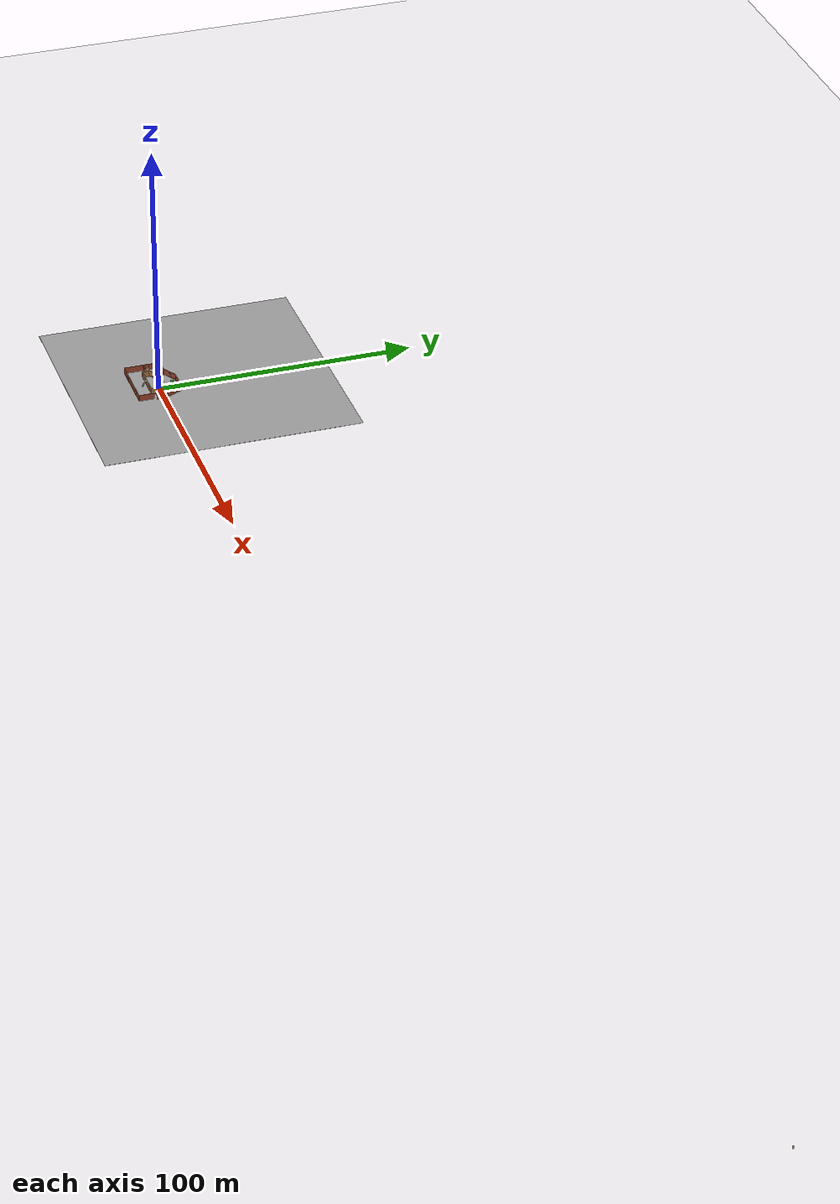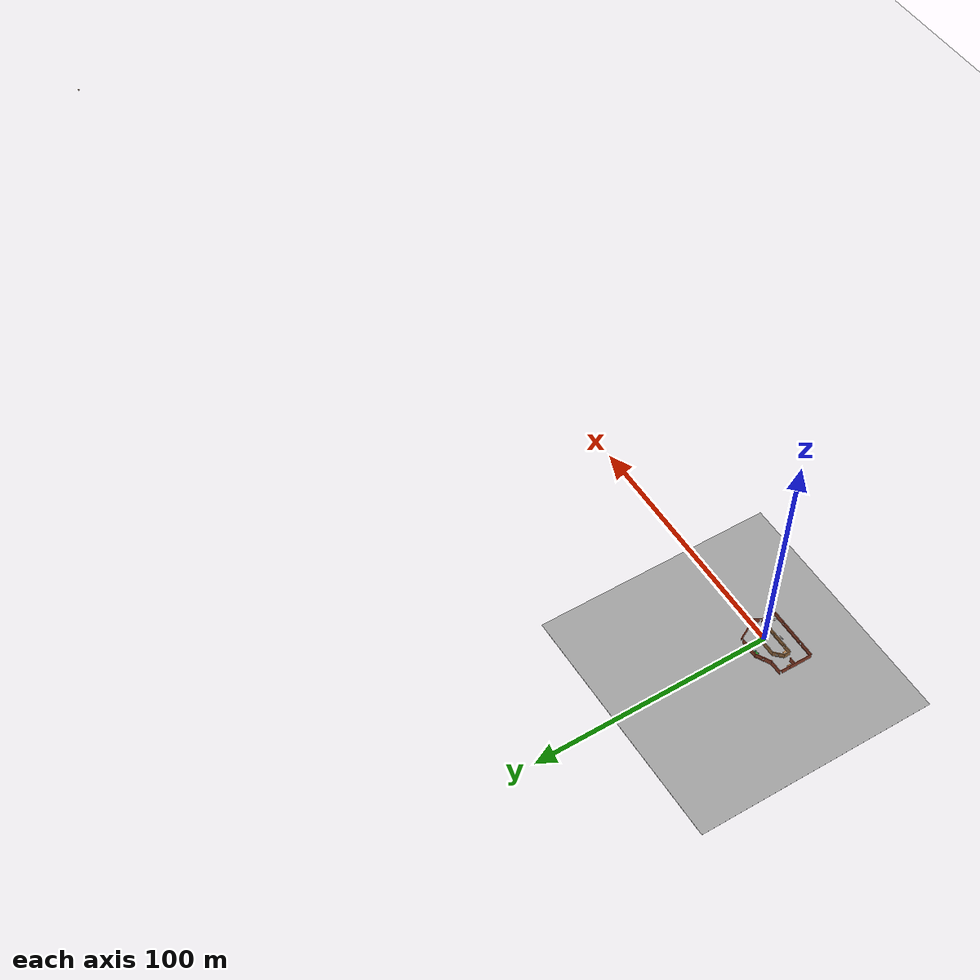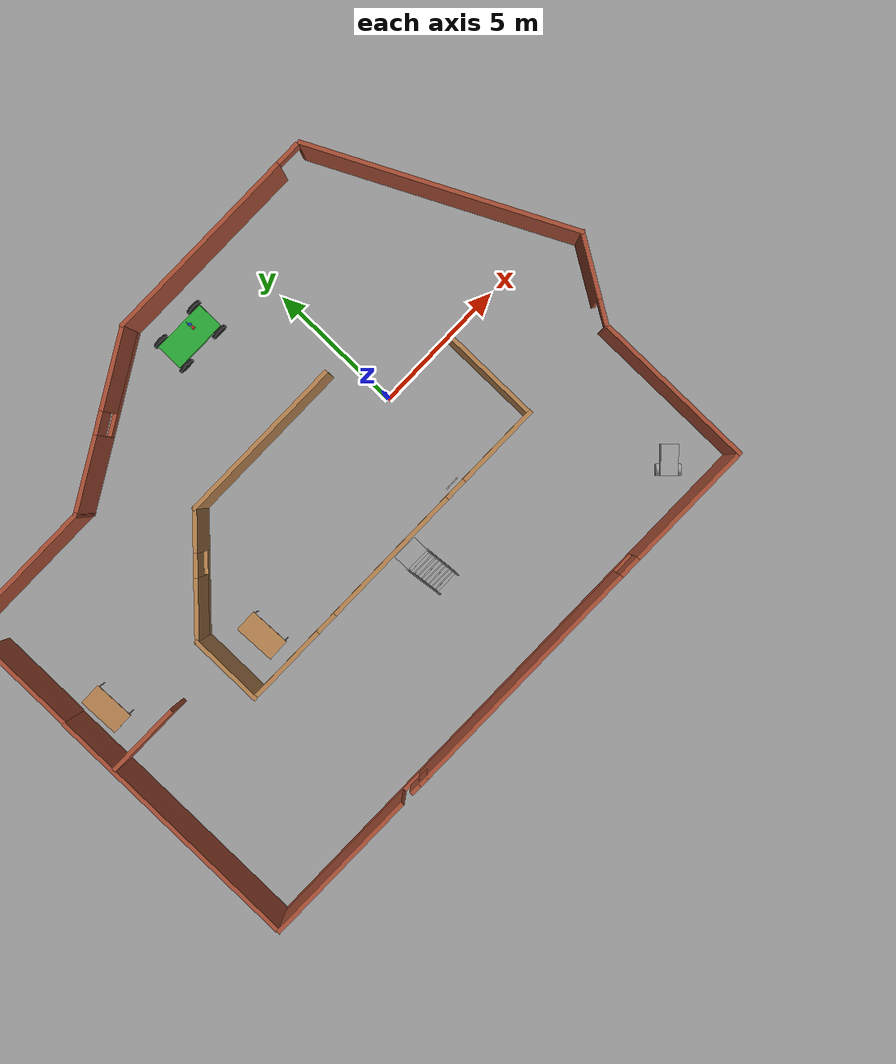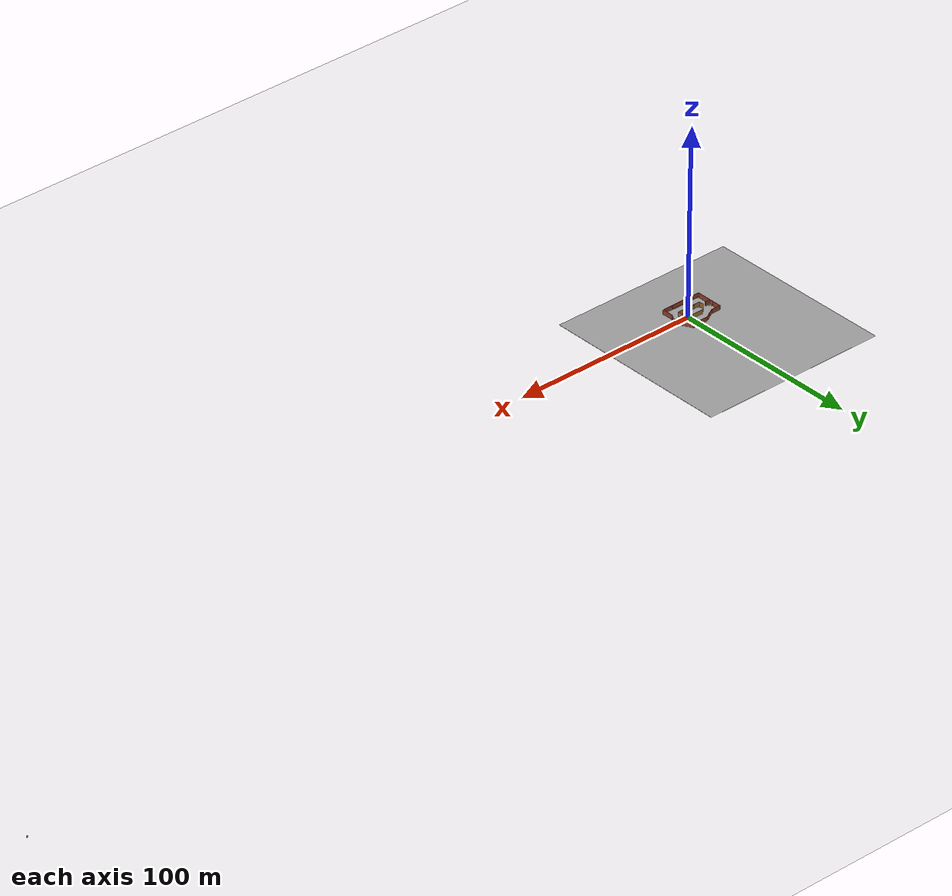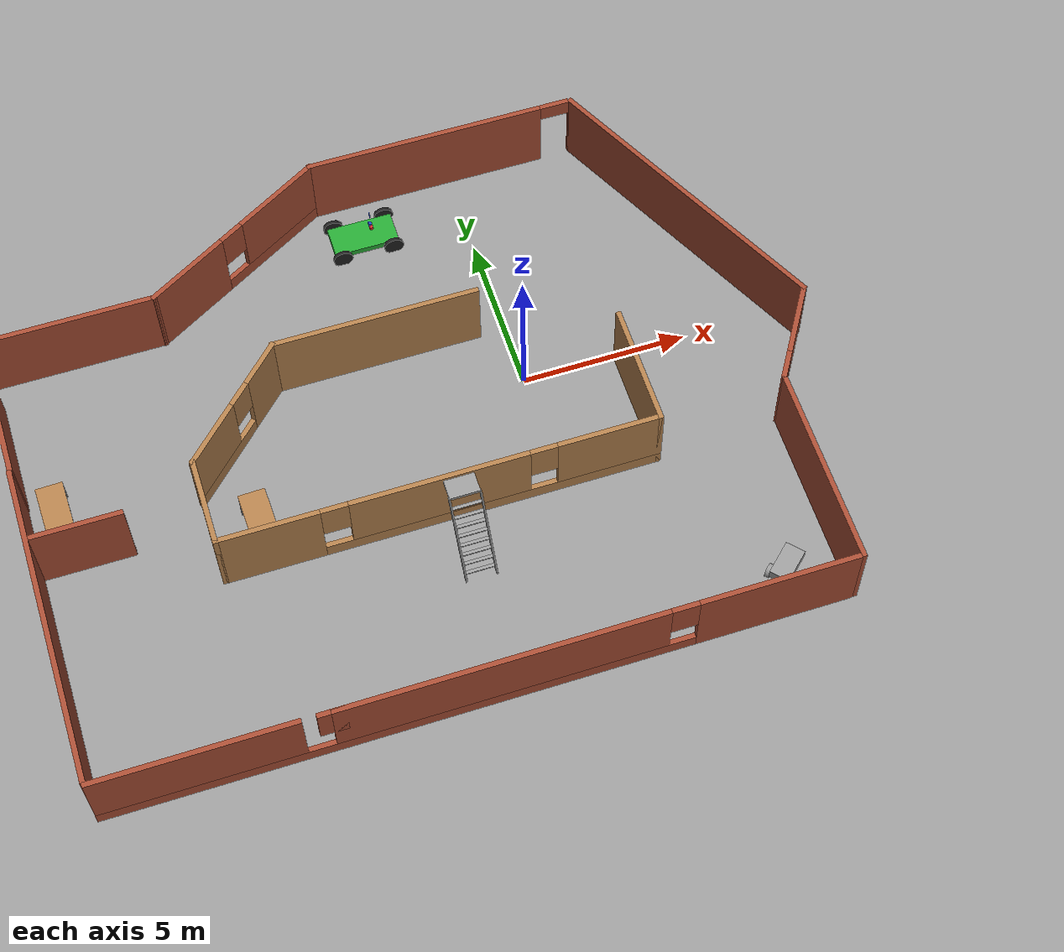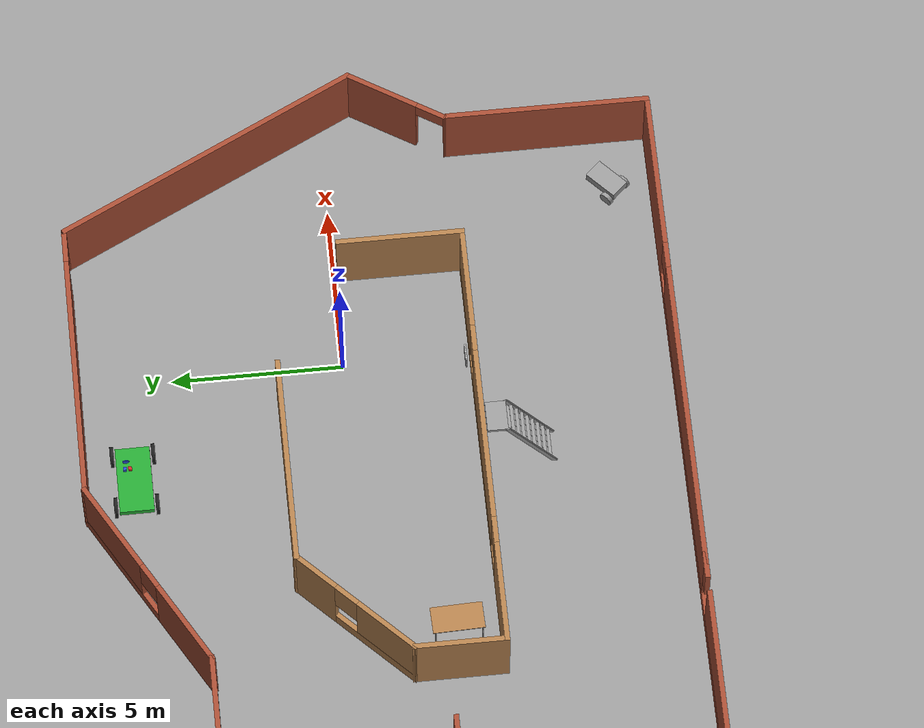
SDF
<sdf version="1.6">
 <world name="default">
  <plugin name="welcome" filename="libwelcome.so"/>
  <light name="sun" type="directional">
   <pose>0 0 10 0 -0 0</pose>
   <diffuse>0.8 0.8 0.8 1</diffuse>
   <specular>0.2 0.2 0.2 1</specular>
   <attenuation>
    <range>1000</range>
    <constant>0.9</constant>
    <linear>0.01</linear>
    <quadratic>0.001</quadratic>
   </attenuation>
   <direction>-0.5 0.1 -0.9</direction>
  </light>
  <model name="ground_plane">
   <static>1</static>
   <link name="link">
    <collision name="collision">
     <geometry><plane><normal>0 0 1</normal><size>100 100</size></plane></geometry>
     <surface>
      <contact><collide_bitmask>65535</collide_bitmask></contact>
      <friction><ode><mu>100</mu><mu2>50</mu2></ode></friction>
     </surface>
    </collision>
    <visual name="visual">
     <cast_shadows>0</cast_shadows>
     <geometry><plane><normal>0 0 1</normal><size>100 100</size></plane></geometry>
     <material>
      <script><uri>file://media/materials/scripts/gazebo.material</uri><name>Gazebo/Grey</name></script>
     </material>
    </visual>
   </link>
  </model>
  <gravity>0 0 -9.8</gravity>
  <magnetic_field>6e-06 2.3e-05 -4.2e-05</magnetic_field>
  <atmosphere type="adiabatic"/>
  <physics name="default_physics" default="0" type="ode">
   <max_step_size>0.001</max_step_size>
   <real_time_factor>1</real_time_factor>
   <real_time_update_rate>1000</real_time_update_rate>
  </physics>
  <scene><ambient>0.4 0.4 0.4 1</ambient><background>0.7 0.7 0.7 1</background><shadows>1</shadows></scene>
  <spherical_coordinates>
   <surface_model>EARTH_WGS84</surface_model>
   <latitude_deg>0</latitude_deg>
   <longitude_deg>0</longitude_deg>
   <elevation>0</elevation>
   <heading_deg>0</heading_deg>
  </spherical_coordinates>
  <model name="cart">
   <link name="link_0">
    <pose>0.000334 -0.065586 0.044669 0 -0 0</pose>
    <inertial>
     <mass>0.183478</mass>
     <inertia>
      <ixx>0.0186131</ixx>
      <ixy>0</ixy>
      <ixz>0</ixz>
      <iyy>0.00678768</iyy>
      <iyz>0</iyz>
      <izz>0.0228966</izz>
     </inertia>
    </inertial>
    <visual name="visual">
     <pose>0 0 0.2 0 -0 0</pose>
     <geometry><box><size>0.6017 1.06558 0.286166</size></box></geometry>
     <material>
      <lighting>1</lighting>
      <script><uri>file://media/materials/scripts/gazebo.material</uri><name>Gazebo/Grey</name></script>
      <shader type="pixel"><normal_map>__default__</normal_map></shader>
      <ambient>0.3 0.3 0.3 1</ambient>
      <diffuse>0.7 0.7 0.7 1</diffuse>
      <specular>0.01 0.01 0.01 1</specular>
      <emissive>0 0 0 1</emissive>
     </material>
    </visual>
    <collision name="collision">
     <pose>0 0 0.2 0 -0 0</pose>
     <geometry><box><size>0.6017 1.06558 0.286166</size></box></geometry>
     <surface>
      <friction>
       <ode><mu>1</mu><mu2>1</mu2><fdir1>0 0 0</fdir1><slip1>0</slip1><slip2>0</slip2></ode>
       <torsional>
        <coefficient>1</coefficient>
        <patch_radius>0</patch_radius>
        <surface_radius>0</surface_radius>
        <use_patch_radius>1</use_patch_radius>
        <ode><slip>0</slip></ode>
       </torsional>
      </friction>
      <bounce><restitution_coefficient>0</restitution_coefficient><threshold>1e+06</threshold></bounce>
      <contact>
       <collide_without_contact>0</collide_without_contact>
       <collide_without_contact_bitmask>1</collide_without_contact_bitmask>
       <collide_bitmask>1</collide_bitmask>
       <ode>
        <soft_cfm>0</soft_cfm>
        <soft_erp>0.2</soft_erp>
        <kp>1e+13</kp>
        <kd>1</kd>
        <max_vel>0.01</max_vel>
        <min_depth>0</min_depth>
       </ode>
       <bullet>
        <split_impulse>1</split_impulse>
        <split_impulse_penetration_threshold>-0.01</split_impulse_penetration_threshold>
        <soft_cfm>0</soft_cfm>
        <soft_erp>0.2</soft_erp>
        <kp>1e+13</kp>
        <kd>1</kd>
       </bullet>
      </contact>
     </surface>
    </collision>
   </link>
   <link name="link_1">
    <pose>-0.001 -0.462788 -0.129729 0 -0 0</pose>
    <inertial>
     <mass>1.886</mass>
     <inertia>
      <ixx>0.0115145</ixx>
      <ixy>0</ixy>
      <ixz>0</ixz>
      <iyy>0.0115145</iyy>
      <iyz>0</iyz>
      <izz>0.0115145</izz>
     </inertia>
     <pose>0 0 0.024704 0 -0 0</pose>
    </inertial>
    <visual name="visual">
     <pose>0 0 0.1 0 -0 0</pose>
     <geometry><sphere><radius>0.123544</radius></sphere></geometry>
     <material>
      <lighting>1</lighting>
      <script><uri>file://media/materials/scripts/gazebo.material</uri><name>Gazebo/Grey</name></script>
      <shader type="pixel"><normal_map>__default__</normal_map></shader>
      <ambient>0.3 0.3 0.3 1</ambient>
      <diffuse>0.7 0.7 0.7 1</diffuse>
      <specular>0.01 0.01 0.01 1</specular>
      <emissive>0 0 0 1</emissive>
     </material>
    </visual>
    <collision name="collision">
     <pose>0 0 0.1 0 -0 0</pose>
     <geometry><sphere><radius>0.123544</radius></sphere></geometry>
     <surface>
      <friction>
       <ode><mu>1</mu><mu2>1</mu2><fdir1>0 0 0</fdir1><slip1>0</slip1><slip2>0</slip2></ode>
       <torsional>
        <coefficient>1</coefficient>
        <patch_radius>0</patch_radius>
        <surface_radius>0</surface_radius>
        <use_patch_radius>1</use_patch_radius>
        <ode><slip>0</slip></ode>
       </torsional>
      </friction>
      <bounce><restitution_coefficient>0</restitution_coefficient><threshold>1e+06</threshold></bounce>
      <contact>
       <collide_without_contact>0</collide_without_contact>
       <collide_without_contact_bitmask>1</collide_without_contact_bitmask>
       <collide_bitmask>1</collide_bitmask>
       <ode>
        <soft_cfm>0</soft_cfm>
        <soft_erp>0.2</soft_erp>
        <kp>1e+13</kp>
        <kd>1</kd>
        <max_vel>0.01</max_vel>
        <min_depth>0</min_depth>
       </ode>
       <bullet>
        <split_impulse>1</split_impulse>
        <split_impulse_penetration_threshold>-0.01</split_impulse_penetration_threshold>
        <soft_cfm>0</soft_cfm>
        <soft_erp>0.2</soft_erp>
        <kp>1e+13</kp>
        <kd>1</kd>
       </bullet>
      </contact>
     </surface>
    </collision>
   </link>
   <link name="link_2">
    <pose>0.368986 0.26419 0.04253 3.14159 1.55999 3.14159</pose>
    <inertial>
     <mass>0.0216399</mass>
     <inertia>
      <ixx>0.000254029</ixx>
      <ixy>0</ixy>
      <ixz>0</ixz>
      <iyy>0.000254029</iyy>
      <iyz>0</iyz>
      <izz>0.000445951</izz>
     </inertia>
    </inertial>
    <visual name="visual">
     <geometry><cylinder><radius>0.203016</radius><length>0.131225</length></cylinder></geometry>
     <material>
      <lighting>1</lighting>
      <script><uri>file://media/materials/scripts/gazebo.material</uri><name>Gazebo/Grey</name></script>
      <shader type="pixel"><normal_map>__default__</normal_map></shader>
      <ambient>0.3 0.3 0.3 1</ambient>
      <diffuse>0.7 0.7 0.7 1</diffuse>
      <specular>0.01 0.01 0.01 1</specular>
      <emissive>0 0 0 1</emissive>
     </material>
    </visual>
    <collision name="collision">
     <geometry><cylinder><radius>0.203016</radius><length>0.131225</length></cylinder></geometry>
     <surface>
      <friction>
       <ode><mu>1</mu><mu2>1</mu2><fdir1>0 0 0</fdir1><slip1>0</slip1><slip2>0</slip2></ode>
       <torsional>
        <coefficient>1</coefficient>
        <patch_radius>0</patch_radius>
        <surface_radius>0</surface_radius>
        <use_patch_radius>1</use_patch_radius>
        <ode><slip>0</slip></ode>
       </torsional>
      </friction>
      <bounce><restitution_coefficient>0</restitution_coefficient><threshold>1e+06</threshold></bounce>
      <contact>
       <collide_without_contact>0</collide_without_contact>
       <collide_without_contact_bitmask>1</collide_without_contact_bitmask>
       <collide_bitmask>1</collide_bitmask>
       <ode>
        <soft_cfm>0</soft_cfm>
        <soft_erp>0.2</soft_erp>
        <kp>1e+13</kp>
        <kd>1</kd>
        <max_vel>0.01</max_vel>
        <min_depth>0</min_depth>
       </ode>
       <bullet>
        <split_impulse>1</split_impulse>
        <split_impulse_penetration_threshold>-0.01</split_impulse_penetration_threshold>
        <soft_cfm>0</soft_cfm>
        <soft_erp>0.2</soft_erp>
        <kp>1e+13</kp>
        <kd>1</kd>
       </bullet>
      </contact>
     </surface>
    </collision>
   </link>
   <link name="link_2_clone">
    <pose>-0.368319 0.26419 0.04253 3.14159 1.55999 3.14159</pose>
    <inertial>
     <mass>0.0216399</mass>
     <inertia>
      <ixx>0.000254029</ixx>
      <ixy>0</ixy>
      <ixz>0</ixz>
      <iyy>0.000254029</iyy>
      <iyz>0</iyz>
      <izz>0.000445951</izz>
     </inertia>
    </inertial>
    <visual name="visual">
     <geometry><cylinder><radius>0.203016</radius><length>0.131225</length></cylinder></geometry>
     <material>
      <lighting>1</lighting>
      <script><uri>file://media/materials/scripts/gazebo.material</uri><name>Gazebo/Grey</name></script>
      <shader type="pixel"><normal_map>__default__</normal_map></shader>
      <ambient>0.3 0.3 0.3 1</ambient>
      <diffuse>0.7 0.7 0.7 1</diffuse>
      <specular>0.01 0.01 0.01 1</specular>
      <emissive>0 0 0 1</emissive>
     </material>
    </visual>
    <collision name="collision">
     <geometry><cylinder><radius>0.203016</radius><length>0.131225</length></cylinder></geometry>
     <surface>
      <friction>
       <ode><mu>1</mu><mu2>1</mu2><fdir1>0 0 0</fdir1><slip1>0</slip1><slip2>0</slip2></ode>
       <torsional>
        <coefficient>1</coefficient>
        <patch_radius>0</patch_radius>
        <surface_radius>0</surface_radius>
        <use_patch_radius>1</use_patch_radius>
        <ode><slip>0</slip></ode>
       </torsional>
      </friction>
      <bounce><restitution_coefficient>0</restitution_coefficient><threshold>1e+06</threshold></bounce>
      <contact>
       <collide_without_contact>0</collide_without_contact>
       <collide_without_contact_bitmask>1</collide_without_contact_bitmask>
       <collide_bitmask>1</collide_bitmask>
       <ode>
        <soft_cfm>0</soft_cfm>
        <soft_erp>0.2</soft_erp>
        <kp>1e+13</kp>
        <kd>1</kd>
        <max_vel>0.01</max_vel>
        <min_depth>0</min_depth>
       </ode>
       <bullet>
        <split_impulse>1</split_impulse>
        <split_impulse_penetration_threshold>-0.01</split_impulse_penetration_threshold>
        <soft_cfm>0</soft_cfm>
        <soft_erp>0.2</soft_erp>
        <kp>1e+13</kp>
        <kd>1</kd>
       </bullet>
      </contact>
     </surface>
    </collision>
   </link>
   <joint name="link_0_JOINT_0" type="revolute">
    <parent>link_0</parent>
    <child>link_2</child>
    <axis>
     <xyz>0 0 1</xyz>
     <use_parent_model_frame>0</use_parent_model_frame>
     <limit>
      <lower>-1.79769e+308</lower>
      <upper>1.79769e+308</upper>
      <effort>-1</effort>
      <velocity>-1</velocity>
     </limit>
     <dynamics>
      <spring_reference>0</spring_reference>
      <spring_stiffness>0</spring_stiffness>
      <damping>0</damping>
     </dynamics>
    </axis>
    <physics>
     <ode><limit><cfm>0</cfm><erp>0.2</erp></limit><suspension><cfm>0</cfm><erp>0.2</erp></suspension></ode>
    </physics>
   </joint>
   <joint name="link_0_JOINT_1" type="revolute">
    <parent>link_0</parent>
    <child>link_2_clone</child>
    <axis>
     <xyz>0 0 1</xyz>
     <use_parent_model_frame>0</use_parent_model_frame>
     <limit>
      <lower>-1.79769e+308</lower>
      <upper>1.79769e+308</upper>
      <effort>-1</effort>
      <velocity>-1</velocity>
     </limit>
     <dynamics>
      <spring_reference>0</spring_reference>
      <spring_stiffness>0</spring_stiffness>
      <damping>0</damping>
     </dynamics>
    </axis>
    <physics>
     <ode><limit><cfm>0</cfm><erp>0.2</erp></limit><suspension><cfm>0</cfm><erp>0.2</erp></suspension></ode>
    </physics>
   </joint>
   <joint name="link_0_JOINT_2" type="ball">
    <parent>link_0</parent>
    <child>link_1</child>
    <physics>
     <ode><limit><cfm>0</cfm><erp>0.2</erp></limit><suspension><cfm>0</cfm><erp>0.2</erp></suspension></ode>
    </physics>
   </joint>
   <static>0</static>
   <pose>5.05319 -8.31744 0.158308 0.010889 -1e-06 2.32186</pose>
  </model>
  <model name="cabinet">
   <static>1</static>
   <link name="cabinet_bottom_plate">
    <inertial>
     <pose>0 0 -1 0 -0 0</pose>
     <inertia><ixx>2.05</ixx><ixy>0</ixy><ixz>0</ixz><iyy>2.05</iyy><iyz>0</iyz><izz>2.05</izz></inertia>
     <mass>25</mass>
    </inertial>
    <collision name="cabinet_bottom_plate_geom">
     <pose>0 0 0.01 0 -0 0</pose>
     <geometry><box><size>0.45 0.45 0.02</size></box></geometry>
    </collision>
    <visual name="cabinet_bottom_plate_geom_visual">
     <pose>0 0 0.01 0 -0 0</pose>
     <geometry><box><size>0.45 0.45 0.02</size></box></geometry>
     <material>
      <script><uri>file://media/materials/scripts/gazebo.material</uri><name>Gazebo/Wood</name></script>
     </material>
    </visual>
    <collision name="cabinet_bottom_plate_geom_cabinet_back_plate">
     <pose>0.235 0 0.51 0 -0 0</pose>
     <geometry><box><size>0.02 0.45 1.02</size></box></geometry>
    </collision>
    <visual name="cabinet_bottom_plate_geom_cabinet_back_plate_visual">
     <pose>0.235 0 0.51 0 -0 0</pose>
     <geometry><box><size>0.02 0.45 1.02</size></box></geometry>
     <material>
      <script><uri>file://media/materials/scripts/gazebo.material</uri><name>Gazebo/Wood</name></script>
     </material>
    </visual>
    <collision name="cabinet_bottom_plate_geom_cabinet_left_plate">
     <pose>0 0.235 0.51 0 -0 0</pose>
     <geometry><box><size>0.45 0.02 1.02</size></box></geometry>
    </collision>
    <visual name="cabinet_bottom_plate_geom_cabinet_left_plate_visual">
     <pose>0 0.235 0.51 0 -0 0</pose>
     <geometry><box><size>0.45 0.02 1.02</size></box></geometry>
     <material>
      <script><uri>file://media/materials/scripts/gazebo.material</uri><name>Gazebo/Wood</name></script>
     </material>
    </visual>
    <collision name="cabinet_bottom_plate_geom_cabinet_middle_plate">
     <pose>0 0 0.51 0 -0 0</pose>
     <geometry><box><size>0.45 0.45 0.02</size></box></geometry>
    </collision>
    <visual name="cabinet_bottom_plate_geom_cabinet_middle_plate_visual">
     <pose>0 0 0.51 0 -0 0</pose>
     <geometry><box><size>0.45 0.45 0.02</size></box></geometry>
     <material>
      <script><uri>file://media/materials/scripts/gazebo.material</uri><name>Gazebo/Wood</name></script>
     </material>
    </visual>
    <collision name="cabinet_bottom_plate_geom_cabinet_right_plate">
     <pose>0 -0.235 0.51 0 -0 0</pose>
     <geometry><box><size>0.45 0.02 1.02</size></box></geometry>
    </collision>
    <visual name="cabinet_bottom_plate_geom_cabinet_right_plate_visual">
     <pose>0 -0.235 0.51 0 -0 0</pose>
     <geometry><box><size>0.45 0.02 1.02</size></box></geometry>
     <material>
      <script><uri>file://media/materials/scripts/gazebo.material</uri><name>Gazebo/Wood</name></script>
     </material>
    </visual>
    <collision name="cabinet_bottom_plate_geom_cabinet_top_plate">
     <pose>0 0 1.01 0 -0 0</pose>
     <geometry><box><size>0.45 0.45 0.02</size></box></geometry>
    </collision>
    <visual name="cabinet_bottom_plate_geom_cabinet_top_plate_visual">
     <pose>0 0 1.01 0 -0 0</pose>
     <geometry><box><size>0.45 0.45 0.02</size></box></geometry>
     <material>
      <script><uri>file://media/materials/scripts/gazebo.material</uri><name>Gazebo/Wood</name></script>
     </material>
    </visual>
   </link>
   <pose>440.801 76.4548 -31.3681 0 -0 0</pose>
  </model>
  <model name="car">
   <link name="chassis">
    <pose>0 0 0.3 0 -0 0</pose>
    <collision name="collision"><geometry><box><size>2 1 0.2</size></box></geometry></collision>
    <visual name="visual">
     <geometry><box><size>2 1 0.2</size></box></geometry>
     <material>
      <script><uri>file://media/materials/scripts/gazebo.material</uri><name>Gazebo/Green</name></script>
     </material>
    </visual>
    <inertial>
     <inertia><ixx>1</ixx><ixy>0</ixy><ixz>0</ixz><iyy>1</iyy><iyz>0</iyz><izz>1</izz></inertia>
     <mass>1</mass>
    </inertial>
   </link>
   <link name="front_left_wheel">
    <pose>0.8 0.6 0.3 -0 1.5707 1.5707</pose>
    <collision name="collision">
     <geometry><cylinder><radius>0.3</radius><length>0.1</length></cylinder></geometry>
    </collision>
    <visual name="visual">
     <geometry><cylinder><radius>0.3</radius><length>0.1</length></cylinder></geometry>
     <material>
      <script><uri>file://media/materials/scripts/gazebo.material</uri><name>Gazebo/Black</name></script>
     </material>
    </visual>
    <inertial>
     <inertia><ixx>1</ixx><ixy>0</ixy><ixz>0</ixz><iyy>1</iyy><iyz>0</iyz><izz>1</izz></inertia>
     <mass>1</mass>
    </inertial>
   </link>
   <link name="front_right_wheel">
    <pose>0.8 -0.6 0.3 -0 1.5707 1.5707</pose>
    <collision name="collision">
     <geometry><cylinder><radius>0.3</radius><length>0.1</length></cylinder></geometry>
    </collision>
    <visual name="visual">
     <geometry><cylinder><radius>0.3</radius><length>0.1</length></cylinder></geometry>
     <material>
      <script><uri>file://media/materials/scripts/gazebo.material</uri><name>Gazebo/Black</name></script>
     </material>
    </visual>
    <inertial>
     <inertia><ixx>1</ixx><ixy>0</ixy><ixz>0</ixz><iyy>1</iyy><iyz>0</iyz><izz>1</izz></inertia>
     <mass>1</mass>
    </inertial>
   </link>
   <link name="back_right_wheel">
    <pose>-0.8 -0.6 0.3 -0 1.5707 1.5707</pose>
    <collision name="collision">
     <geometry><cylinder><radius>0.3</radius><length>0.1</length></cylinder></geometry>
    </collision>
    <visual name="visual">
     <geometry><cylinder><radius>0.3</radius><length>0.1</length></cylinder></geometry>
     <material>
      <script><uri>file://media/materials/scripts/gazebo.material</uri><name>Gazebo/Black</name></script>
     </material>
    </visual>
    <inertial>
     <inertia><ixx>1</ixx><ixy>0</ixy><ixz>0</ixz><iyy>1</iyy><iyz>0</iyz><izz>1</izz></inertia>
     <mass>1</mass>
    </inertial>
   </link>
   <link name="back_left_wheel">
    <pose>-0.8 0.6 0.3 -0 1.5707 1.5707</pose>
    <collision name="collision">
     <geometry><cylinder><radius>0.3</radius><length>0.1</length></cylinder></geometry>
    </collision>
    <visual name="visual">
     <geometry><cylinder><radius>0.3</radius><length>0.1</length></cylinder></geometry>
     <material>
      <script><uri>file://media/materials/scripts/gazebo.material</uri><name>Gazebo/Black</name></script>
     </material>
    </visual>
    <inertial>
     <inertia><ixx>1</ixx><ixy>0</ixy><ixz>0</ixz><iyy>1</iyy><iyz>0</iyz><izz>1</izz></inertia>
     <mass>1</mass>
    </inertial>
   </link>
   <link name="gas_pedal">
    <pose>0.3 0.1 0.5 0 -0 0</pose>
    <collision name="collision"><geometry><box><size>0.1 0.1 0.1</size></box></geometry></collision>
    <visual name="visual">
     <geometry><box><size>0.1 0.1 0.1</size></box></geometry>
     <material>
      <script><uri>file://media/materials/scripts/gazebo.material</uri><name>Gazebo/Red</name></script>
     </material>
    </visual>
    <inertial>
     <inertia><ixx>1</ixx><ixy>0</ixy><ixz>0</ixz><iyy>1</iyy><iyz>0</iyz><izz>1</izz></inertia>
     <mass>1</mass>
    </inertial>
   </link>
   <link name="brake_pedal">
    <pose>0.3 0.25 0.5 0 -0 0</pose>
    <collision name="collision"><geometry><box><size>0.1 0.1 0.1</size></box></geometry></collision>
    <visual name="visual">
     <geometry><box><size>0.1 0.1 0.1</size></box></geometry>
     <material>
      <script><uri>file://media/materials/scripts/gazebo.material</uri><name>Gazebo/Blue</name></script>
     </material>
    </visual>
    <inertial>
     <inertia><ixx>1</ixx><ixy>0</ixy><ixz>0</ixz><iyy>1</iyy><iyz>0</iyz><izz>1</izz></inertia>
     <mass>1</mass>
    </inertial>
   </link>
   <link name="steering_wheel">
    <pose>0.3 0.2 1 0 1.5707 0</pose>
    <collision name="collision">
     <geometry><cylinder><radius>0.1</radius><length>0.01</length></cylinder></geometry>
    </collision>
    <visual name="visual">
     <geometry><cylinder><radius>0.1</radius><length>0.01</length></cylinder></geometry>
     <material>
      <script><uri>file://media/materials/scripts/gazebo.material</uri><name>Gazebo/Blue</name></script>
     </material>
    </visual>
    <inertial>
     <inertia><ixx>1</ixx><ixy>0</ixy><ixz>0</ixz><iyy>1</iyy><iyz>0</iyz><izz>1</izz></inertia>
     <mass>1</mass>
    </inertial>
   </link>
   <joint name="gas_joint" type="prismatic">
    <parent>chassis</parent>
    <child>gas_pedal</child>
    <axis>
     <xyz>1 0 0</xyz>
     <limit><lower>0</lower><upper>0.2</upper></limit>
     <use_parent_model_frame>1</use_parent_model_frame>
     <dynamics><spring_reference>0</spring_reference><spring_stiffness>0</spring_stiffness></dynamics>
    </axis>
   </joint>
   <joint name="brake_joint" type="prismatic">
    <parent>chassis</parent>
    <child>brake_pedal</child>
    <axis>
     <xyz>1 0 0</xyz>
     <limit><lower>0</lower><upper>0.2</upper></limit>
     <use_parent_model_frame>1</use_parent_model_frame>
     <dynamics><spring_reference>0</spring_reference><spring_stiffness>0</spring_stiffness></dynamics>
    </axis>
   </joint>
   <joint name="steering_joint" type="revolute">
    <parent>chassis</parent>
    <child>steering_wheel</child>
    <axis>
     <xyz>1 0 0</xyz>
     <limit><lower>-7.853</lower><upper>7.853</upper></limit>
     <use_parent_model_frame>1</use_parent_model_frame>
     <dynamics><spring_reference>0</spring_reference><spring_stiffness>0</spring_stiffness></dynamics>
    </axis>
   </joint>
   <joint name="front_left_joint" type="revolute2">
    <parent>chassis</parent>
    <child>front_left_wheel</child>
    <axis>
     <xyz>0 0 1</xyz>
     <limit><lower>6.95329e-06</lower><upper>6.95329e-06</upper></limit>
     <use_parent_model_frame>1</use_parent_model_frame>
     <dynamics><spring_reference>0</spring_reference><spring_stiffness>0</spring_stiffness></dynamics>
    </axis>
    <axis2>
     <xyz>0 1 0</xyz>
     <use_parent_model_frame>1</use_parent_model_frame>
     <dynamics><spring_reference>0</spring_reference><spring_stiffness>0</spring_stiffness></dynamics>
    </axis2>
    <physics><ode><limit><cfm>0</cfm><erp>0.9</erp></limit></ode></physics>
   </joint>
   <joint name="front_right_joint" type="revolute2">
    <parent>chassis</parent>
    <child>front_right_wheel</child>
    <axis>
     <xyz>0 0 1</xyz>
     <limit><lower>6.95329e-06</lower><upper>6.95329e-06</upper></limit>
     <use_parent_model_frame>1</use_parent_model_frame>
     <dynamics><spring_reference>0</spring_reference><spring_stiffness>0</spring_stiffness></dynamics>
    </axis>
    <axis2>
     <xyz>0 1 0</xyz>
     <use_parent_model_frame>1</use_parent_model_frame>
     <dynamics><spring_reference>0</spring_reference><spring_stiffness>0</spring_stiffness></dynamics>
    </axis2>
    <physics><ode><limit><cfm>0</cfm><erp>0.9</erp></limit></ode></physics>
   </joint>
   <joint name="back_right_joint" type="revolute2">
    <parent>chassis</parent>
    <child>back_right_wheel</child>
    <axis>
     <xyz>0 0 1</xyz>
     <limit><lower>0</lower><upper>0</upper></limit>
     <use_parent_model_frame>1</use_parent_model_frame>
     <dynamics><spring_reference>0</spring_reference><spring_stiffness>0</spring_stiffness></dynamics>
    </axis>
    <axis2>
     <xyz>0 1 0</xyz>
     <use_parent_model_frame>1</use_parent_model_frame>
     <dynamics><spring_reference>0</spring_reference><spring_stiffness>0</spring_stiffness></dynamics>
    </axis2>
    <physics><ode><limit><cfm>0</cfm><erp>0.9</erp></limit></ode></physics>
   </joint>
   <joint name="back_left_joint" type="revolute2">
    <parent>chassis</parent>
    <child>back_left_wheel</child>
    <axis>
     <xyz>0 0 1</xyz>
     <limit><lower>0</lower><upper>0</upper></limit>
     <use_parent_model_frame>1</use_parent_model_frame>
     <dynamics><spring_reference>0</spring_reference><spring_stiffness>0</spring_stiffness></dynamics>
    </axis>
    <axis2>
     <xyz>0 1 0</xyz>
     <use_parent_model_frame>1</use_parent_model_frame>
     <dynamics><spring_reference>0</spring_reference><spring_stiffness>0</spring_stiffness></dynamics>
    </axis2>
    <physics><ode><limit><cfm>0</cfm><erp>0.9</erp></limit></ode></physics>
   </joint>
   <plugin name="vehicle" filename="libVehiclePlugin.so">
    <front_left>front_left_joint</front_left>
    <front_right>front_right_joint</front_right>
    <back_left>back_left_joint</back_left>
    <back_right>back_right_joint</back_right>
    <gas>gas_joint</gas>
    <brake>brake_joint</brake>
    <steering>steering_joint</steering>
    <front_power>10</front_power>
    <rear_power>10</rear_power>
    <tire_angle_range>0.5</tire_angle_range>
    <max_speed>10</max_speed>
    <aero_load>0.1</aero_load>
   </plugin>
   <pose>-3.14883 6.29955 -0.002614 -0.000274 0.000925 0.000534</pose>
  </model>
  <model name="office">
   <link name="Wall_10">
    <pose>3.71196 8.6392 0 0 -0 0</pose>
    <visual name="Wall_10_Visual_1">
     <pose>4.12333 0 1.25 0 -0 0</pose>
     <geometry><box><size>0.003332 0.15 2.5</size></box></geometry>
     <material>
      <script><uri>file://media/materials/scripts/gazebo.material</uri><name>Gazebo/Bricks</name></script>
      <ambient>1 1 1 1</ambient>
      <shader type="pixel"/>
      <diffuse>1 1 1 1</diffuse>
      <specular>0.2 0.2 0.2 1</specular>
      <emissive>0 0 0 1</emissive>
     </material>
     <meta><layer>0</layer></meta>
    </visual>
    <visual name="Wall_10_Visual_0">
     <pose>-0.451666 0 1.25 0 -0 0</pose>
     <geometry><box><size>7.34667 0.15 2.5</size></box></geometry>
     <material>
      <script><uri>file://media/materials/scripts/gazebo.material</uri><name>Gazebo/Bricks</name></script>
      <ambient>1 1 1 1</ambient>
      <shader type="pixel"/>
      <diffuse>1 1 1 1</diffuse>
      <specular>0.2 0.2 0.2 1</specular>
      <emissive>0 0 0 1</emissive>
     </material>
     <meta><layer>0</layer></meta>
    </visual>
    <visual name="Wall_10_Visual_2">
     <pose>3.67167 0 2.25 0 -0 0</pose>
     <geometry><box><size>0.9 0.15 0.5</size></box></geometry>
     <material>
      <script><uri>file://media/materials/scripts/gazebo.material</uri><name>Gazebo/Bricks</name></script>
      <ambient>1 1 1 1</ambient>
      <shader type="pixel"/>
      <diffuse>1 1 1 1</diffuse>
      <specular>0.2 0.2 0.2 1</specular>
      <emissive>0 0 0 1</emissive>
     </material>
     <meta><layer>0</layer></meta>
    </visual>
    <collision name="Wall_10_Collision_0">
     <pose>-0.451666 0 1.25 0 -0 0</pose>
     <geometry><box><size>7.34667 0.15 2.5</size></box></geometry>
     <surface>
      <friction>
       <ode><mu>1</mu><mu2>1</mu2><fdir1>0 0 0</fdir1><slip1>0</slip1><slip2>0</slip2></ode>
       <torsional>
        <coefficient>1</coefficient>
        <patch_radius>0</patch_radius>
        <surface_radius>0</surface_radius>
        <use_patch_radius>1</use_patch_radius>
        <ode><slip>0</slip></ode>
       </torsional>
      </friction>
      <bounce><restitution_coefficient>0</restitution_coefficient><threshold>1e+06</threshold></bounce>
      <contact>
       <collide_without_contact>0</collide_without_contact>
       <collide_without_contact_bitmask>1</collide_without_contact_bitmask>
       <collide_bitmask>1</collide_bitmask>
       <ode>
        <soft_cfm>0</soft_cfm>
        <soft_erp>0.2</soft_erp>
        <kp>1e+13</kp>
        <kd>1</kd>
        <max_vel>0.01</max_vel>
        <min_depth>0</min_depth>
       </ode>
       <bullet>
        <split_impulse>1</split_impulse>
        <split_impulse_penetration_threshold>-0.01</split_impulse_penetration_threshold>
        <soft_cfm>0</soft_cfm>
        <soft_erp>0.2</soft_erp>
        <kp>1e+13</kp>
        <kd>1</kd>
       </bullet>
      </contact>
     </surface>
    </collision>
    <collision name="Wall_10_Collision_2">
     <pose>3.67167 0 2.25 0 -0 0</pose>
     <geometry><box><size>0.9 0.15 0.5</size></box></geometry>
     <surface>
      <friction>
       <ode><mu>1</mu><mu2>1</mu2><fdir1>0 0 0</fdir1><slip1>0</slip1><slip2>0</slip2></ode>
       <torsional>
        <coefficient>1</coefficient>
        <patch_radius>0</patch_radius>
        <surface_radius>0</surface_radius>
        <use_patch_radius>1</use_patch_radius>
        <ode><slip>0</slip></ode>
       </torsional>
      </friction>
      <bounce><restitution_coefficient>0</restitution_coefficient><threshold>1e+06</threshold></bounce>
      <contact>
       <collide_without_contact>0</collide_without_contact>
       <collide_without_contact_bitmask>1</collide_without_contact_bitmask>
       <collide_bitmask>1</collide_bitmask>
       <ode>
        <soft_cfm>0</soft_cfm>
        <soft_erp>0.2</soft_erp>
        <kp>1e+13</kp>
        <kd>1</kd>
        <max_vel>0.01</max_vel>
        <min_depth>0</min_depth>
       </ode>
       <bullet>
        <split_impulse>1</split_impulse>
        <split_impulse_penetration_threshold>-0.01</split_impulse_penetration_threshold>
        <soft_cfm>0</soft_cfm>
        <soft_erp>0.2</soft_erp>
        <kp>1e+13</kp>
        <kd>1</kd>
       </bullet>
      </contact>
     </surface>
    </collision>
    <collision name="Wall_10_Collision_1">
     <pose>4.12333 0 1.25 0 -0 0</pose>
     <geometry><box><size>0.003332 0.15 2.5</size></box></geometry>
     <surface>
      <friction>
       <ode><mu>1</mu><mu2>1</mu2><fdir1>0 0 0</fdir1><slip1>0</slip1><slip2>0</slip2></ode>
       <torsional>
        <coefficient>1</coefficient>
        <patch_radius>0</patch_radius>
        <surface_radius>0</surface_radius>
        <use_patch_radius>1</use_patch_radius>
        <ode><slip>0</slip></ode>
       </torsional>
      </friction>
      <bounce><restitution_coefficient>0</restitution_coefficient><threshold>1e+06</threshold></bounce>
      <contact>
       <collide_without_contact>0</collide_without_contact>
       <collide_without_contact_bitmask>1</collide_without_contact_bitmask>
       <collide_bitmask>1</collide_bitmask>
       <ode>
        <soft_cfm>0</soft_cfm>
        <soft_erp>0.2</soft_erp>
        <kp>1e+13</kp>
        <kd>1</kd>
        <max_vel>0.01</max_vel>
        <min_depth>0</min_depth>
       </ode>
       <bullet>
        <split_impulse>1</split_impulse>
        <split_impulse_penetration_threshold>-0.01</split_impulse_penetration_threshold>
        <soft_cfm>0</soft_cfm>
        <soft_erp>0.2</soft_erp>
        <kp>1e+13</kp>
        <kd>1</kd>
       </bullet>
      </contact>
     </surface>
    </collision>
   </link>
   <link name="Wall_12">
    <pose>10.0538 4.3089 0 0 0 -1.1105</pose>
    <inertial>
     <inertia><ixx>0</ixx><ixy>0</ixy><ixz>0</ixz><iyy>0</iyy><iyz>0</iyz><izz>0</izz></inertia>
     <mass>0</mass>
    </inertial>
    <visual name="Wall_12_Visual">
     <pose>0 0 1.25 0 -0 0</pose>
     <geometry><box><size>9.75381 0.15 2.5</size></box></geometry>
     <material>
      <script><uri>file://media/materials/scripts/gazebo.material</uri><name>Gazebo/Bricks</name></script>
      <ambient>0.435294 0.796078 0.67451 1</ambient>
      <shader type="pixel"/>
      <diffuse>1 1 1 1</diffuse>
      <specular>0.2 0.2 0.2 1</specular>
      <emissive>0 0 0 1</emissive>
     </material>
     <meta><layer>0</layer></meta>
    </visual>
    <collision name="Wall_12_Collision">
     <pose>0 0 1.25 0 -0 0</pose>
     <geometry><box><size>9.75381 0.15 2.5</size></box></geometry>
     <surface>
      <friction>
       <ode><mu>1</mu><mu2>1</mu2><fdir1>0 0 0</fdir1><slip1>0</slip1><slip2>0</slip2></ode>
       <torsional>
        <coefficient>1</coefficient>
        <patch_radius>0</patch_radius>
        <surface_radius>0</surface_radius>
        <use_patch_radius>1</use_patch_radius>
        <ode><slip>0</slip></ode>
       </torsional>
      </friction>
      <bounce><restitution_coefficient>0</restitution_coefficient><threshold>1e+06</threshold></bounce>
      <contact>
       <collide_without_contact>0</collide_without_contact>
       <collide_without_contact_bitmask>1</collide_without_contact_bitmask>
       <collide_bitmask>1</collide_bitmask>
       <ode>
        <soft_cfm>0</soft_cfm>
        <soft_erp>0.2</soft_erp>
        <kp>1e+13</kp>
        <kd>1</kd>
        <max_vel>0.01</max_vel>
        <min_depth>0</min_depth>
       </ode>
       <bullet>
        <split_impulse>1</split_impulse>
        <split_impulse_penetration_threshold>-0.01</split_impulse_penetration_threshold>
        <soft_cfm>0</soft_cfm>
        <soft_erp>0.2</soft_erp>
        <kp>1e+13</kp>
        <kd>1</kd>
       </bullet>
      </contact>
     </surface>
    </collision>
   </link>
   <link name="Wall_14">
    <pose>11.3708 -1.34055 0 0 -0 -2.12201</pose>
    <inertial>
     <inertia><ixx>0</ixx><ixy>0</ixy><ixz>0</ixz><iyy>0</iyy><iyz>0</iyz><izz>0</izz></inertia>
     <mass>0</mass>
    </inertial>
    <visual name="Wall_14_Visual_2">
     <pose>1.13537 0 2.25 0 -0 0</pose>
     <geometry><box><size>0.904766 0.15 0.5</size></box></geometry>
     <material>
      <script><uri>file://media/materials/scripts/gazebo.material</uri><name>Gazebo/Bricks</name></script>
      <ambient>0.435294 0.796078 0.67451 1</ambient>
      <shader type="pixel"/>
      <diffuse>1 1 1 1</diffuse>
      <specular>0.2 0.2 0.2 1</specular>
      <emissive>0 0 0 1</emissive>
     </material>
     <meta><layer>0</layer></meta>
    </visual>
    <visual name="Wall_14_Visual_0">
     <pose>-0.469815 0 1.25 0 -0 0</pose>
     <geometry><box><size>2.32261 0.15 2.5</size></box></geometry>
     <material>
      <script><uri>file://media/materials/scripts/gazebo.material</uri><name>Gazebo/Bricks</name></script>
      <ambient>0.435294 0.796078 0.67451 1</ambient>
      <shader type="pixel"/>
      <diffuse>1 1 1 1</diffuse>
      <specular>0.2 0.2 0.2 1</specular>
      <emissive>0 0 0 1</emissive>
     </material>
     <meta><layer>0</layer></meta>
    </visual>
    <visual name="Wall_14_Visual_1">
     <pose>1.60519 0 1.25 0 -0 0</pose>
     <geometry><box><size>0.039702 0.15 2.5</size></box></geometry>
     <material>
      <script><uri>file://media/materials/scripts/gazebo.material</uri><name>Gazebo/Bricks</name></script>
      <ambient>0.435294 0.796078 0.67451 1</ambient>
      <shader type="pixel"/>
      <diffuse>1 1 1 1</diffuse>
      <specular>0.2 0.2 0.2 1</specular>
      <emissive>0 0 0 1</emissive>
     </material>
     <meta><layer>0</layer></meta>
    </visual>
    <collision name="Wall_14_Collision_2">
     <pose>1.13537 0 2.25 0 -0 0</pose>
     <geometry><box><size>0.904766 0.15 0.5</size></box></geometry>
     <surface>
      <friction>
       <ode><mu>1</mu><mu2>1</mu2><fdir1>0 0 0</fdir1><slip1>0</slip1><slip2>0</slip2></ode>
       <torsional>
        <coefficient>1</coefficient>
        <patch_radius>0</patch_radius>
        <surface_radius>0</surface_radius>
        <use_patch_radius>1</use_patch_radius>
        <ode><slip>0</slip></ode>
       </torsional>
      </friction>
      <bounce><restitution_coefficient>0</restitution_coefficient><threshold>1e+06</threshold></bounce>
      <contact>
       <collide_without_contact>0</collide_without_contact>
       <collide_without_contact_bitmask>1</collide_without_contact_bitmask>
       <collide_bitmask>1</collide_bitmask>
       <ode>
        <soft_cfm>0</soft_cfm>
        <soft_erp>0.2</soft_erp>
        <kp>1e+13</kp>
        <kd>1</kd>
        <max_vel>0.01</max_vel>
        <min_depth>0</min_depth>
       </ode>
       <bullet>
        <split_impulse>1</split_impulse>
        <split_impulse_penetration_threshold>-0.01</split_impulse_penetration_threshold>
        <soft_cfm>0</soft_cfm>
        <soft_erp>0.2</soft_erp>
        <kp>1e+13</kp>
        <kd>1</kd>
       </bullet>
      </contact>
     </surface>
    </collision>
    <collision name="Wall_14_Collision_1">
     <pose>1.60519 0 1.25 0 -0 0</pose>
     <geometry><box><size>0.039702 0.15 2.5</size></box></geometry>
     <surface>
      <friction>
       <ode><mu>1</mu><mu2>1</mu2><fdir1>0 0 0</fdir1><slip1>0</slip1><slip2>0</slip2></ode>
       <torsional>
        <coefficient>1</coefficient>
        <patch_radius>0</patch_radius>
        <surface_radius>0</surface_radius>
        <use_patch_radius>1</use_patch_radius>
        <ode><slip>0</slip></ode>
       </torsional>
      </friction>
      <bounce><restitution_coefficient>0</restitution_coefficient><threshold>1e+06</threshold></bounce>
      <contact>
       <collide_without_contact>0</collide_without_contact>
       <collide_without_contact_bitmask>1</collide_without_contact_bitmask>
       <collide_bitmask>1</collide_bitmask>
       <ode>
        <soft_cfm>0</soft_cfm>
        <soft_erp>0.2</soft_erp>
        <kp>1e+13</kp>
        <kd>1</kd>
        <max_vel>0.01</max_vel>
        <min_depth>0</min_depth>
       </ode>
       <bullet>
        <split_impulse>1</split_impulse>
        <split_impulse_penetration_threshold>-0.01</split_impulse_penetration_threshold>
        <soft_cfm>0</soft_cfm>
        <soft_erp>0.2</soft_erp>
        <kp>1e+13</kp>
        <kd>1</kd>
       </bullet>
      </contact>
     </surface>
    </collision>
    <collision name="Wall_14_Collision_0">
     <pose>-0.469815 0 1.25 0 -0 0</pose>
     <geometry><box><size>2.32261 0.15 2.5</size></box></geometry>
     <surface>
      <friction>
       <ode><mu>1</mu><mu2>1</mu2><fdir1>0 0 0</fdir1><slip1>0</slip1><slip2>0</slip2></ode>
       <torsional>
        <coefficient>1</coefficient>
        <patch_radius>0</patch_radius>
        <surface_radius>0</surface_radius>
        <use_patch_radius>1</use_patch_radius>
        <ode><slip>0</slip></ode>
       </torsional>
      </friction>
      <bounce><restitution_coefficient>0</restitution_coefficient><threshold>1e+06</threshold></bounce>
      <contact>
       <collide_without_contact>0</collide_without_contact>
       <collide_without_contact_bitmask>1</collide_without_contact_bitmask>
       <collide_bitmask>1</collide_bitmask>
       <ode>
        <soft_cfm>0</soft_cfm>
        <soft_erp>0.2</soft_erp>
        <kp>1e+13</kp>
        <kd>1</kd>
        <max_vel>0.01</max_vel>
        <min_depth>0</min_depth>
       </ode>
       <bullet>
        <split_impulse>1</split_impulse>
        <split_impulse_penetration_threshold>-0.01</split_impulse_penetration_threshold>
        <soft_cfm>0</soft_cfm>
        <soft_erp>0.2</soft_erp>
        <kp>1e+13</kp>
        <kd>1</kd>
       </bullet>
      </contact>
     </surface>
    </collision>
   </link>
   <link name="Wall_15">
    <pose>10.5606 -5.72124 0 0 0 -1.5708</pose>
    <visual name="Wall_15_Visual">
     <pose>0 0 1.25 0 -0 0</pose>
     <geometry><box><size>6 0.15 2.5</size></box></geometry>
     <material>
      <script><uri>file://media/materials/scripts/gazebo.material</uri><name>Gazebo/Bricks</name></script>
      <ambient>0.435294 0.796078 0.67451 1</ambient>
      <shader type="pixel"/>
      <diffuse>1 1 1 1</diffuse>
      <specular>0.2 0.2 0.2 1</specular>
      <emissive>0 0 0 1</emissive>
     </material>
     <meta><layer>0</layer></meta>
    </visual>
    <collision name="Wall_15_Collision">
     <pose>0 0 1.25 0 -0 0</pose>
     <geometry><box><size>6 0.15 2.5</size></box></geometry>
     <surface>
      <friction>
       <ode><mu>1</mu><mu2>1</mu2><fdir1>0 0 0</fdir1><slip1>0</slip1><slip2>0</slip2></ode>
       <torsional>
        <coefficient>1</coefficient>
        <patch_radius>0</patch_radius>
        <surface_radius>0</surface_radius>
        <use_patch_radius>1</use_patch_radius>
        <ode><slip>0</slip></ode>
       </torsional>
      </friction>
      <bounce><restitution_coefficient>0</restitution_coefficient><threshold>1e+06</threshold></bounce>
      <contact>
       <collide_without_contact>0</collide_without_contact>
       <collide_without_contact_bitmask>1</collide_without_contact_bitmask>
       <collide_bitmask>1</collide_bitmask>
       <ode>
        <soft_cfm>0</soft_cfm>
        <soft_erp>0.2</soft_erp>
        <kp>1e+13</kp>
        <kd>1</kd>
        <max_vel>0.01</max_vel>
        <min_depth>0</min_depth>
       </ode>
       <bullet>
        <split_impulse>1</split_impulse>
        <split_impulse_penetration_threshold>-0.01</split_impulse_penetration_threshold>
        <soft_cfm>0</soft_cfm>
        <soft_erp>0.2</soft_erp>
        <kp>1e+13</kp>
        <kd>1</kd>
       </bullet>
      </contact>
     </surface>
    </collision>
   </link>
   <link name="Wall_16">
    <pose>-0.257157 -8.66079 0 0 -0 3.14159</pose>
    <inertial>
     <inertia><ixx>0</ixx><ixy>0</ixy><ixz>0</ixz><iyy>0</iyy><iyz>0</iyz><izz>0</izz></inertia>
     <mass>0</mass>
    </inertial>
    <visual name="Wall_16_Visual_5">
     <pose>4.13509 0 1.9 0 -0 0</pose>
     <geometry><box><size>0.801337 0.15 1.2</size></box></geometry>
     <material>
      <script><uri>file://media/materials/scripts/gazebo.material</uri><name>Gazebo/Bricks</name></script>
      <ambient>0.435294 0.796078 0.67451 1</ambient>
      <shader type="pixel"/>
      <diffuse>1 1 1 1</diffuse>
      <specular>0.2 0.2 0.2 1</specular>
      <emissive>0 0 0 1</emissive>
     </material>
     <meta><layer>0</layer></meta>
    </visual>
    <visual name="Wall_16_Visual_0">
     <pose>-8.41899 0 1.25 0 -0 0</pose>
     <geometry><box><size>4.66983 0.15 2.5</size></box></geometry>
     <material>
      <script><uri>file://media/materials/scripts/gazebo.material</uri><name>Gazebo/Bricks</name></script>
      <ambient>0.435294 0.796078 0.67451 1</ambient>
      <shader type="pixel"/>
      <diffuse>1 1 1 1</diffuse>
      <specular>0.2 0.2 0.2 1</specular>
      <emissive>0 0 0 1</emissive>
     </material>
     <meta><layer>0</layer></meta>
    </visual>
    <visual name="Wall_16_Visual_3">
     <pose>7.84255 0 1.5 0 -0 0</pose>
     <geometry><box><size>5.82463 0.15 2</size></box></geometry>
     <material>
      <script><uri>file://media/materials/scripts/gazebo.material</uri><name>Gazebo/Bricks</name></script>
      <ambient>0.435294 0.796078 0.67451 1</ambient>
      <shader type="pixel"/>
      <diffuse>1 1 1 1</diffuse>
      <specular>0.2 0.2 0.2 1</specular>
      <emissive>0 0 0 1</emissive>
     </material>
     <meta><layer>0</layer></meta>
    </visual>
    <visual name="Wall_16_Visual_4">
     <pose>-5.68797 0 1.9 0 -0 0</pose>
     <geometry><box><size>0.801337 0.15 1.2</size></box></geometry>
     <material>
      <script><uri>file://media/materials/scripts/gazebo.material</uri><name>Gazebo/Bricks</name></script>
      <ambient>0.435294 0.796078 0.67451 1</ambient>
      <shader type="pixel"/>
      <diffuse>1 1 1 1</diffuse>
      <specular>0.2 0.2 0.2 1</specular>
      <emissive>0 0 0 1</emissive>
     </material>
     <meta><layer>0</layer></meta>
    </visual>
    <visual name="Wall_16_Visual_2">
     <pose>-0.576441 0 1.5 0 -0 0</pose>
     <geometry><box><size>9.43881 0.15 2</size></box></geometry>
     <material>
      <script><uri>file://media/materials/scripts/gazebo.material</uri><name>Gazebo/Bricks</name></script>
      <ambient>0.435294 0.796078 0.67451 1</ambient>
      <shader type="pixel"/>
      <diffuse>1 1 1 1</diffuse>
      <specular>0.2 0.2 0.2 1</specular>
      <emissive>0 0 0 1</emissive>
     </material>
     <meta><layer>0</layer></meta>
    </visual>
    <visual name="Wall_16_Visual_1">
     <pose>2.33101 0 0.25 0 -0 0</pose>
     <geometry><box><size>16.8662 0.15 0.5</size></box></geometry>
     <material>
      <script><uri>file://media/materials/scripts/gazebo.material</uri><name>Gazebo/Bricks</name></script>
      <ambient>0.435294 0.796078 0.67451 1</ambient>
      <shader type="pixel"/>
      <diffuse>1 1 1 1</diffuse>
      <specular>0.2 0.2 0.2 1</specular>
      <emissive>0 0 0 1</emissive>
     </material>
     <meta><layer>0</layer></meta>
    </visual>
    <collision name="Wall_16_Collision_0">
     <pose>-8.41899 0 1.25 0 -0 0</pose>
     <geometry><box><size>4.66983 0.15 2.5</size></box></geometry>
     <surface>
      <friction>
       <ode><mu>1</mu><mu2>1</mu2><fdir1>0 0 0</fdir1><slip1>0</slip1><slip2>0</slip2></ode>
       <torsional>
        <coefficient>1</coefficient>
        <patch_radius>0</patch_radius>
        <surface_radius>0</surface_radius>
        <use_patch_radius>1</use_patch_radius>
        <ode><slip>0</slip></ode>
       </torsional>
      </friction>
      <bounce><restitution_coefficient>0</restitution_coefficient><threshold>1e+06</threshold></bounce>
      <contact>
       <collide_without_contact>0</collide_without_contact>
       <collide_without_contact_bitmask>1</collide_without_contact_bitmask>
       <collide_bitmask>1</collide_bitmask>
       <ode>
        <soft_cfm>0</soft_cfm>
        <soft_erp>0.2</soft_erp>
        <kp>1e+13</kp>
        <kd>1</kd>
        <max_vel>0.01</max_vel>
        <min_depth>0</min_depth>
       </ode>
       <bullet>
        <split_impulse>1</split_impulse>
        <split_impulse_penetration_threshold>-0.01</split_impulse_penetration_threshold>
        <soft_cfm>0</soft_cfm>
        <soft_erp>0.2</soft_erp>
        <kp>1e+13</kp>
        <kd>1</kd>
       </bullet>
      </contact>
     </surface>
    </collision>
    <collision name="Wall_16_Collision_4">
     <pose>-5.68797 0 1.9 0 -0 0</pose>
     <geometry><box><size>0.801337 0.15 1.2</size></box></geometry>
     <surface>
      <friction>
       <ode><mu>1</mu><mu2>1</mu2><fdir1>0 0 0</fdir1><slip1>0</slip1><slip2>0</slip2></ode>
       <torsional>
        <coefficient>1</coefficient>
        <patch_radius>0</patch_radius>
        <surface_radius>0</surface_radius>
        <use_patch_radius>1</use_patch_radius>
        <ode><slip>0</slip></ode>
       </torsional>
      </friction>
      <bounce><restitution_coefficient>0</restitution_coefficient><threshold>1e+06</threshold></bounce>
      <contact>
       <collide_without_contact>0</collide_without_contact>
       <collide_without_contact_bitmask>1</collide_without_contact_bitmask>
       <collide_bitmask>1</collide_bitmask>
       <ode>
        <soft_cfm>0</soft_cfm>
        <soft_erp>0.2</soft_erp>
        <kp>1e+13</kp>
        <kd>1</kd>
        <max_vel>0.01</max_vel>
        <min_depth>0</min_depth>
       </ode>
       <bullet>
        <split_impulse>1</split_impulse>
        <split_impulse_penetration_threshold>-0.01</split_impulse_penetration_threshold>
        <soft_cfm>0</soft_cfm>
        <soft_erp>0.2</soft_erp>
        <kp>1e+13</kp>
        <kd>1</kd>
       </bullet>
      </contact>
     </surface>
    </collision>
    <collision name="Wall_16_Collision_2">
     <pose>-0.576441 0 1.5 0 -0 0</pose>
     <geometry><box><size>9.43881 0.15 2</size></box></geometry>
     <surface>
      <friction>
       <ode><mu>1</mu><mu2>1</mu2><fdir1>0 0 0</fdir1><slip1>0</slip1><slip2>0</slip2></ode>
       <torsional>
        <coefficient>1</coefficient>
        <patch_radius>0</patch_radius>
        <surface_radius>0</surface_radius>
        <use_patch_radius>1</use_patch_radius>
        <ode><slip>0</slip></ode>
       </torsional>
      </friction>
      <bounce><restitution_coefficient>0</restitution_coefficient><threshold>1e+06</threshold></bounce>
      <contact>
       <collide_without_contact>0</collide_without_contact>
       <collide_without_contact_bitmask>1</collide_without_contact_bitmask>
       <collide_bitmask>1</collide_bitmask>
       <ode>
        <soft_cfm>0</soft_cfm>
        <soft_erp>0.2</soft_erp>
        <kp>1e+13</kp>
        <kd>1</kd>
        <max_vel>0.01</max_vel>
        <min_depth>0</min_depth>
       </ode>
       <bullet>
        <split_impulse>1</split_impulse>
        <split_impulse_penetration_threshold>-0.01</split_impulse_penetration_threshold>
        <soft_cfm>0</soft_cfm>
        <soft_erp>0.2</soft_erp>
        <kp>1e+13</kp>
        <kd>1</kd>
       </bullet>
      </contact>
     </surface>
    </collision>
    <collision name="Wall_16_Collision_1">
     <pose>2.33101 0 0.25 0 -0 0</pose>
     <geometry><box><size>16.8662 0.15 0.5</size></box></geometry>
     <surface>
      <friction>
       <ode><mu>1</mu><mu2>1</mu2><fdir1>0 0 0</fdir1><slip1>0</slip1><slip2>0</slip2></ode>
       <torsional>
        <coefficient>1</coefficient>
        <patch_radius>0</patch_radius>
        <surface_radius>0</surface_radius>
        <use_patch_radius>1</use_patch_radius>
        <ode><slip>0</slip></ode>
       </torsional>
      </friction>
      <bounce><restitution_coefficient>0</restitution_coefficient><threshold>1e+06</threshold></bounce>
      <contact>
       <collide_without_contact>0</collide_without_contact>
       <collide_without_contact_bitmask>1</collide_without_contact_bitmask>
       <collide_bitmask>1</collide_bitmask>
       <ode>
        <soft_cfm>0</soft_cfm>
        <soft_erp>0.2</soft_erp>
        <kp>1e+13</kp>
        <kd>1</kd>
        <max_vel>0.01</max_vel>
        <min_depth>0</min_depth>
       </ode>
       <bullet>
        <split_impulse>1</split_impulse>
        <split_impulse_penetration_threshold>-0.01</split_impulse_penetration_threshold>
        <soft_cfm>0</soft_cfm>
        <soft_erp>0.2</soft_erp>
        <kp>1e+13</kp>
        <kd>1</kd>
       </bullet>
      </contact>
     </surface>
    </collision>
    <collision name="Wall_16_Collision_3">
     <pose>7.84255 0 1.5 0 -0 0</pose>
     <geometry><box><size>5.82463 0.15 2</size></box></geometry>
     <surface>
      <friction>
       <ode><mu>1</mu><mu2>1</mu2><fdir1>0 0 0</fdir1><slip1>0</slip1><slip2>0</slip2></ode>
       <torsional>
        <coefficient>1</coefficient>
        <patch_radius>0</patch_radius>
        <surface_radius>0</surface_radius>
        <use_patch_radius>1</use_patch_radius>
        <ode><slip>0</slip></ode>
       </torsional>
      </friction>
      <bounce><restitution_coefficient>0</restitution_coefficient><threshold>1e+06</threshold></bounce>
      <contact>
       <collide_without_contact>0</collide_without_contact>
       <collide_without_contact_bitmask>1</collide_without_contact_bitmask>
       <collide_bitmask>1</collide_bitmask>
       <ode>
        <soft_cfm>0</soft_cfm>
        <soft_erp>0.2</soft_erp>
        <kp>1e+13</kp>
        <kd>1</kd>
        <max_vel>0.01</max_vel>
        <min_depth>0</min_depth>
       </ode>
       <bullet>
        <split_impulse>1</split_impulse>
        <split_impulse_penetration_threshold>-0.01</split_impulse_penetration_threshold>
        <soft_cfm>0</soft_cfm>
        <soft_erp>0.2</soft_erp>
        <kp>1e+13</kp>
        <kd>1</kd>
       </bullet>
      </contact>
     </surface>
    </collision>
    <collision name="Wall_16_Collision_5">
     <pose>4.13509 0 1.9 0 -0 0</pose>
     <geometry><box><size>0.801337 0.15 1.2</size></box></geometry>
     <surface>
      <friction>
       <ode><mu>1</mu><mu2>1</mu2><fdir1>0 0 0</fdir1><slip1>0</slip1><slip2>0</slip2></ode>
       <torsional>
        <coefficient>1</coefficient>
        <patch_radius>0</patch_radius>
        <surface_radius>0</surface_radius>
        <use_patch_radius>1</use_patch_radius>
        <ode><slip>0</slip></ode>
       </torsional>
      </friction>
      <bounce><restitution_coefficient>0</restitution_coefficient><threshold>1e+06</threshold></bounce>
      <contact>
       <collide_without_contact>0</collide_without_contact>
       <collide_without_contact_bitmask>1</collide_without_contact_bitmask>
       <collide_bitmask>1</collide_bitmask>
       <ode>
        <soft_cfm>0</soft_cfm>
        <soft_erp>0.2</soft_erp>
        <kp>1e+13</kp>
        <kd>1</kd>
        <max_vel>0.01</max_vel>
        <min_depth>0</min_depth>
       </ode>
       <bullet>
        <split_impulse>1</split_impulse>
        <split_impulse_penetration_threshold>-0.01</split_impulse_penetration_threshold>
        <soft_cfm>0</soft_cfm>
        <soft_erp>0.2</soft_erp>
        <kp>1e+13</kp>
        <kd>1</kd>
       </bullet>
      </contact>
     </surface>
    </collision>
   </link>
   <link name="Wall_18">
    <pose>-10.0712 -1.17835 0 0 -0 3.14159</pose>
    <inertial>
     <inertia><ixx>0</ixx><ixy>0</ixy><ixz>0</ixz><iyy>0</iyy><iyz>0</iyz><izz>0</izz></inertia>
     <mass>0</mass>
    </inertial>
    <visual name="Wall_18_Visual_0">
     <pose>-0.488616 0 1.25 0 -0 0</pose>
     <geometry><box><size>2.70441 0.15 2.5</size></box></geometry>
     <material>
      <script><uri>file://media/materials/scripts/gazebo.material</uri><name>Gazebo/Bricks</name></script>
      <ambient>0.435 0.796 0.675 1</ambient>
      <shader type="pixel"><normal_map>__default__</normal_map></shader>
      <diffuse>1 1 1 1</diffuse>
      <specular>0.2 0.2 0.2 1</specular>
      <emissive>0 0 0 1</emissive>
     </material>
     <meta><layer>0</layer></meta>
    </visual>
    <collision name="Wall_18_Collision_0">
     <pose>-0.488616 0 1.25 0 -0 0</pose>
     <geometry><box><size>2.70441 0.15 2.5</size></box></geometry>
     <surface>
      <friction>
       <ode><mu>1</mu><mu2>1</mu2><fdir1>0 0 0</fdir1><slip1>0</slip1><slip2>0</slip2></ode>
       <torsional>
        <coefficient>1</coefficient>
        <patch_radius>0</patch_radius>
        <surface_radius>0</surface_radius>
        <use_patch_radius>1</use_patch_radius>
        <ode><slip>0</slip></ode>
       </torsional>
      </friction>
      <bounce><restitution_coefficient>0</restitution_coefficient><threshold>1e+06</threshold></bounce>
      <contact>
       <collide_without_contact>0</collide_without_contact>
       <collide_without_contact_bitmask>1</collide_without_contact_bitmask>
       <collide_bitmask>1</collide_bitmask>
       <ode>
        <soft_cfm>0</soft_cfm>
        <soft_erp>0.2</soft_erp>
        <kp>1e+13</kp>
        <kd>1</kd>
        <max_vel>0.01</max_vel>
        <min_depth>0</min_depth>
       </ode>
       <bullet>
        <split_impulse>1</split_impulse>
        <split_impulse_penetration_threshold>-0.01</split_impulse_penetration_threshold>
        <soft_cfm>0</soft_cfm>
        <soft_erp>0.2</soft_erp>
        <kp>1e+13</kp>
        <kd>1</kd>
       </bullet>
      </contact>
     </surface>
    </collision>
   </link>
   <link name="Wall_21">
    <pose>-4.52938 1.29817 0 0 0 -2.35619</pose>
    <visual name="Wall_21_Visual_3">
     <pose>-0.314868 0 1.9 0 -0 0</pose>
     <geometry><box><size>0.8 0.15 1.2</size></box></geometry>
     <material>
      <script><uri>file://media/materials/scripts/gazebo.material</uri><name>Gazebo/Wood</name></script>
      <ambient>0.435294 0.796078 0.67451 1</ambient>
      <shader type="pixel"/>
      <diffuse>1 1 1 1</diffuse>
      <specular>0.2 0.2 0.2 1</specular>
      <emissive>0 0 0 1</emissive>
     </material>
     <meta><layer>0</layer></meta>
    </visual>
    <visual name="Wall_21_Visual_2">
     <pose>1.16757 0 1.5 0 -0 0</pose>
     <geometry><box><size>2.16487 0.15 2</size></box></geometry>
     <material>
      <script><uri>file://media/materials/scripts/gazebo.material</uri><name>Gazebo/Wood</name></script>
      <ambient>0.435294 0.796078 0.67451 1</ambient>
      <shader type="pixel"/>
      <diffuse>1 1 1 1</diffuse>
      <specular>0.2 0.2 0.2 1</specular>
      <emissive>0 0 0 1</emissive>
     </material>
     <meta><layer>0</layer></meta>
    </visual>
    <visual name="Wall_21_Visual_1">
     <pose>0.767566 0 0.25 0 -0 0</pose>
     <geometry><box><size>2.96487 0.15 0.5</size></box></geometry>
     <material>
      <script><uri>file://media/materials/scripts/gazebo.material</uri><name>Gazebo/Wood</name></script>
      <ambient>0.435294 0.796078 0.67451 1</ambient>
      <shader type="pixel"/>
      <diffuse>1 1 1 1</diffuse>
      <specular>0.2 0.2 0.2 1</specular>
      <emissive>0 0 0 1</emissive>
     </material>
     <meta><layer>0</layer></meta>
    </visual>
    <visual name="Wall_21_Visual_0">
     <pose>-1.48243 0 1.25 0 -0 0</pose>
     <geometry><box><size>1.53513 0.15 2.5</size></box></geometry>
     <material>
      <script><uri>file://media/materials/scripts/gazebo.material</uri><name>Gazebo/Wood</name></script>
      <ambient>0.435294 0.796078 0.67451 1</ambient>
      <shader type="pixel"/>
      <diffuse>1 1 1 1</diffuse>
      <specular>0.2 0.2 0.2 1</specular>
      <emissive>0 0 0 1</emissive>
     </material>
     <meta><layer>0</layer></meta>
    </visual>
    <collision name="Wall_21_Collision_2">
     <pose>1.16757 0 1.5 0 -0 0</pose>
     <geometry><box><size>2.16487 0.15 2</size></box></geometry>
     <surface>
      <friction>
       <ode><mu>1</mu><mu2>1</mu2><fdir1>0 0 0</fdir1><slip1>0</slip1><slip2>0</slip2></ode>
       <torsional>
        <coefficient>1</coefficient>
        <patch_radius>0</patch_radius>
        <surface_radius>0</surface_radius>
        <use_patch_radius>1</use_patch_radius>
        <ode><slip>0</slip></ode>
       </torsional>
      </friction>
      <bounce><restitution_coefficient>0</restitution_coefficient><threshold>1e+06</threshold></bounce>
      <contact>
       <collide_without_contact>0</collide_without_contact>
       <collide_without_contact_bitmask>1</collide_without_contact_bitmask>
       <collide_bitmask>1</collide_bitmask>
       <ode>
        <soft_cfm>0</soft_cfm>
        <soft_erp>0.2</soft_erp>
        <kp>1e+13</kp>
        <kd>1</kd>
        <max_vel>0.01</max_vel>
        <min_depth>0</min_depth>
       </ode>
       <bullet>
        <split_impulse>1</split_impulse>
        <split_impulse_penetration_threshold>-0.01</split_impulse_penetration_threshold>
        <soft_cfm>0</soft_cfm>
        <soft_erp>0.2</soft_erp>
        <kp>1e+13</kp>
        <kd>1</kd>
       </bullet>
      </contact>
     </surface>
    </collision>
    <collision name="Wall_21_Collision_3">
     <pose>-0.314868 0 1.9 0 -0 0</pose>
     <geometry><box><size>0.8 0.15 1.2</size></box></geometry>
     <surface>
      <friction>
       <ode><mu>1</mu><mu2>1</mu2><fdir1>0 0 0</fdir1><slip1>0</slip1><slip2>0</slip2></ode>
       <torsional>
        <coefficient>1</coefficient>
        <patch_radius>0</patch_radius>
        <surface_radius>0</surface_radius>
        <use_patch_radius>1</use_patch_radius>
        <ode><slip>0</slip></ode>
       </torsional>
      </friction>
      <bounce><restitution_coefficient>0</restitution_coefficient><threshold>1e+06</threshold></bounce>
      <contact>
       <collide_without_contact>0</collide_without_contact>
       <collide_without_contact_bitmask>1</collide_without_contact_bitmask>
       <collide_bitmask>1</collide_bitmask>
       <ode>
        <soft_cfm>0</soft_cfm>
        <soft_erp>0.2</soft_erp>
        <kp>1e+13</kp>
        <kd>1</kd>
        <max_vel>0.01</max_vel>
        <min_depth>0</min_depth>
       </ode>
       <bullet>
        <split_impulse>1</split_impulse>
        <split_impulse_penetration_threshold>-0.01</split_impulse_penetration_threshold>
        <soft_cfm>0</soft_cfm>
        <soft_erp>0.2</soft_erp>
        <kp>1e+13</kp>
        <kd>1</kd>
       </bullet>
      </contact>
     </surface>
    </collision>
    <collision name="Wall_21_Collision_1">
     <pose>0.767566 0 0.25 0 -0 0</pose>
     <geometry><box><size>2.96487 0.15 0.5</size></box></geometry>
     <surface>
      <friction>
       <ode><mu>1</mu><mu2>1</mu2><fdir1>0 0 0</fdir1><slip1>0</slip1><slip2>0</slip2></ode>
       <torsional>
        <coefficient>1</coefficient>
        <patch_radius>0</patch_radius>
        <surface_radius>0</surface_radius>
        <use_patch_radius>1</use_patch_radius>
        <ode><slip>0</slip></ode>
       </torsional>
      </friction>
      <bounce><restitution_coefficient>0</restitution_coefficient><threshold>1e+06</threshold></bounce>
      <contact>
       <collide_without_contact>0</collide_without_contact>
       <collide_without_contact_bitmask>1</collide_without_contact_bitmask>
       <collide_bitmask>1</collide_bitmask>
       <ode>
        <soft_cfm>0</soft_cfm>
        <soft_erp>0.2</soft_erp>
        <kp>1e+13</kp>
        <kd>1</kd>
        <max_vel>0.01</max_vel>
        <min_depth>0</min_depth>
       </ode>
       <bullet>
        <split_impulse>1</split_impulse>
        <split_impulse_penetration_threshold>-0.01</split_impulse_penetration_threshold>
        <soft_cfm>0</soft_cfm>
        <soft_erp>0.2</soft_erp>
        <kp>1e+13</kp>
        <kd>1</kd>
       </bullet>
      </contact>
     </surface>
    </collision>
    <collision name="Wall_21_Collision_0">
     <pose>-1.48243 0 1.25 0 -0 0</pose>
     <geometry><box><size>1.53513 0.15 2.5</size></box></geometry>
     <surface>
      <friction>
       <ode><mu>1</mu><mu2>1</mu2><fdir1>0 0 0</fdir1><slip1>0</slip1><slip2>0</slip2></ode>
       <torsional>
        <coefficient>1</coefficient>
        <patch_radius>0</patch_radius>
        <surface_radius>0</surface_radius>
        <use_patch_radius>1</use_patch_radius>
        <ode><slip>0</slip></ode>
       </torsional>
      </friction>
      <bounce><restitution_coefficient>0</restitution_coefficient><threshold>1e+06</threshold></bounce>
      <contact>
       <collide_without_contact>0</collide_without_contact>
       <collide_without_contact_bitmask>1</collide_without_contact_bitmask>
       <collide_bitmask>1</collide_bitmask>
       <ode>
        <soft_cfm>0</soft_cfm>
        <soft_erp>0.2</soft_erp>
        <kp>1e+13</kp>
        <kd>1</kd>
        <max_vel>0.01</max_vel>
        <min_depth>0</min_depth>
       </ode>
       <bullet>
        <split_impulse>1</split_impulse>
        <split_impulse_penetration_threshold>-0.01</split_impulse_penetration_threshold>
        <soft_cfm>0</soft_cfm>
        <soft_erp>0.2</soft_erp>
        <kp>1e+13</kp>
        <kd>1</kd>
       </bullet>
      </contact>
     </surface>
    </collision>
   </link>
   <link name="Wall_22">
    <pose>-6.06734 -1.53979 0 0 0 -1.5708</pose>
    <visual name="Wall_22_Visual">
     <pose>0 0 1.25 0 -0 0</pose>
     <geometry><box><size>2.75 0.15 2.5</size></box></geometry>
     <material>
      <script><uri>file://media/materials/scripts/gazebo.material</uri><name>Gazebo/Wood</name></script>
      <ambient>0.435294 0.796078 0.67451 1</ambient>
      <shader type="pixel"/>
      <diffuse>1 1 1 1</diffuse>
      <specular>0.2 0.2 0.2 1</specular>
      <emissive>0 0 0 1</emissive>
     </material>
     <meta><layer>0</layer></meta>
    </visual>
    <collision name="Wall_22_Collision">
     <pose>0 0 1.25 0 -0 0</pose>
     <geometry><box><size>2.75 0.15 2.5</size></box></geometry>
     <surface>
      <friction>
       <ode><mu>1</mu><mu2>1</mu2><fdir1>0 0 0</fdir1><slip1>0</slip1><slip2>0</slip2></ode>
       <torsional>
        <coefficient>1</coefficient>
        <patch_radius>0</patch_radius>
        <surface_radius>0</surface_radius>
        <use_patch_radius>1</use_patch_radius>
        <ode><slip>0</slip></ode>
       </torsional>
      </friction>
      <bounce><restitution_coefficient>0</restitution_coefficient><threshold>1e+06</threshold></bounce>
      <contact>
       <collide_without_contact>0</collide_without_contact>
       <collide_without_contact_bitmask>1</collide_without_contact_bitmask>
       <collide_bitmask>1</collide_bitmask>
       <ode>
        <soft_cfm>0</soft_cfm>
        <soft_erp>0.2</soft_erp>
        <kp>1e+13</kp>
        <kd>1</kd>
        <max_vel>0.01</max_vel>
        <min_depth>0</min_depth>
       </ode>
       <bullet>
        <split_impulse>1</split_impulse>
        <split_impulse_penetration_threshold>-0.01</split_impulse_penetration_threshold>
        <soft_cfm>0</soft_cfm>
        <soft_erp>0.2</soft_erp>
        <kp>1e+13</kp>
        <kd>1</kd>
       </bullet>
      </contact>
     </surface>
    </collision>
   </link>
   <link name="Wall_23">
    <pose>0.357662 -2.83979 0 0 -0 0</pose>
    <visual name="Wall_23_Visual_0">
     <pose>-4.98806 0 1.25 0 -0 0</pose>
     <geometry><box><size>3.02388 0.15 2.5</size></box></geometry>
     <material>
      <script><uri>file://media/materials/scripts/gazebo.material</uri><name>Gazebo/Wood</name></script>
      <ambient>0.435294 0.796078 0.67451 1</ambient>
      <shader type="pixel"/>
      <diffuse>1 1 1 1</diffuse>
      <specular>0.2 0.2 0.2 1</specular>
      <emissive>0 0 0 1</emissive>
     </material>
     <meta><layer>0</layer></meta>
    </visual>
    <visual name="Wall_23_Visual_1">
     <pose>1.51194 0 0.25 0 -0 0</pose>
     <geometry><box><size>9.97612 0.15 0.5</size></box></geometry>
     <material>
      <script><uri>file://media/materials/scripts/gazebo.material</uri><name>Gazebo/Wood</name></script>
      <ambient>0.435294 0.796078 0.67451 1</ambient>
      <shader type="pixel"/>
      <diffuse>1 1 1 1</diffuse>
      <specular>0.2 0.2 0.2 1</specular>
      <emissive>0 0 0 1</emissive>
     </material>
     <meta><layer>0</layer></meta>
    </visual>
    <visual name="Wall_23_Visual_2">
     <pose>-0.051543 0 1.5 0 -0 0</pose>
     <geometry><box><size>5.24915 0.15 2</size></box></geometry>
     <material>
      <script><uri>file://media/materials/scripts/gazebo.material</uri><name>Gazebo/Wood</name></script>
      <ambient>0.435294 0.796078 0.67451 1</ambient>
      <shader type="pixel"/>
      <diffuse>1 1 1 1</diffuse>
      <specular>0.2 0.2 0.2 1</specular>
      <emissive>0 0 0 1</emissive>
     </material>
     <meta><layer>0</layer></meta>
    </visual>
    <visual name="Wall_23_Visual_3">
     <pose>4.93652 0 1.5 0 -0 0</pose>
     <geometry><box><size>3.12697 0.15 2</size></box></geometry>
     <material>
      <script><uri>file://media/materials/scripts/gazebo.material</uri><name>Gazebo/Wood</name></script>
      <ambient>0.435294 0.796078 0.67451 1</ambient>
      <shader type="pixel"/>
      <diffuse>1 1 1 1</diffuse>
      <specular>0.2 0.2 0.2 1</specular>
      <emissive>0 0 0 1</emissive>
     </material>
     <meta><layer>0</layer></meta>
    </visual>
    <visual name="Wall_23_Visual_4">
     <pose>-3.07612 0 1.9 0 -0 0</pose>
     <geometry><box><size>0.8 0.15 1.2</size></box></geometry>
     <material>
      <script><uri>file://media/materials/scripts/gazebo.material</uri><name>Gazebo/Wood</name></script>
      <ambient>0.435294 0.796078 0.67451 1</ambient>
      <shader type="pixel"/>
      <diffuse>1 1 1 1</diffuse>
      <specular>0.2 0.2 0.2 1</specular>
      <emissive>0 0 0 1</emissive>
     </material>
     <meta><layer>0</layer></meta>
    </visual>
    <visual name="Wall_23_Visual_5">
     <pose>2.97303 0 1.9 0 -0 0</pose>
     <geometry><box><size>0.8 0.15 1.2</size></box></geometry>
     <material>
      <script><uri>file://media/materials/scripts/gazebo.material</uri><name>Gazebo/Wood</name></script>
      <ambient>0.435294 0.796078 0.67451 1</ambient>
      <shader type="pixel"/>
      <diffuse>1 1 1 1</diffuse>
      <specular>0.2 0.2 0.2 1</specular>
      <emissive>0 0 0 1</emissive>
     </material>
     <meta><layer>0</layer></meta>
    </visual>
    <collision name="Wall_23_Collision_0">
     <pose>-4.98806 0 1.25 0 -0 0</pose>
     <geometry><box><size>3.02388 0.15 2.5</size></box></geometry>
     <surface>
      <friction>
       <ode><mu>1</mu><mu2>1</mu2><fdir1>0 0 0</fdir1><slip1>0</slip1><slip2>0</slip2></ode>
       <torsional>
        <coefficient>1</coefficient>
        <patch_radius>0</patch_radius>
        <surface_radius>0</surface_radius>
        <use_patch_radius>1</use_patch_radius>
        <ode><slip>0</slip></ode>
       </torsional>
      </friction>
      <bounce><restitution_coefficient>0</restitution_coefficient><threshold>1e+06</threshold></bounce>
      <contact>
       <collide_without_contact>0</collide_without_contact>
       <collide_without_contact_bitmask>1</collide_without_contact_bitmask>
       <collide_bitmask>1</collide_bitmask>
       <ode>
        <soft_cfm>0</soft_cfm>
        <soft_erp>0.2</soft_erp>
        <kp>1e+13</kp>
        <kd>1</kd>
        <max_vel>0.01</max_vel>
        <min_depth>0</min_depth>
       </ode>
       <bullet>
        <split_impulse>1</split_impulse>
        <split_impulse_penetration_threshold>-0.01</split_impulse_penetration_threshold>
        <soft_cfm>0</soft_cfm>
        <soft_erp>0.2</soft_erp>
        <kp>1e+13</kp>
        <kd>1</kd>
       </bullet>
      </contact>
     </surface>
    </collision>
    <collision name="Wall_23_Collision_1">
     <pose>1.51194 0 0.25 0 -0 0</pose>
     <geometry><box><size>9.97612 0.15 0.5</size></box></geometry>
     <surface>
      <friction>
       <ode><mu>1</mu><mu2>1</mu2><fdir1>0 0 0</fdir1><slip1>0</slip1><slip2>0</slip2></ode>
       <torsional>
        <coefficient>1</coefficient>
        <patch_radius>0</patch_radius>
        <surface_radius>0</surface_radius>
        <use_patch_radius>1</use_patch_radius>
        <ode><slip>0</slip></ode>
       </torsional>
      </friction>
      <bounce><restitution_coefficient>0</restitution_coefficient><threshold>1e+06</threshold></bounce>
      <contact>
       <collide_without_contact>0</collide_without_contact>
       <collide_without_contact_bitmask>1</collide_without_contact_bitmask>
       <collide_bitmask>1</collide_bitmask>
       <ode>
        <soft_cfm>0</soft_cfm>
        <soft_erp>0.2</soft_erp>
        <kp>1e+13</kp>
        <kd>1</kd>
        <max_vel>0.01</max_vel>
        <min_depth>0</min_depth>
       </ode>
       <bullet>
        <split_impulse>1</split_impulse>
        <split_impulse_penetration_threshold>-0.01</split_impulse_penetration_threshold>
        <soft_cfm>0</soft_cfm>
        <soft_erp>0.2</soft_erp>
        <kp>1e+13</kp>
        <kd>1</kd>
       </bullet>
      </contact>
     </surface>
    </collision>
    <collision name="Wall_23_Collision_2">
     <pose>-0.051543 0 1.5 0 -0 0</pose>
     <geometry><box><size>5.24915 0.15 2</size></box></geometry>
     <surface>
      <friction>
       <ode><mu>1</mu><mu2>1</mu2><fdir1>0 0 0</fdir1><slip1>0</slip1><slip2>0</slip2></ode>
       <torsional>
        <coefficient>1</coefficient>
        <patch_radius>0</patch_radius>
        <surface_radius>0</surface_radius>
        <use_patch_radius>1</use_patch_radius>
        <ode><slip>0</slip></ode>
       </torsional>
      </friction>
      <bounce><restitution_coefficient>0</restitution_coefficient><threshold>1e+06</threshold></bounce>
      <contact>
       <collide_without_contact>0</collide_without_contact>
       <collide_without_contact_bitmask>1</collide_without_contact_bitmask>
       <collide_bitmask>1</collide_bitmask>
       <ode>
        <soft_cfm>0</soft_cfm>
        <soft_erp>0.2</soft_erp>
        <kp>1e+13</kp>
        <kd>1</kd>
        <max_vel>0.01</max_vel>
        <min_depth>0</min_depth>
       </ode>
       <bullet>
        <split_impulse>1</split_impulse>
        <split_impulse_penetration_threshold>-0.01</split_impulse_penetration_threshold>
        <soft_cfm>0</soft_cfm>
        <soft_erp>0.2</soft_erp>
        <kp>1e+13</kp>
        <kd>1</kd>
       </bullet>
      </contact>
     </surface>
    </collision>
    <collision name="Wall_23_Collision_3">
     <pose>4.93652 0 1.5 0 -0 0</pose>
     <geometry><box><size>3.12697 0.15 2</size></box></geometry>
     <surface>
      <friction>
       <ode><mu>1</mu><mu2>1</mu2><fdir1>0 0 0</fdir1><slip1>0</slip1><slip2>0</slip2></ode>
       <torsional>
        <coefficient>1</coefficient>
        <patch_radius>0</patch_radius>
        <surface_radius>0</surface_radius>
        <use_patch_radius>1</use_patch_radius>
        <ode><slip>0</slip></ode>
       </torsional>
      </friction>
      <bounce><restitution_coefficient>0</restitution_coefficient><threshold>1e+06</threshold></bounce>
      <contact>
       <collide_without_contact>0</collide_without_contact>
       <collide_without_contact_bitmask>1</collide_without_contact_bitmask>
       <collide_bitmask>1</collide_bitmask>
       <ode>
        <soft_cfm>0</soft_cfm>
        <soft_erp>0.2</soft_erp>
        <kp>1e+13</kp>
        <kd>1</kd>
        <max_vel>0.01</max_vel>
        <min_depth>0</min_depth>
       </ode>
       <bullet>
        <split_impulse>1</split_impulse>
        <split_impulse_penetration_threshold>-0.01</split_impulse_penetration_threshold>
        <soft_cfm>0</soft_cfm>
        <soft_erp>0.2</soft_erp>
        <kp>1e+13</kp>
        <kd>1</kd>
       </bullet>
      </contact>
     </surface>
    </collision>
    <collision name="Wall_23_Collision_4">
     <pose>-3.07612 0 1.9 0 -0 0</pose>
     <geometry><box><size>0.8 0.15 1.2</size></box></geometry>
     <surface>
      <friction>
       <ode><mu>1</mu><mu2>1</mu2><fdir1>0 0 0</fdir1><slip1>0</slip1><slip2>0</slip2></ode>
       <torsional>
        <coefficient>1</coefficient>
        <patch_radius>0</patch_radius>
        <surface_radius>0</surface_radius>
        <use_patch_radius>1</use_patch_radius>
        <ode><slip>0</slip></ode>
       </torsional>
      </friction>
      <bounce><restitution_coefficient>0</restitution_coefficient><threshold>1e+06</threshold></bounce>
      <contact>
       <collide_without_contact>0</collide_without_contact>
       <collide_without_contact_bitmask>1</collide_without_contact_bitmask>
       <collide_bitmask>1</collide_bitmask>
       <ode>
        <soft_cfm>0</soft_cfm>
        <soft_erp>0.2</soft_erp>
        <kp>1e+13</kp>
        <kd>1</kd>
        <max_vel>0.01</max_vel>
        <min_depth>0</min_depth>
       </ode>
       <bullet>
        <split_impulse>1</split_impulse>
        <split_impulse_penetration_threshold>-0.01</split_impulse_penetration_threshold>
        <soft_cfm>0</soft_cfm>
        <soft_erp>0.2</soft_erp>
        <kp>1e+13</kp>
        <kd>1</kd>
       </bullet>
      </contact>
     </surface>
    </collision>
    <collision name="Wall_23_Collision_5">
     <pose>2.97303 0 1.9 0 -0 0</pose>
     <geometry><box><size>0.8 0.15 1.2</size></box></geometry>
     <surface>
      <friction>
       <ode><mu>1</mu><mu2>1</mu2><fdir1>0 0 0</fdir1><slip1>0</slip1><slip2>0</slip2></ode>
       <torsional>
        <coefficient>1</coefficient>
        <patch_radius>0</patch_radius>
        <surface_radius>0</surface_radius>
        <use_patch_radius>1</use_patch_radius>
        <ode><slip>0</slip></ode>
       </torsional>
      </friction>
      <bounce><restitution_coefficient>0</restitution_coefficient><threshold>1e+06</threshold></bounce>
      <contact>
       <collide_without_contact>0</collide_without_contact>
       <collide_without_contact_bitmask>1</collide_without_contact_bitmask>
       <collide_bitmask>1</collide_bitmask>
       <ode>
        <soft_cfm>0</soft_cfm>
        <soft_erp>0.2</soft_erp>
        <kp>1e+13</kp>
        <kd>1</kd>
        <max_vel>0.01</max_vel>
        <min_depth>0</min_depth>
       </ode>
       <bullet>
        <split_impulse>1</split_impulse>
        <split_impulse_penetration_threshold>-0.01</split_impulse_penetration_threshold>
        <soft_cfm>0</soft_cfm>
        <soft_erp>0.2</soft_erp>
        <kp>1e+13</kp>
        <kd>1</kd>
       </bullet>
      </contact>
     </surface>
    </collision>
   </link>
   <link name="Wall_24">
    <pose>6.78266 -1.03979 0 0 -0 1.5708</pose>
    <visual name="Wall_24_Visual">
     <pose>0 0 1.25 0 -0 0</pose>
     <geometry><box><size>3.75 0.15 2.5</size></box></geometry>
     <material>
      <script><uri>file://media/materials/scripts/gazebo.material</uri><name>Gazebo/Wood</name></script>
      <ambient>0.435294 0.796078 0.67451 1</ambient>
      <shader type="pixel"/>
      <diffuse>1 1 1 1</diffuse>
      <specular>0.2 0.2 0.2 1</specular>
      <emissive>0 0 0 1</emissive>
     </material>
     <meta><layer>0</layer></meta>
    </visual>
    <collision name="Wall_24_Collision">
     <pose>0 0 1.25 0 -0 0</pose>
     <geometry><box><size>3.75 0.15 2.5</size></box></geometry>
     <surface>
      <friction>
       <ode><mu>1</mu><mu2>1</mu2><fdir1>0 0 0</fdir1><slip1>0</slip1><slip2>0</slip2></ode>
       <torsional>
        <coefficient>1</coefficient>
        <patch_radius>0</patch_radius>
        <surface_radius>0</surface_radius>
        <use_patch_radius>1</use_patch_radius>
        <ode><slip>0</slip></ode>
       </torsional>
      </friction>
      <bounce><restitution_coefficient>0</restitution_coefficient><threshold>1e+06</threshold></bounce>
      <contact>
       <collide_without_contact>0</collide_without_contact>
       <collide_without_contact_bitmask>1</collide_without_contact_bitmask>
       <collide_bitmask>1</collide_bitmask>
       <ode>
        <soft_cfm>0</soft_cfm>
        <soft_erp>0.2</soft_erp>
        <kp>1e+13</kp>
        <kd>1</kd>
        <max_vel>0.01</max_vel>
        <min_depth>0</min_depth>
       </ode>
       <bullet>
        <split_impulse>1</split_impulse>
        <split_impulse_penetration_threshold>-0.01</split_impulse_penetration_threshold>
        <soft_cfm>0</soft_cfm>
        <soft_erp>0.2</soft_erp>
        <kp>1e+13</kp>
        <kd>1</kd>
       </bullet>
      </contact>
     </surface>
    </collision>
   </link>
   <link name="Wall_27">
    <pose>0.058577 2.83612 0 0 -0 0</pose>
    <visual name="Wall_27_Visual">
     <pose>0 0 1.25 0 -0 0</pose>
     <geometry><box><size>6.25 0.15 2.5</size></box></geometry>
     <material>
      <script><uri>file://media/materials/scripts/gazebo.material</uri><name>Gazebo/Wood</name></script>
      <ambient>0.435294 0.796078 0.67451 1</ambient>
      <shader type="pixel"/>
      <diffuse>1 1 1 1</diffuse>
      <specular>0.2 0.2 0.2 1</specular>
      <emissive>0 0 0 1</emissive>
     </material>
     <meta><layer>0</layer></meta>
    </visual>
    <collision name="Wall_27_Collision">
     <pose>0 0 1.25 0 -0 0</pose>
     <geometry><box><size>6.25 0.15 2.5</size></box></geometry>
     <surface>
      <friction>
       <ode><mu>1</mu><mu2>1</mu2><fdir1>0 0 0</fdir1><slip1>0</slip1><slip2>0</slip2></ode>
       <torsional>
        <coefficient>1</coefficient>
        <patch_radius>0</patch_radius>
        <surface_radius>0</surface_radius>
        <use_patch_radius>1</use_patch_radius>
        <ode><slip>0</slip></ode>
       </torsional>
      </friction>
      <bounce><restitution_coefficient>0</restitution_coefficient><threshold>1e+06</threshold></bounce>
      <contact>
       <collide_without_contact>0</collide_without_contact>
       <collide_without_contact_bitmask>1</collide_without_contact_bitmask>
       <collide_bitmask>1</collide_bitmask>
       <ode>
        <soft_cfm>0</soft_cfm>
        <soft_erp>0.2</soft_erp>
        <kp>1e+13</kp>
        <kd>1</kd>
        <max_vel>0.01</max_vel>
        <min_depth>0</min_depth>
       </ode>
       <bullet>
        <split_impulse>1</split_impulse>
        <split_impulse_penetration_threshold>-0.01</split_impulse_penetration_threshold>
        <soft_cfm>0</soft_cfm>
        <soft_erp>0.2</soft_erp>
        <kp>1e+13</kp>
        <kd>1</kd>
       </bullet>
      </contact>
     </surface>
    </collision>
   </link>
   <link name="Wall_5_clone">
    <pose>-10.9673 -3.76778 0 0 -0 1.5708</pose>
    <inertial>
     <inertia><ixx>0</ixx><ixy>0</ixy><ixz>0</ixz><iyy>0</iyy><iyz>0</iyz><izz>0</izz></inertia>
     <mass>0</mass>
    </inertial>
    <visual name="Wall_5_Visual">
     <pose>0 0 1.25 0 -0 0</pose>
     <geometry><box><size>9.67537 0.15 2.5</size></box></geometry>
     <material>
      <script><uri>file://media/materials/scripts/gazebo.material</uri><name>Gazebo/Bricks</name></script>
      <ambient>0.435294 0.796078 0.67451 1</ambient>
      <shader type="pixel"/>
      <diffuse>1 1 1 1</diffuse>
      <specular>0.2 0.2 0.2 1</specular>
      <emissive>0 0 0 1</emissive>
     </material>
     <meta><layer>0</layer></meta>
    </visual>
    <collision name="Wall_5_Collision">
     <pose>0 0 1.25 0 -0 0</pose>
     <geometry><box><size>9.67537 0.15 2.5</size></box></geometry>
     <surface>
      <friction>
       <ode><mu>1</mu><mu2>1</mu2><fdir1>0 0 0</fdir1><slip1>0</slip1><slip2>0</slip2></ode>
       <torsional>
        <coefficient>1</coefficient>
        <patch_radius>0</patch_radius>
        <surface_radius>0</surface_radius>
        <use_patch_radius>1</use_patch_radius>
        <ode><slip>0</slip></ode>
       </torsional>
      </friction>
      <bounce><restitution_coefficient>0</restitution_coefficient><threshold>1e+06</threshold></bounce>
      <contact>
       <collide_without_contact>0</collide_without_contact>
       <collide_without_contact_bitmask>1</collide_without_contact_bitmask>
       <collide_bitmask>1</collide_bitmask>
       <ode>
        <soft_cfm>0</soft_cfm>
        <soft_erp>0.2</soft_erp>
        <kp>1e+13</kp>
        <kd>1</kd>
        <max_vel>0.01</max_vel>
        <min_depth>0</min_depth>
       </ode>
       <bullet>
        <split_impulse>1</split_impulse>
        <split_impulse_penetration_threshold>-0.01</split_impulse_penetration_threshold>
        <soft_cfm>0</soft_cfm>
        <soft_erp>0.2</soft_erp>
        <kp>1e+13</kp>
        <kd>1</kd>
       </bullet>
      </contact>
     </surface>
    </collision>
   </link>
   <link name="Wall_7">
    <pose>-10.9373 3.2892 0 0 -0 1.5708</pose>
    <visual name="Wall_7_Visual_0">
     <pose>-0.480218 0 1.25 0 -0 0</pose>
     <geometry><box><size>3.53957 0.15 2.5</size></box></geometry>
     <material>
      <script><uri>file://media/materials/scripts/gazebo.material</uri><name>Gazebo/Bricks</name></script>
      <ambient>0.435294 0.796078 0.67451 1</ambient>
      <shader type="pixel"/>
      <diffuse>1 1 1 1</diffuse>
      <specular>0.2 0.2 0.2 1</specular>
      <emissive>0 0 0 1</emissive>
     </material>
     <meta><layer>0</layer></meta>
    </visual>
    <visual name="Wall_7_Visual_1">
     <pose>2.21978 0 1.25 0 -0 0</pose>
     <geometry><box><size>0.060435 0.15 2.5</size></box></geometry>
     <material>
      <script><uri>file://media/materials/scripts/gazebo.material</uri><name>Gazebo/Bricks</name></script>
      <ambient>0.435294 0.796078 0.67451 1</ambient>
      <shader type="pixel"/>
      <diffuse>1 1 1 1</diffuse>
      <specular>0.2 0.2 0.2 1</specular>
      <emissive>0 0 0 1</emissive>
     </material>
     <meta><layer>0</layer></meta>
    </visual>
    <visual name="Wall_7_Visual_2">
     <pose>1.73957 0 2.25 0 -0 0</pose>
     <geometry><box><size>0.9 0.15 0.5</size></box></geometry>
     <material>
      <script><uri>file://media/materials/scripts/gazebo.material</uri><name>Gazebo/Bricks</name></script>
      <ambient>0.435294 0.796078 0.67451 1</ambient>
      <shader type="pixel"/>
      <diffuse>1 1 1 1</diffuse>
      <specular>0.2 0.2 0.2 1</specular>
      <emissive>0 0 0 1</emissive>
     </material>
     <meta><layer>0</layer></meta>
    </visual>
    <collision name="Wall_7_Collision_0">
     <pose>-0.480218 0 1.25 0 -0 0</pose>
     <geometry><box><size>3.53957 0.15 2.5</size></box></geometry>
     <surface>
      <friction>
       <ode><mu>1</mu><mu2>1</mu2><fdir1>0 0 0</fdir1><slip1>0</slip1><slip2>0</slip2></ode>
       <torsional>
        <coefficient>1</coefficient>
        <patch_radius>0</patch_radius>
        <surface_radius>0</surface_radius>
        <use_patch_radius>1</use_patch_radius>
        <ode><slip>0</slip></ode>
       </torsional>
      </friction>
      <bounce><restitution_coefficient>0</restitution_coefficient><threshold>1e+06</threshold></bounce>
      <contact>
       <collide_without_contact>0</collide_without_contact>
       <collide_without_contact_bitmask>1</collide_without_contact_bitmask>
       <collide_bitmask>1</collide_bitmask>
       <ode>
        <soft_cfm>0</soft_cfm>
        <soft_erp>0.2</soft_erp>
        <kp>1e+13</kp>
        <kd>1</kd>
        <max_vel>0.01</max_vel>
        <min_depth>0</min_depth>
       </ode>
       <bullet>
        <split_impulse>1</split_impulse>
        <split_impulse_penetration_threshold>-0.01</split_impulse_penetration_threshold>
        <soft_cfm>0</soft_cfm>
        <soft_erp>0.2</soft_erp>
        <kp>1e+13</kp>
        <kd>1</kd>
       </bullet>
      </contact>
     </surface>
    </collision>
    <collision name="Wall_7_Collision_1">
     <pose>2.21978 0 1.25 0 -0 0</pose>
     <geometry><box><size>0.060435 0.15 2.5</size></box></geometry>
     <surface>
      <friction>
       <ode><mu>1</mu><mu2>1</mu2><fdir1>0 0 0</fdir1><slip1>0</slip1><slip2>0</slip2></ode>
       <torsional>
        <coefficient>1</coefficient>
        <patch_radius>0</patch_radius>
        <surface_radius>0</surface_radius>
        <use_patch_radius>1</use_patch_radius>
        <ode><slip>0</slip></ode>
       </torsional>
      </friction>
      <bounce><restitution_coefficient>0</restitution_coefficient><threshold>1e+06</threshold></bounce>
      <contact>
       <collide_without_contact>0</collide_without_contact>
       <collide_without_contact_bitmask>1</collide_without_contact_bitmask>
       <collide_bitmask>1</collide_bitmask>
       <ode>
        <soft_cfm>0</soft_cfm>
        <soft_erp>0.2</soft_erp>
        <kp>1e+13</kp>
        <kd>1</kd>
        <max_vel>0.01</max_vel>
        <min_depth>0</min_depth>
       </ode>
       <bullet>
        <split_impulse>1</split_impulse>
        <split_impulse_penetration_threshold>-0.01</split_impulse_penetration_threshold>
        <soft_cfm>0</soft_cfm>
        <soft_erp>0.2</soft_erp>
        <kp>1e+13</kp>
        <kd>1</kd>
       </bullet>
      </contact>
     </surface>
    </collision>
    <collision name="Wall_7_Collision_2">
     <pose>1.73957 0 2.25 0 -0 0</pose>
     <geometry><box><size>0.9 0.15 0.5</size></box></geometry>
     <surface>
      <friction>
       <ode><mu>1</mu><mu2>1</mu2><fdir1>0 0 0</fdir1><slip1>0</slip1><slip2>0</slip2></ode>
       <torsional>
        <coefficient>1</coefficient>
        <patch_radius>0</patch_radius>
        <surface_radius>0</surface_radius>
        <use_patch_radius>1</use_patch_radius>
        <ode><slip>0</slip></ode>
       </torsional>
      </friction>
      <bounce><restitution_coefficient>0</restitution_coefficient><threshold>1e+06</threshold></bounce>
      <contact>
       <collide_without_contact>0</collide_without_contact>
       <collide_without_contact_bitmask>1</collide_without_contact_bitmask>
       <collide_bitmask>1</collide_bitmask>
       <ode>
        <soft_cfm>0</soft_cfm>
        <soft_erp>0.2</soft_erp>
        <kp>1e+13</kp>
        <kd>1</kd>
        <max_vel>0.01</max_vel>
        <min_depth>0</min_depth>
       </ode>
       <bullet>
        <split_impulse>1</split_impulse>
        <split_impulse_penetration_threshold>-0.01</split_impulse_penetration_threshold>
        <soft_cfm>0</soft_cfm>
        <soft_erp>0.2</soft_erp>
        <kp>1e+13</kp>
        <kd>1</kd>
       </bullet>
      </contact>
     </surface>
    </collision>
   </link>
   <link name="Wall_8">
    <pose>-8.3873 5.4642 0 0 -0 0</pose>
    <visual name="Wall_8_Visual">
     <pose>0 0 1.25 0 -0 0</pose>
     <geometry><box><size>5.25 0.15 2.5</size></box></geometry>
     <material>
      <script><uri>file://media/materials/scripts/gazebo.material</uri><name>Gazebo/Bricks</name></script>
      <ambient>0.435294 0.796078 0.67451 1</ambient>
      <shader type="pixel"/>
      <diffuse>1 1 1 1</diffuse>
      <specular>0.2 0.2 0.2 1</specular>
      <emissive>0 0 0 1</emissive>
     </material>
     <meta><layer>0</layer></meta>
    </visual>
    <collision name="Wall_8_Collision">
     <pose>0 0 1.25 0 -0 0</pose>
     <geometry><box><size>5.25 0.15 2.5</size></box></geometry>
     <surface>
      <friction>
       <ode><mu>1</mu><mu2>1</mu2><fdir1>0 0 0</fdir1><slip1>0</slip1><slip2>0</slip2></ode>
       <torsional>
        <coefficient>1</coefficient>
        <patch_radius>0</patch_radius>
        <surface_radius>0</surface_radius>
        <use_patch_radius>1</use_patch_radius>
        <ode><slip>0</slip></ode>
       </torsional>
      </friction>
      <bounce><restitution_coefficient>0</restitution_coefficient><threshold>1e+06</threshold></bounce>
      <contact>
       <collide_without_contact>0</collide_without_contact>
       <collide_without_contact_bitmask>1</collide_without_contact_bitmask>
       <collide_bitmask>1</collide_bitmask>
       <ode>
        <soft_cfm>0</soft_cfm>
        <soft_erp>0.2</soft_erp>
        <kp>1e+13</kp>
        <kd>1</kd>
        <max_vel>0.01</max_vel>
        <min_depth>0</min_depth>
       </ode>
       <bullet>
        <split_impulse>1</split_impulse>
        <split_impulse_penetration_threshold>-0.01</split_impulse_penetration_threshold>
        <soft_cfm>0</soft_cfm>
        <soft_erp>0.2</soft_erp>
        <kp>1e+13</kp>
        <kd>1</kd>
       </bullet>
      </contact>
     </surface>
    </collision>
   </link>
   <link name="Wall_9">
    <pose>-3.08767 7.0517 0 0 -0 0.523599</pose>
    <visual name="Wall_9_Visual_0">
     <pose>-1.86997 0 1.25 0 -0 0</pose>
     <geometry><box><size>2.76007 0.15 2.5</size></box></geometry>
     <material>
      <script><uri>file://media/materials/scripts/gazebo.material</uri><name>Gazebo/Bricks</name></script>
      <ambient>0.435294 0.796078 0.67451 1</ambient>
      <shader type="pixel"/>
      <diffuse>1 1 1 1</diffuse>
      <specular>0.2 0.2 0.2 1</specular>
      <emissive>0 0 0 1</emissive>
     </material>
     <meta><layer>0</layer></meta>
    </visual>
    <visual name="Wall_9_Visual_1">
     <pose>1.38003 0 0.25 0 -0 0</pose>
     <geometry><box><size>3.73993 0.15 0.5</size></box></geometry>
     <material>
      <script><uri>file://media/materials/scripts/gazebo.material</uri><name>Gazebo/Bricks</name></script>
      <ambient>0.435294 0.796078 0.67451 1</ambient>
      <shader type="pixel"/>
      <diffuse>1 1 1 1</diffuse>
      <specular>0.2 0.2 0.2 1</specular>
      <emissive>0 0 0 1</emissive>
     </material>
     <meta><layer>0</layer></meta>
    </visual>
    <visual name="Wall_9_Visual_2">
     <pose>1.78003 0 1.5 0 -0 0</pose>
     <geometry><box><size>2.93993 0.15 2</size></box></geometry>
     <material>
      <script><uri>file://media/materials/scripts/gazebo.material</uri><name>Gazebo/Bricks</name></script>
      <ambient>0.435294 0.796078 0.67451 1</ambient>
      <shader type="pixel"/>
      <diffuse>1 1 1 1</diffuse>
      <specular>0.2 0.2 0.2 1</specular>
      <emissive>0 0 0 1</emissive>
     </material>
     <meta><layer>0</layer></meta>
    </visual>
    <visual name="Wall_9_Visual_3">
     <pose>-0.089932 0 1.9 0 -0 0</pose>
     <geometry><box><size>0.8 0.15 1.2</size></box></geometry>
     <material>
      <script><uri>file://media/materials/scripts/gazebo.material</uri><name>Gazebo/Bricks</name></script>
      <ambient>0.435294 0.796078 0.67451 1</ambient>
      <shader type="pixel"/>
      <diffuse>1 1 1 1</diffuse>
      <specular>0.2 0.2 0.2 1</specular>
      <emissive>0 0 0 1</emissive>
     </material>
     <meta><layer>0</layer></meta>
    </visual>
    <collision name="Wall_9_Collision_0">
     <pose>-1.86997 0 1.25 0 -0 0</pose>
     <geometry><box><size>2.76007 0.15 2.5</size></box></geometry>
     <surface>
      <friction>
       <ode><mu>1</mu><mu2>1</mu2><fdir1>0 0 0</fdir1><slip1>0</slip1><slip2>0</slip2></ode>
       <torsional>
        <coefficient>1</coefficient>
        <patch_radius>0</patch_radius>
        <surface_radius>0</surface_radius>
        <use_patch_radius>1</use_patch_radius>
        <ode><slip>0</slip></ode>
       </torsional>
      </friction>
      <bounce><restitution_coefficient>0</restitution_coefficient><threshold>1e+06</threshold></bounce>
      <contact>
       <collide_without_contact>0</collide_without_contact>
       <collide_without_contact_bitmask>1</collide_without_contact_bitmask>
       <collide_bitmask>1</collide_bitmask>
       <ode>
        <soft_cfm>0</soft_cfm>
        <soft_erp>0.2</soft_erp>
        <kp>1e+13</kp>
        <kd>1</kd>
        <max_vel>0.01</max_vel>
        <min_depth>0</min_depth>
       </ode>
       <bullet>
        <split_impulse>1</split_impulse>
        <split_impulse_penetration_threshold>-0.01</split_impulse_penetration_threshold>
        <soft_cfm>0</soft_cfm>
        <soft_erp>0.2</soft_erp>
        <kp>1e+13</kp>
        <kd>1</kd>
       </bullet>
      </contact>
     </surface>
    </collision>
    <collision name="Wall_9_Collision_1">
     <pose>1.38003 0 0.25 0 -0 0</pose>
     <geometry><box><size>3.73993 0.15 0.5</size></box></geometry>
     <surface>
      <friction>
       <ode><mu>1</mu><mu2>1</mu2><fdir1>0 0 0</fdir1><slip1>0</slip1><slip2>0</slip2></ode>
       <torsional>
        <coefficient>1</coefficient>
        <patch_radius>0</patch_radius>
        <surface_radius>0</surface_radius>
        <use_patch_radius>1</use_patch_radius>
        <ode><slip>0</slip></ode>
       </torsional>
      </friction>
      <bounce><restitution_coefficient>0</restitution_coefficient><threshold>1e+06</threshold></bounce>
      <contact>
       <collide_without_contact>0</collide_without_contact>
       <collide_without_contact_bitmask>1</collide_without_contact_bitmask>
       <collide_bitmask>1</collide_bitmask>
       <ode>
        <soft_cfm>0</soft_cfm>
        <soft_erp>0.2</soft_erp>
        <kp>1e+13</kp>
        <kd>1</kd>
        <max_vel>0.01</max_vel>
        <min_depth>0</min_depth>
       </ode>
       <bullet>
        <split_impulse>1</split_impulse>
        <split_impulse_penetration_threshold>-0.01</split_impulse_penetration_threshold>
        <soft_cfm>0</soft_cfm>
        <soft_erp>0.2</soft_erp>
        <kp>1e+13</kp>
        <kd>1</kd>
       </bullet>
      </contact>
     </surface>
    </collision>
    <collision name="Wall_9_Collision_2">
     <pose>1.78003 0 1.5 0 -0 0</pose>
     <geometry><box><size>2.93993 0.15 2</size></box></geometry>
     <surface>
      <friction>
       <ode><mu>1</mu><mu2>1</mu2><fdir1>0 0 0</fdir1><slip1>0</slip1><slip2>0</slip2></ode>
       <torsional>
        <coefficient>1</coefficient>
        <patch_radius>0</patch_radius>
        <surface_radius>0</surface_radius>
        <use_patch_radius>1</use_patch_radius>
        <ode><slip>0</slip></ode>
       </torsional>
      </friction>
      <bounce><restitution_coefficient>0</restitution_coefficient><threshold>1e+06</threshold></bounce>
      <contact>
       <collide_without_contact>0</collide_without_contact>
       <collide_without_contact_bitmask>1</collide_without_contact_bitmask>
       <collide_bitmask>1</collide_bitmask>
       <ode>
        <soft_cfm>0</soft_cfm>
        <soft_erp>0.2</soft_erp>
        <kp>1e+13</kp>
        <kd>1</kd>
        <max_vel>0.01</max_vel>
        <min_depth>0</min_depth>
       </ode>
       <bullet>
        <split_impulse>1</split_impulse>
        <split_impulse_penetration_threshold>-0.01</split_impulse_penetration_threshold>
        <soft_cfm>0</soft_cfm>
        <soft_erp>0.2</soft_erp>
        <kp>1e+13</kp>
        <kd>1</kd>
       </bullet>
      </contact>
     </surface>
    </collision>
    <collision name="Wall_9_Collision_3">
     <pose>-0.089932 0 1.9 0 -0 0</pose>
     <geometry><box><size>0.8 0.15 1.2</size></box></geometry>
     <surface>
      <friction>
       <ode><mu>1</mu><mu2>1</mu2><fdir1>0 0 0</fdir1><slip1>0</slip1><slip2>0</slip2></ode>
       <torsional>
        <coefficient>1</coefficient>
        <patch_radius>0</patch_radius>
        <surface_radius>0</surface_radius>
        <use_patch_radius>1</use_patch_radius>
        <ode><slip>0</slip></ode>
       </torsional>
      </friction>
      <bounce><restitution_coefficient>0</restitution_coefficient><threshold>1e+06</threshold></bounce>
      <contact>
       <collide_without_contact>0</collide_without_contact>
       <collide_without_contact_bitmask>1</collide_without_contact_bitmask>
       <collide_bitmask>1</collide_bitmask>
       <ode>
        <soft_cfm>0</soft_cfm>
        <soft_erp>0.2</soft_erp>
        <kp>1e+13</kp>
        <kd>1</kd>
        <max_vel>0.01</max_vel>
        <min_depth>0</min_depth>
       </ode>
       <bullet>
        <split_impulse>1</split_impulse>
        <split_impulse_penetration_threshold>-0.01</split_impulse_penetration_threshold>
        <soft_cfm>0</soft_cfm>
        <soft_erp>0.2</soft_erp>
        <kp>1e+13</kp>
        <kd>1</kd>
       </bullet>
      </contact>
     </surface>
    </collision>
   </link>
   <static>1</static>
   <pose>-3.94455 -0.92637 0 0 -0 0</pose>
  </model>
  <model name="table_clone">
   <static>1</static>
   <link name="link">
    <collision name="surface">
     <pose>0 0 1 0 -0 0</pose>
     <geometry><box><size>1.5 0.8 0.03</size></box></geometry>
     <surface><friction><ode><mu>0.6</mu><mu2>0.6</mu2></ode></friction></surface>
    </collision>
    <visual name="visual1">
     <pose>0 0 1 0 -0 0</pose>
     <geometry><box><size>1.5 0.8 0.03</size></box></geometry>
     <material>
      <script><uri>file://media/materials/scripts/gazebo.material</uri><name>Gazebo/Wood</name></script>
     </material>
    </visual>
    <collision name="front_left_leg">
     <pose>0.68 0.38 0.5 0 -0 0</pose>
     <geometry><cylinder><radius>0.02</radius><length>1</length></cylinder></geometry>
    </collision>
    <visual name="front_left_leg">
     <pose>0.68 0.38 0.5 0 -0 0</pose>
     <geometry><cylinder><radius>0.02</radius><length>1</length></cylinder></geometry>
     <material>
      <script><uri>file://media/materials/scripts/gazebo.material</uri><name>Gazebo/Grey</name></script>
     </material>
    </visual>
    <collision name="front_right_leg">
     <pose>0.68 -0.38 0.5 0 -0 0</pose>
     <geometry><cylinder><radius>0.02</radius><length>1</length></cylinder></geometry>
    </collision>
    <visual name="front_right_leg">
     <pose>0.68 -0.38 0.5 0 -0 0</pose>
     <geometry><cylinder><radius>0.02</radius><length>1</length></cylinder></geometry>
     <material>
      <script><uri>file://media/materials/scripts/gazebo.material</uri><name>Gazebo/Grey</name></script>
     </material>
    </visual>
    <collision name="back_right_leg">
     <pose>-0.68 -0.38 0.5 0 -0 0</pose>
     <geometry><cylinder><radius>0.02</radius><length>1</length></cylinder></geometry>
    </collision>
    <visual name="back_right_leg">
     <pose>-0.68 -0.38 0.5 0 -0 0</pose>
     <geometry><cylinder><radius>0.02</radius><length>1</length></cylinder></geometry>
     <material>
      <script><uri>file://media/materials/scripts/gazebo.material</uri><name>Gazebo/Grey</name></script>
     </material>
    </visual>
    <collision name="back_left_leg">
     <pose>-0.68 0.38 0.5 0 -0 0</pose>
     <geometry><cylinder><radius>0.02</radius><length>1</length></cylinder></geometry>
    </collision>
    <visual name="back_left_leg">
     <pose>-0.68 0.38 0.5 0 -0 0</pose>
     <geometry><cylinder><radius>0.02</radius><length>1</length></cylinder></geometry>
     <material>
      <script><uri>file://media/materials/scripts/gazebo.material</uri><name>Gazebo/Grey</name></script>
     </material>
    </visual>
   </link>
   <pose>-14.0476 -0.411214 -0.159363 -0.00751 -0.032874 1.59026</pose>
  </model>
  <model name="table_clone_clone">
   <static>1</static>
   <link name="link">
    <collision name="surface">
     <pose>0 0 1 0 -0 0</pose>
     <geometry><box><size>1.5 0.8 0.03</size></box></geometry>
     <surface><friction><ode><mu>0.6</mu><mu2>0.6</mu2></ode></friction></surface>
    </collision>
    <visual name="visual1">
     <pose>0 0 1 0 -0 0</pose>
     <geometry><box><size>1.5 0.8 0.03</size></box></geometry>
     <material>
      <script><uri>file://media/materials/scripts/gazebo.material</uri><name>Gazebo/Wood</name></script>
     </material>
    </visual>
    <collision name="front_left_leg">
     <pose>0.68 0.38 0.5 0 -0 0</pose>
     <geometry><cylinder><radius>0.02</radius><length>1</length></cylinder></geometry>
    </collision>
    <visual name="front_left_leg">
     <pose>0.68 0.38 0.5 0 -0 0</pose>
     <geometry><cylinder><radius>0.02</radius><length>1</length></cylinder></geometry>
     <material>
      <script><uri>file://media/materials/scripts/gazebo.material</uri><name>Gazebo/Grey</name></script>
     </material>
    </visual>
    <collision name="front_right_leg">
     <pose>0.68 -0.38 0.5 0 -0 0</pose>
     <geometry><cylinder><radius>0.02</radius><length>1</length></cylinder></geometry>
    </collision>
    <visual name="front_right_leg">
     <pose>0.68 -0.38 0.5 0 -0 0</pose>
     <geometry><cylinder><radius>0.02</radius><length>1</length></cylinder></geometry>
     <material>
      <script><uri>file://media/materials/scripts/gazebo.material</uri><name>Gazebo/Grey</name></script>
     </material>
    </visual>
    <collision name="back_right_leg">
     <pose>-0.68 -0.38 0.5 0 -0 0</pose>
     <geometry><cylinder><radius>0.02</radius><length>1</length></cylinder></geometry>
    </collision>
    <visual name="back_right_leg">
     <pose>-0.68 -0.38 0.5 0 -0 0</pose>
     <geometry><cylinder><radius>0.02</radius><length>1</length></cylinder></geometry>
     <material>
      <script><uri>file://media/materials/scripts/gazebo.material</uri><name>Gazebo/Grey</name></script>
     </material>
    </visual>
    <collision name="back_left_leg">
     <pose>-0.68 0.38 0.5 0 -0 0</pose>
     <geometry><cylinder><radius>0.02</radius><length>1</length></cylinder></geometry>
    </collision>
    <visual name="back_left_leg">
     <pose>-0.68 0.38 0.5 0 -0 0</pose>
     <geometry><cylinder><radius>0.02</radius><length>1</length></cylinder></geometry>
     <material>
      <script><uri>file://media/materials/scripts/gazebo.material</uri><name>Gazebo/Grey</name></script>
     </material>
    </visual>
   </link>
   <pose>-8.63215 -2.49719 0 0 -0 1.60401</pose>
  </model>
  <model name="breakable_test">
   <pose>-0.78725 -3.53865 0.996693 0 -0 0</pose>
   <link name="link_0_0">
    <inertial>
     <mass>0.3375</mass>
     <inertia>
      <ixx>0.000140625</ixx>
      <iyy>0.000140625</iyy>
      <izz>0.000140625</izz>
      <ixy>0</ixy>
      <ixz>0</ixz>
      <iyz>0</iyz>
     </inertia>
    </inertial>
    <collision name="collision"><geometry><box><size>0.05 0.05 0.05</size></box></geometry></collision>
    <visual name="visual"><geometry><box><size>0.05 0.05 0.05</size></box></geometry></visual>
   </link>
   <joint name="joint_0_0" type="revolute">
    <parent>world</parent>
    <child>link_0_0</child>
    <axis>
     <xyz>0 0 1</xyz>
     <limit><lower>0</lower><upper>0</upper></limit>
     <use_parent_model_frame>1</use_parent_model_frame>
     <dynamics><spring_reference>0</spring_reference><spring_stiffness>0</spring_stiffness></dynamics>
    </axis>
    <physics><ode><erp>1</erp><cfm>1</cfm><limit><cfm>0</cfm><erp>0.2</erp></limit></ode></physics>
    <sensor name="force_torque" type="force_torque">
     <always_on>1</always_on>
     <update_rate>1000</update_rate>
     <plugin name="breakable_0_0" filename="libBreakableJointPlugin.so">
      <breaking_force_N>50</breaking_force_N>
     </plugin>
    </sensor>
   </joint>
   <link name="link_0_1">
    <pose>0 0 0.05 0 -0 0</pose>
    <inertial>
     <mass>0.3375</mass>
     <inertia>
      <ixx>0.000140625</ixx>
      <iyy>0.000140625</iyy>
      <izz>0.000140625</izz>
      <ixy>0</ixy>
      <ixz>0</ixz>
      <iyz>0</iyz>
     </inertia>
    </inertial>
    <collision name="collision"><geometry><box><size>0.05 0.05 0.05</size></box></geometry></collision>
    <visual name="visual"><geometry><box><size>0.05 0.05 0.05</size></box></geometry></visual>
   </link>
   <joint name="joint_0_1" type="revolute">
    <parent>world</parent>
    <child>link_0_1</child>
    <axis>
     <xyz>0 0 1</xyz>
     <limit><lower>0</lower><upper>0</upper></limit>
     <use_parent_model_frame>1</use_parent_model_frame>
     <dynamics><spring_reference>0</spring_reference><spring_stiffness>0</spring_stiffness></dynamics>
    </axis>
    <physics><ode><erp>1</erp><cfm>1</cfm><limit><cfm>0</cfm><erp>0.2</erp></limit></ode></physics>
    <sensor name="force_torque" type="force_torque">
     <always_on>1</always_on>
     <update_rate>1000</update_rate>
     <plugin name="breakable_0_1" filename="libBreakableJointPlugin.so">
      <breaking_force_N>50</breaking_force_N>
     </plugin>
    </sensor>
   </joint>
   <link name="link_0_2">
    <pose>0 0 0.1 0 -0 0</pose>
    <inertial>
     <mass>0.3375</mass>
     <inertia>
      <ixx>0.000140625</ixx>
      <iyy>0.000140625</iyy>
      <izz>0.000140625</izz>
      <ixy>0</ixy>
      <ixz>0</ixz>
      <iyz>0</iyz>
     </inertia>
    </inertial>
    <collision name="collision"><geometry><box><size>0.05 0.05 0.05</size></box></geometry></collision>
    <visual name="visual"><geometry><box><size>0.05 0.05 0.05</size></box></geometry></visual>
   </link>
   <joint name="joint_0_2" type="revolute">
    <parent>world</parent>
    <child>link_0_2</child>
    <axis>
     <xyz>0 0 1</xyz>
     <limit><lower>0</lower><upper>0</upper></limit>
     <use_parent_model_frame>1</use_parent_model_frame>
     <dynamics><spring_reference>0</spring_reference><spring_stiffness>0</spring_stiffness></dynamics>
    </axis>
    <physics><ode><erp>1</erp><cfm>1</cfm><limit><cfm>0</cfm><erp>0.2</erp></limit></ode></physics>
    <sensor name="force_torque" type="force_torque">
     <always_on>1</always_on>
     <update_rate>1000</update_rate>
     <plugin name="breakable_0_2" filename="libBreakableJointPlugin.so">
      <breaking_force_N>50</breaking_force_N>
     </plugin>
    </sensor>
   </joint>
   <link name="link_0_3">
    <pose>0 0 0.15 0 -0 0</pose>
    <inertial>
     <mass>0.3375</mass>
     <inertia>
      <ixx>0.000140625</ixx>
      <iyy>0.000140625</iyy>
      <izz>0.000140625</izz>
      <ixy>0</ixy>
      <ixz>0</ixz>
      <iyz>0</iyz>
     </inertia>
    </inertial>
    <collision name="collision"><geometry><box><size>0.05 0.05 0.05</size></box></geometry></collision>
    <visual name="visual"><geometry><box><size>0.05 0.05 0.05</size></box></geometry></visual>
   </link>
   <joint name="joint_0_3" type="revolute">
    <parent>world</parent>
    <child>link_0_3</child>
    <axis>
     <xyz>0 0 1</xyz>
     <limit><lower>0</lower><upper>0</upper></limit>
     <use_parent_model_frame>1</use_parent_model_frame>
     <dynamics><spring_reference>0</spring_reference><spring_stiffness>0</spring_stiffness></dynamics>
    </axis>
    <physics><ode><erp>1</erp><cfm>1</cfm><limit><cfm>0</cfm><erp>0.2</erp></limit></ode></physics>
    <sensor name="force_torque" type="force_torque">
     <always_on>1</always_on>
     <update_rate>1000</update_rate>
     <plugin name="breakable_0_3" filename="libBreakableJointPlugin.so">
      <breaking_force_N>50</breaking_force_N>
     </plugin>
    </sensor>
   </joint>
   <link name="link_0_4">
    <pose>0 0 0.2 0 -0 0</pose>
    <inertial>
     <mass>0.3375</mass>
     <inertia>
      <ixx>0.000140625</ixx>
      <iyy>0.000140625</iyy>
      <izz>0.000140625</izz>
      <ixy>0</ixy>
      <ixz>0</ixz>
      <iyz>0</iyz>
     </inertia>
    </inertial>
    <collision name="collision"><geometry><box><size>0.05 0.05 0.05</size></box></geometry></collision>
    <visual name="visual"><geometry><box><size>0.05 0.05 0.05</size></box></geometry></visual>
   </link>
   <joint name="joint_0_4" type="revolute">
    <parent>world</parent>
    <child>link_0_4</child>
    <axis>
     <xyz>0 0 1</xyz>
     <limit><lower>0</lower><upper>0</upper></limit>
     <use_parent_model_frame>1</use_parent_model_frame>
     <dynamics><spring_reference>0</spring_reference><spring_stiffness>0</spring_stiffness></dynamics>
    </axis>
    <physics><ode><erp>1</erp><cfm>1</cfm><limit><cfm>0</cfm><erp>0.2</erp></limit></ode></physics>
    <sensor name="force_torque" type="force_torque">
     <always_on>1</always_on>
     <update_rate>1000</update_rate>
     <plugin name="breakable_0_4" filename="libBreakableJointPlugin.so">
      <breaking_force_N>50</breaking_force_N>
     </plugin>
    </sensor>
   </joint>
   <link name="link_0_5">
    <pose>0 0 0.25 0 -0 0</pose>
    <inertial>
     <mass>0.3375</mass>
     <inertia>
      <ixx>0.000140625</ixx>
      <iyy>0.000140625</iyy>
      <izz>0.000140625</izz>
      <ixy>0</ixy>
      <ixz>0</ixz>
      <iyz>0</iyz>
     </inertia>
    </inertial>
    <collision name="collision"><geometry><box><size>0.05 0.05 0.05</size></box></geometry></collision>
    <visual name="visual"><geometry><box><size>0.05 0.05 0.05</size></box></geometry></visual>
   </link>
   <joint name="joint_0_5" type="revolute">
    <parent>world</parent>
    <child>link_0_5</child>
    <axis>
     <xyz>0 0 1</xyz>
     <limit><lower>0</lower><upper>0</upper></limit>
     <use_parent_model_frame>1</use_parent_model_frame>
     <dynamics><spring_reference>0</spring_reference><spring_stiffness>0</spring_stiffness></dynamics>
    </axis>
    <physics><ode><erp>1</erp><cfm>1</cfm><limit><cfm>0</cfm><erp>0.2</erp></limit></ode></physics>
    <sensor name="force_torque" type="force_torque">
     <always_on>1</always_on>
     <update_rate>1000</update_rate>
     <plugin name="breakable_0_5" filename="libBreakableJointPlugin.so">
      <breaking_force_N>50</breaking_force_N>
     </plugin>
    </sensor>
   </joint>
   <link name="link_0_6">
    <pose>0 0 0.3 0 -0 0</pose>
    <inertial>
     <mass>0.3375</mass>
     <inertia>
      <ixx>0.000140625</ixx>
      <iyy>0.000140625</iyy>
      <izz>0.000140625</izz>
      <ixy>0</ixy>
      <ixz>0</ixz>
      <iyz>0</iyz>
     </inertia>
    </inertial>
    <collision name="collision"><geometry><box><size>0.05 0.05 0.05</size></box></geometry></collision>
    <visual name="visual"><geometry><box><size>0.05 0.05 0.05</size></box></geometry></visual>
   </link>
   <joint name="joint_0_6" type="revolute">
    <parent>world</parent>
    <child>link_0_6</child>
    <axis>
     <xyz>0 0 1</xyz>
     <limit><lower>0</lower><upper>0</upper></limit>
     <use_parent_model_frame>1</use_parent_model_frame>
     <dynamics><spring_reference>0</spring_reference><spring_stiffness>0</spring_stiffness></dynamics>
    </axis>
    <physics><ode><erp>1</erp><cfm>1</cfm><limit><cfm>0</cfm><erp>0.2</erp></limit></ode></physics>
    <sensor name="force_torque" type="force_torque">
     <always_on>1</always_on>
     <update_rate>1000</update_rate>
     <plugin name="breakable_0_6" filename="libBreakableJointPlugin.so">
      <breaking_force_N>50</breaking_force_N>
     </plugin>
    </sensor>
   </joint>
   <link name="link_0_7">
    <pose>0 0 0.35 0 -0 0</pose>
    <inertial>
     <mass>0.3375</mass>
     <inertia>
      <ixx>0.000140625</ixx>
      <iyy>0.000140625</iyy>
      <izz>0.000140625</izz>
      <ixy>0</ixy>
      <ixz>0</ixz>
      <iyz>0</iyz>
     </inertia>
    </inertial>
    <collision name="collision"><geometry><box><size>0.05 0.05 0.05</size></box></geometry></collision>
    <visual name="visual"><geometry><box><size>0.05 0.05 0.05</size></box></geometry></visual>
   </link>
   <joint name="joint_0_7" type="revolute">
    <parent>world</parent>
    <child>link_0_7</child>
    <axis>
     <xyz>0 0 1</xyz>
     <limit><lower>0</lower><upper>0</upper></limit>
     <use_parent_model_frame>1</use_parent_model_frame>
     <dynamics><spring_reference>0</spring_reference><spring_stiffness>0</spring_stiffness></dynamics>
    </axis>
    <physics><ode><erp>1</erp><cfm>1</cfm><limit><cfm>0</cfm><erp>0.2</erp></limit></ode></physics>
    <sensor name="force_torque" type="force_torque">
     <always_on>1</always_on>
     <update_rate>1000</update_rate>
     <plugin name="breakable_0_7" filename="libBreakableJointPlugin.so">
      <breaking_force_N>50</breaking_force_N>
     </plugin>
    </sensor>
   </joint>
   <link name="link_0_8">
    <pose>0 0 0.4 0 -0 0</pose>
    <inertial>
     <mass>0.3375</mass>
     <inertia>
      <ixx>0.000140625</ixx>
      <iyy>0.000140625</iyy>
      <izz>0.000140625</izz>
      <ixy>0</ixy>
      <ixz>0</ixz>
      <iyz>0</iyz>
     </inertia>
    </inertial>
    <collision name="collision"><geometry><box><size>0.05 0.05 0.05</size></box></geometry></collision>
    <visual name="visual"><geometry><box><size>0.05 0.05 0.05</size></box></geometry></visual>
   </link>
   <joint name="joint_0_8" type="revolute">
    <parent>world</parent>
    <child>link_0_8</child>
    <axis>
     <xyz>0 0 1</xyz>
     <limit><lower>0</lower><upper>0</upper></limit>
     <use_parent_model_frame>1</use_parent_model_frame>
     <dynamics><spring_reference>0</spring_reference><spring_stiffness>0</spring_stiffness></dynamics>
    </axis>
    <physics><ode><erp>1</erp><cfm>1</cfm><limit><cfm>0</cfm><erp>0.2</erp></limit></ode></physics>
    <sensor name="force_torque" type="force_torque">
     <always_on>1</always_on>
     <update_rate>1000</update_rate>
     <plugin name="breakable_0_8" filename="libBreakableJointPlugin.so">
      <breaking_force_N>50</breaking_force_N>
     </plugin>
    </sensor>
   </joint>
   <link name="link_0_9">
    <pose>0 0 0.45 0 -0 0</pose>
    <inertial>
     <mass>0.3375</mass>
     <inertia>
      <ixx>0.000140625</ixx>
      <iyy>0.000140625</iyy>
      <izz>0.000140625</izz>
      <ixy>0</ixy>
      <ixz>0</ixz>
      <iyz>0</iyz>
     </inertia>
    </inertial>
    <collision name="collision"><geometry><box><size>0.05 0.05 0.05</size></box></geometry></collision>
    <visual name="visual"><geometry><box><size>0.05 0.05 0.05</size></box></geometry></visual>
   </link>
   <joint name="joint_0_9" type="revolute">
    <parent>world</parent>
    <child>link_0_9</child>
    <axis>
     <xyz>0 0 1</xyz>
     <limit><lower>0</lower><upper>0</upper></limit>
     <use_parent_model_frame>1</use_parent_model_frame>
     <dynamics><spring_reference>0</spring_reference><spring_stiffness>0</spring_stiffness></dynamics>
    </axis>
    <physics><ode><erp>1</erp><cfm>1</cfm><limit><cfm>0</cfm><erp>0.2</erp></limit></ode></physics>
    <sensor name="force_torque" type="force_torque">
     <always_on>1</always_on>
     <update_rate>1000</update_rate>
     <plugin name="breakable_0_9" filename="libBreakableJointPlugin.so">
      <breaking_force_N>50</breaking_force_N>
     </plugin>
    </sensor>
   </joint>
   <link name="link_1_0">
    <pose>0.05 0 0 0 -0 0</pose>
    <inertial>
     <mass>0.3375</mass>
     <inertia>
      <ixx>0.000140625</ixx>
      <iyy>0.000140625</iyy>
      <izz>0.000140625</izz>
      <ixy>0</ixy>
      <ixz>0</ixz>
      <iyz>0</iyz>
     </inertia>
    </inertial>
    <collision name="collision"><geometry><box><size>0.05 0.05 0.05</size></box></geometry></collision>
    <visual name="visual"><geometry><box><size>0.05 0.05 0.05</size></box></geometry></visual>
   </link>
   <joint name="joint_1_0" type="revolute">
    <parent>world</parent>
    <child>link_1_0</child>
    <axis>
     <xyz>0 0 1</xyz>
     <limit><lower>0</lower><upper>0</upper></limit>
     <use_parent_model_frame>1</use_parent_model_frame>
     <dynamics><spring_reference>0</spring_reference><spring_stiffness>0</spring_stiffness></dynamics>
    </axis>
    <physics><ode><erp>1</erp><cfm>1</cfm><limit><cfm>0</cfm><erp>0.2</erp></limit></ode></physics>
    <sensor name="force_torque" type="force_torque">
     <always_on>1</always_on>
     <update_rate>1000</update_rate>
     <plugin name="breakable_1_0" filename="libBreakableJointPlugin.so">
      <breaking_force_N>50</breaking_force_N>
     </plugin>
    </sensor>
   </joint>
   <link name="link_1_1">
    <pose>0.05 0 0.05 0 -0 0</pose>
    <inertial>
     <mass>0.3375</mass>
     <inertia>
      <ixx>0.000140625</ixx>
      <iyy>0.000140625</iyy>
      <izz>0.000140625</izz>
      <ixy>0</ixy>
      <ixz>0</ixz>
      <iyz>0</iyz>
     </inertia>
    </inertial>
    <collision name="collision"><geometry><box><size>0.05 0.05 0.05</size></box></geometry></collision>
    <visual name="visual"><geometry><box><size>0.05 0.05 0.05</size></box></geometry></visual>
   </link>
   <joint name="joint_1_1" type="revolute">
    <parent>world</parent>
    <child>link_1_1</child>
    <axis>
     <xyz>0 0 1</xyz>
     <limit><lower>0</lower><upper>0</upper></limit>
     <use_parent_model_frame>1</use_parent_model_frame>
     <dynamics><spring_reference>0</spring_reference><spring_stiffness>0</spring_stiffness></dynamics>
    </axis>
    <physics><ode><erp>1</erp><cfm>1</cfm><limit><cfm>0</cfm><erp>0.2</erp></limit></ode></physics>
    <sensor name="force_torque" type="force_torque">
     <always_on>1</always_on>
     <update_rate>1000</update_rate>
     <plugin name="breakable_1_1" filename="libBreakableJointPlugin.so">
      <breaking_force_N>50</breaking_force_N>
     </plugin>
    </sensor>
   </joint>
   <link name="link_1_2">
    <pose>0.05 0 0.1 0 -0 0</pose>
    <inertial>
     <mass>0.3375</mass>
     <inertia>
      <ixx>0.000140625</ixx>
      <iyy>0.000140625</iyy>
      <izz>0.000140625</izz>
      <ixy>0</ixy>
      <ixz>0</ixz>
      <iyz>0</iyz>
     </inertia>
    </inertial>
    <collision name="collision"><geometry><box><size>0.05 0.05 0.05</size></box></geometry></collision>
    <visual name="visual"><geometry><box><size>0.05 0.05 0.05</size></box></geometry></visual>
   </link>
   <joint name="joint_1_2" type="revolute">
    <parent>world</parent>
    <child>link_1_2</child>
    <axis>
     <xyz>0 0 1</xyz>
     <limit><lower>0</lower><upper>0</upper></limit>
     <use_parent_model_frame>1</use_parent_model_frame>
     <dynamics><spring_reference>0</spring_reference><spring_stiffness>0</spring_stiffness></dynamics>
    </axis>
    <physics><ode><erp>1</erp><cfm>1</cfm><limit><cfm>0</cfm><erp>0.2</erp></limit></ode></physics>
    <sensor name="force_torque" type="force_torque">
     <always_on>1</always_on>
     <update_rate>1000</update_rate>
     <plugin name="breakable_1_2" filename="libBreakableJointPlugin.so">
      <breaking_force_N>50</breaking_force_N>
     </plugin>
    </sensor>
   </joint>
   <link name="link_1_3">
    <pose>0.05 0 0.15 0 -0 0</pose>
    <inertial>
     <mass>0.3375</mass>
     <inertia>
      <ixx>0.000140625</ixx>
      <iyy>0.000140625</iyy>
      <izz>0.000140625</izz>
      <ixy>0</ixy>
      <ixz>0</ixz>
      <iyz>0</iyz>
     </inertia>
    </inertial>
    <collision name="collision"><geometry><box><size>0.05 0.05 0.05</size></box></geometry></collision>
    <visual name="visual"><geometry><box><size>0.05 0.05 0.05</size></box></geometry></visual>
   </link>
   <joint name="joint_1_3" type="revolute">
    <parent>world</parent>
    <child>link_1_3</child>
    <axis>
     <xyz>0 0 1</xyz>
     <limit><lower>0</lower><upper>0</upper></limit>
     <use_parent_model_frame>1</use_parent_model_frame>
     <dynamics><spring_reference>0</spring_reference><spring_stiffness>0</spring_stiffness></dynamics>
    </axis>
    <physics><ode><erp>1</erp><cfm>1</cfm><limit><cfm>0</cfm><erp>0.2</erp></limit></ode></physics>
    <sensor name="force_torque" type="force_torque">
     <always_on>1</always_on>
     <update_rate>1000</update_rate>
     <plugin name="breakable_1_3" filename="libBreakableJointPlugin.so">
      <breaking_force_N>50</breaking_force_N>
     </plugin>
    </sensor>
   </joint>
   <link name="link_1_4">
    <pose>0.05 0 0.2 0 -0 0</pose>
    <inertial>
     <mass>0.3375</mass>
     <inertia>
      <ixx>0.000140625</ixx>
      <iyy>0.000140625</iyy>
      <izz>0.000140625</izz>
      <ixy>0</ixy>
      <ixz>0</ixz>
      <iyz>0</iyz>
     </inertia>
    </inertial>
    <collision name="collision"><geometry><box><size>0.05 0.05 0.05</size></box></geometry></collision>
    <visual name="visual"><geometry><box><size>0.05 0.05 0.05</size></box></geometry></visual>
   </link>
   <joint name="joint_1_4" type="revolute">
    <parent>world</parent>
    <child>link_1_4</child>
    <axis>
     <xyz>0 0 1</xyz>
     <limit><lower>0</lower><upper>0</upper></limit>
     <use_parent_model_frame>1</use_parent_model_frame>
     <dynamics><spring_reference>0</spring_reference><spring_stiffness>0</spring_stiffness></dynamics>
    </axis>
    <physics><ode><erp>1</erp><cfm>1</cfm><limit><cfm>0</cfm><erp>0.2</erp></limit></ode></physics>
    <sensor name="force_torque" type="force_torque">
     <always_on>1</always_on>
     <update_rate>1000</update_rate>
     <plugin name="breakable_1_4" filename="libBreakableJointPlugin.so">
      <breaking_force_N>50</breaking_force_N>
     </plugin>
    </sensor>
   </joint>
   <link name="link_1_5">
    <pose>0.05 0 0.25 0 -0 0</pose>
    <inertial>
     <mass>0.3375</mass>
     <inertia>
      <ixx>0.000140625</ixx>
      <iyy>0.000140625</iyy>
      <izz>0.000140625</izz>
      <ixy>0</ixy>
      <ixz>0</ixz>
      <iyz>0</iyz>
     </inertia>
    </inertial>
    <collision name="collision"><geometry><box><size>0.05 0.05 0.05</size></box></geometry></collision>
    <visual name="visual"><geometry><box><size>0.05 0.05 0.05</size></box></geometry></visual>
   </link>
   <joint name="joint_1_5" type="revolute">
    <parent>world</parent>
    <child>link_1_5</child>
    <axis>
     <xyz>0 0 1</xyz>
     <limit><lower>0</lower><upper>0</upper></limit>
     <use_parent_model_frame>1</use_parent_model_frame>
     <dynamics><spring_reference>0</spring_reference><spring_stiffness>0</spring_stiffness></dynamics>
    </axis>
    <physics><ode><erp>1</erp><cfm>1</cfm><limit><cfm>0</cfm><erp>0.2</erp></limit></ode></physics>
    <sensor name="force_torque" type="force_torque">
     <always_on>1</always_on>
     <update_rate>1000</update_rate>
     <plugin name="breakable_1_5" filename="libBreakableJointPlugin.so">
      <breaking_force_N>50</breaking_force_N>
     </plugin>
    </sensor>
   </joint>
   <link name="link_1_6">
    <pose>0.05 0 0.3 0 -0 0</pose>
    <inertial>
     <mass>0.3375</mass>
     <inertia>
      <ixx>0.000140625</ixx>
      <iyy>0.000140625</iyy>
      <izz>0.000140625</izz>
      <ixy>0</ixy>
      <ixz>0</ixz>
      <iyz>0</iyz>
     </inertia>
    </inertial>
    <collision name="collision"><geometry><box><size>0.05 0.05 0.05</size></box></geometry></collision>
    <visual name="visual"><geometry><box><size>0.05 0.05 0.05</size></box></geometry></visual>
   </link>
   <joint name="joint_1_6" type="revolute">
    <parent>world</parent>
    <child>link_1_6</child>
    <axis>
     <xyz>0 0 1</xyz>
     <limit><lower>0</lower><upper>0</upper></limit>
     <use_parent_model_frame>1</use_parent_model_frame>
     <dynamics><spring_reference>0</spring_reference><spring_stiffness>0</spring_stiffness></dynamics>
    </axis>
    <physics><ode><erp>1</erp><cfm>1</cfm><limit><cfm>0</cfm><erp>0.2</erp></limit></ode></physics>
    <sensor name="force_torque" type="force_torque">
     <always_on>1</always_on>
     <update_rate>1000</update_rate>
     <plugin name="breakable_1_6" filename="libBreakableJointPlugin.so">
      <breaking_force_N>50</breaking_force_N>
     </plugin>
    </sensor>
   </joint>
   <link name="link_1_7">
    <pose>0.05 0 0.35 0 -0 0</pose>
    <inertial>
     <mass>0.3375</mass>
     <inertia>
      <ixx>0.000140625</ixx>
      <iyy>0.000140625</iyy>
      <izz>0.000140625</izz>
      <ixy>0</ixy>
      <ixz>0</ixz>
      <iyz>0</iyz>
     </inertia>
    </inertial>
    <collision name="collision"><geometry><box><size>0.05 0.05 0.05</size></box></geometry></collision>
    <visual name="visual"><geometry><box><size>0.05 0.05 0.05</size></box></geometry></visual>
   </link>
   <joint name="joint_1_7" type="revolute">
    <parent>world</parent>
    <child>link_1_7</child>
    <axis>
     <xyz>0 0 1</xyz>
     <limit><lower>0</lower><upper>0</upper></limit>
     <use_parent_model_frame>1</use_parent_model_frame>
     <dynamics><spring_reference>0</spring_reference><spring_stiffness>0</spring_stiffness></dynamics>
    </axis>
    <physics><ode><erp>1</erp><cfm>1</cfm><limit><cfm>0</cfm><erp>0.2</erp></limit></ode></physics>
    <sensor name="force_torque" type="force_torque">
     <always_on>1</always_on>
     <update_rate>1000</update_rate>
     <plugin name="breakable_1_7" filename="libBreakableJointPlugin.so">
      <breaking_force_N>50</breaking_force_N>
     </plugin>
    </sensor>
   </joint>
   <link name="link_1_8">
    <pose>0.05 0 0.4 0 -0 0</pose>
    <inertial>
     <mass>0.3375</mass>
     <inertia>
      <ixx>0.000140625</ixx>
      <iyy>0.000140625</iyy>
      <izz>0.000140625</izz>
      <ixy>0</ixy>
      <ixz>0</ixz>
      <iyz>0</iyz>
     </inertia>
    </inertial>
    <collision name="collision"><geometry><box><size>0.05 0.05 0.05</size></box></geometry></collision>
    <visual name="visual"><geometry><box><size>0.05 0.05 0.05</size></box></geometry></visual>
   </link>
   <joint name="joint_1_8" type="revolute">
    <parent>world</parent>
    <child>link_1_8</child>
    <axis>
     <xyz>0 0 1</xyz>
     <limit><lower>0</lower><upper>0</upper></limit>
     <use_parent_model_frame>1</use_parent_model_frame>
     <dynamics><spring_reference>0</spring_reference><spring_stiffness>0</spring_stiffness></dynamics>
    </axis>
    <physics><ode><erp>1</erp><cfm>1</cfm><limit><cfm>0</cfm><erp>0.2</erp></limit></ode></physics>
    <sensor name="force_torque" type="force_torque">
     <always_on>1</always_on>
     <update_rate>1000</update_rate>
     <plugin name="breakable_1_8" filename="libBreakableJointPlugin.so">
      <breaking_force_N>50</breaking_force_N>
     </plugin>
    </sensor>
   </joint>
   <link name="link_1_9">
    <pose>0.05 0 0.45 0 -0 0</pose>
    <inertial>
     <mass>0.3375</mass>
     <inertia>
      <ixx>0.000140625</ixx>
      <iyy>0.000140625</iyy>
      <izz>0.000140625</izz>
      <ixy>0</ixy>
      <ixz>0</ixz>
      <iyz>0</iyz>
     </inertia>
    </inertial>
    <collision name="collision"><geometry><box><size>0.05 0.05 0.05</size></box></geometry></collision>
    <visual name="visual"><geometry><box><size>0.05 0.05 0.05</size></box></geometry></visual>
   </link>
   <joint name="joint_1_9" type="revolute">
    <parent>world</parent>
    <child>link_1_9</child>
    <axis>
     <xyz>0 0 1</xyz>
     <limit><lower>0</lower><upper>0</upper></limit>
     <use_parent_model_frame>1</use_parent_model_frame>
     <dynamics><spring_reference>0</spring_reference><spring_stiffness>0</spring_stiffness></dynamics>
    </axis>
    <physics><ode><erp>1</erp><cfm>1</cfm><limit><cfm>0</cfm><erp>0.2</erp></limit></ode></physics>
    <sensor name="force_torque" type="force_torque">
     <always_on>1</always_on>
     <update_rate>1000</update_rate>
     <plugin name="breakable_1_9" filename="libBreakableJointPlugin.so">
      <breaking_force_N>50</breaking_force_N>
     </plugin>
    </sensor>
   </joint>
   <link name="link_2_0">
    <pose>0.1 0 0 0 -0 0</pose>
    <inertial>
     <mass>0.3375</mass>
     <inertia>
      <ixx>0.000140625</ixx>
      <iyy>0.000140625</iyy>
      <izz>0.000140625</izz>
      <ixy>0</ixy>
      <ixz>0</ixz>
      <iyz>0</iyz>
     </inertia>
    </inertial>
    <collision name="collision"><geometry><box><size>0.05 0.05 0.05</size></box></geometry></collision>
    <visual name="visual"><geometry><box><size>0.05 0.05 0.05</size></box></geometry></visual>
   </link>
   <joint name="joint_2_0" type="revolute">
    <parent>world</parent>
    <child>link_2_0</child>
    <axis>
     <xyz>0 0 1</xyz>
     <limit><lower>0</lower><upper>0</upper></limit>
     <use_parent_model_frame>1</use_parent_model_frame>
     <dynamics><spring_reference>0</spring_reference><spring_stiffness>0</spring_stiffness></dynamics>
    </axis>
    <physics><ode><erp>1</erp><cfm>1</cfm><limit><cfm>0</cfm><erp>0.2</erp></limit></ode></physics>
    <sensor name="force_torque" type="force_torque">
     <always_on>1</always_on>
     <update_rate>1000</update_rate>
     <plugin name="breakable_2_0" filename="libBreakableJointPlugin.so">
      <breaking_force_N>50</breaking_force_N>
     </plugin>
    </sensor>
   </joint>
   <link name="link_2_1">
    <pose>0.1 0 0.05 0 -0 0</pose>
    <inertial>
     <mass>0.3375</mass>
     <inertia>
      <ixx>0.000140625</ixx>
      <iyy>0.000140625</iyy>
      <izz>0.000140625</izz>
      <ixy>0</ixy>
      <ixz>0</ixz>
      <iyz>0</iyz>
     </inertia>
    </inertial>
    <collision name="collision"><geometry><box><size>0.05 0.05 0.05</size></box></geometry></collision>
    <visual name="visual"><geometry><box><size>0.05 0.05 0.05</size></box></geometry></visual>
   </link>
   <joint name="joint_2_1" type="revolute">
    <parent>world</parent>
    <child>link_2_1</child>
    <axis>
     <xyz>0 0 1</xyz>
     <limit><lower>0</lower><upper>0</upper></limit>
     <use_parent_model_frame>1</use_parent_model_frame>
     <dynamics><spring_reference>0</spring_reference><spring_stiffness>0</spring_stiffness></dynamics>
    </axis>
    <physics><ode><erp>1</erp><cfm>1</cfm><limit><cfm>0</cfm><erp>0.2</erp></limit></ode></physics>
    <sensor name="force_torque" type="force_torque">
     <always_on>1</always_on>
     <update_rate>1000</update_rate>
     <plugin name="breakable_2_1" filename="libBreakableJointPlugin.so">
      <breaking_force_N>50</breaking_force_N>
     </plugin>
    </sensor>
   </joint>
   <link name="link_2_2">
    <pose>0.1 0 0.1 0 -0 0</pose>
    <inertial>
     <mass>0.3375</mass>
     <inertia>
      <ixx>0.000140625</ixx>
      <iyy>0.000140625</iyy>
      <izz>0.000140625</izz>
      <ixy>0</ixy>
      <ixz>0</ixz>
      <iyz>0</iyz>
     </inertia>
    </inertial>
    <collision name="collision"><geometry><box><size>0.05 0.05 0.05</size></box></geometry></collision>
    <visual name="visual"><geometry><box><size>0.05 0.05 0.05</size></box></geometry></visual>
   </link>
   <joint name="joint_2_2" type="revolute">
    <parent>world</parent>
    <child>link_2_2</child>
    <axis>
     <xyz>0 0 1</xyz>
     <limit><lower>0</lower><upper>0</upper></limit>
     <use_parent_model_frame>1</use_parent_model_frame>
     <dynamics><spring_reference>0</spring_reference><spring_stiffness>0</spring_stiffness></dynamics>
    </axis>
    <physics><ode><erp>1</erp><cfm>1</cfm><limit><cfm>0</cfm><erp>0.2</erp></limit></ode></physics>
    <sensor name="force_torque" type="force_torque">
     <always_on>1</always_on>
     <update_rate>1000</update_rate>
     <plugin name="breakable_2_2" filename="libBreakableJointPlugin.so">
      <breaking_force_N>50</breaking_force_N>
     </plugin>
    </sensor>
   </joint>
   <link name="link_2_3">
    <pose>0.1 0 0.15 0 -0 0</pose>
    <inertial>
     <mass>0.3375</mass>
     <inertia>
      <ixx>0.000140625</ixx>
      <iyy>0.000140625</iyy>
      <izz>0.000140625</izz>
      <ixy>0</ixy>
      <ixz>0</ixz>
      <iyz>0</iyz>
     </inertia>
    </inertial>
    <collision name="collision"><geometry><box><size>0.05 0.05 0.05</size></box></geometry></collision>
    <visual name="visual"><geometry><box><size>0.05 0.05 0.05</size></box></geometry></visual>
   </link>
   <joint name="joint_2_3" type="revolute">
    <parent>world</parent>
    <child>link_2_3</child>
    <axis>
     <xyz>0 0 1</xyz>
     <limit><lower>0</lower><upper>0</upper></limit>
     <use_parent_model_frame>1</use_parent_model_frame>
     <dynamics><spring_reference>0</spring_reference><spring_stiffness>0</spring_stiffness></dynamics>
    </axis>
    <physics><ode><erp>1</erp><cfm>1</cfm><limit><cfm>0</cfm><erp>0.2</erp></limit></ode></physics>
    <sensor name="force_torque" type="force_torque">
     <always_on>1</always_on>
     <update_rate>1000</update_rate>
     <plugin name="breakable_2_3" filename="libBreakableJointPlugin.so">
      <breaking_force_N>50</breaking_force_N>
     </plugin>
    </sensor>
   </joint>
   <link name="link_2_4">
    <pose>0.1 0 0.2 0 -0 0</pose>
    <inertial>
     <mass>0.3375</mass>
     <inertia>
      <ixx>0.000140625</ixx>
      <iyy>0.000140625</iyy>
      <izz>0.000140625</izz>
      <ixy>0</ixy>
      <ixz>0</ixz>
      <iyz>0</iyz>
     </inertia>
    </inertial>
    <collision name="collision"><geometry><box><size>0.05 0.05 0.05</size></box></geometry></collision>
    <visual name="visual"><geometry><box><size>0.05 0.05 0.05</size></box></geometry></visual>
   </link>
   <joint name="joint_2_4" type="revolute">
    <parent>world</parent>
    <child>link_2_4</child>
    <axis>
     <xyz>0 0 1</xyz>
     <limit><lower>0</lower><upper>0</upper></limit>
     <use_parent_model_frame>1</use_parent_model_frame>
     <dynamics><spring_reference>0</spring_reference><spring_stiffness>0</spring_stiffness></dynamics>
    </axis>
    <physics><ode><erp>1</erp><cfm>1</cfm><limit><cfm>0</cfm><erp>0.2</erp></limit></ode></physics>
    <sensor name="force_torque" type="force_torque">
     <always_on>1</always_on>
     <update_rate>1000</update_rate>
     <plugin name="breakable_2_4" filename="libBreakableJointPlugin.so">
      <breaking_force_N>50</breaking_force_N>
     </plugin>
    </sensor>
   </joint>
   <link name="link_2_5">
    <pose>0.1 0 0.25 0 -0 0</pose>
    <inertial>
     <mass>0.3375</mass>
     <inertia>
      <ixx>0.000140625</ixx>
      <iyy>0.000140625</iyy>
      <izz>0.000140625</izz>
      <ixy>0</ixy>
      <ixz>0</ixz>
      <iyz>0</iyz>
     </inertia>
    </inertial>
    <collision name="collision"><geometry><box><size>0.05 0.05 0.05</size></box></geometry></collision>
    <visual name="visual"><geometry><box><size>0.05 0.05 0.05</size></box></geometry></visual>
   </link>
   <joint name="joint_2_5" type="revolute">
    <parent>world</parent>
    <child>link_2_5</child>
    <axis>
     <xyz>0 0 1</xyz>
     <limit><lower>0</lower><upper>0</upper></limit>
     <use_parent_model_frame>1</use_parent_model_frame>
     <dynamics><spring_reference>0</spring_reference><spring_stiffness>0</spring_stiffness></dynamics>
    </axis>
    <physics><ode><erp>1</erp><cfm>1</cfm><limit><cfm>0</cfm><erp>0.2</erp></limit></ode></physics>
    <sensor name="force_torque" type="force_torque">
     <always_on>1</always_on>
     <update_rate>1000</update_rate>
     <plugin name="breakable_2_5" filename="libBreakableJointPlugin.so">
      <breaking_force_N>50</breaking_force_N>
     </plugin>
    </sensor>
   </joint>
   <link name="link_2_6">
    <pose>0.1 0 0.3 0 -0 0</pose>
    <inertial>
     <mass>0.3375</mass>
     <inertia>
      <ixx>0.000140625</ixx>
      <iyy>0.000140625</iyy>
      <izz>0.000140625</izz>
      <ixy>0</ixy>
      <ixz>0</ixz>
      <iyz>0</iyz>
     </inertia>
    </inertial>
    <collision name="collision"><geometry><box><size>0.05 0.05 0.05</size></box></geometry></collision>
    <visual name="visual"><geometry><box><size>0.05 0.05 0.05</size></box></geometry></visual>
   </link>
   <joint name="joint_2_6" type="revolute">
    <parent>world</parent>
    <child>link_2_6</child>
    <axis>
     <xyz>0 0 1</xyz>
     <limit><lower>0</lower><upper>0</upper></limit>
     <use_parent_model_frame>1</use_parent_model_frame>
     <dynamics><spring_reference>0</spring_reference><spring_stiffness>0</spring_stiffness></dynamics>
    </axis>
    <physics><ode><erp>1</erp><cfm>1</cfm><limit><cfm>0</cfm><erp>0.2</erp></limit></ode></physics>
    <sensor name="force_torque" type="force_torque">
     <always_on>1</always_on>
     <update_rate>1000</update_rate>
     <plugin name="breakable_2_6" filename="libBreakableJointPlugin.so">
      <breaking_force_N>50</breaking_force_N>
     </plugin>
    </sensor>
   </joint>
   <link name="link_2_7">
    <pose>0.1 0 0.35 0 -0 0</pose>
    <inertial>
     <mass>0.3375</mass>
     <inertia>
      <ixx>0.000140625</ixx>
      <iyy>0.000140625</iyy>
      <izz>0.000140625</izz>
      <ixy>0</ixy>
      <ixz>0</ixz>
      <iyz>0</iyz>
     </inertia>
    </inertial>
    <collision name="collision"><geometry><box><size>0.05 0.05 0.05</size></box></geometry></collision>
    <visual name="visual"><geometry><box><size>0.05 0.05 0.05</size></box></geometry></visual>
   </link>
   <joint name="joint_2_7" type="revolute">
    <parent>world</parent>
    <child>link_2_7</child>
    <axis>
     <xyz>0 0 1</xyz>
     <limit><lower>0</lower><upper>0</upper></limit>
     <use_parent_model_frame>1</use_parent_model_frame>
     <dynamics><spring_reference>0</spring_reference><spring_stiffness>0</spring_stiffness></dynamics>
    </axis>
    <physics><ode><erp>1</erp><cfm>1</cfm><limit><cfm>0</cfm><erp>0.2</erp></limit></ode></physics>
    <sensor name="force_torque" type="force_torque">
     <always_on>1</always_on>
     <update_rate>1000</update_rate>
     <plugin name="breakable_2_7" filename="libBreakableJointPlugin.so">
      <breaking_force_N>50</breaking_force_N>
     </plugin>
    </sensor>
   </joint>
   <link name="link_2_8">
    <pose>0.1 0 0.4 0 -0 0</pose>
    <inertial>
     <mass>0.3375</mass>
     <inertia>
      <ixx>0.000140625</ixx>
      <iyy>0.000140625</iyy>
      <izz>0.000140625</izz>
      <ixy>0</ixy>
      <ixz>0</ixz>
      <iyz>0</iyz>
     </inertia>
    </inertial>
    <collision name="collision"><geometry><box><size>0.05 0.05 0.05</size></box></geometry></collision>
    <visual name="visual"><geometry><box><size>0.05 0.05 0.05</size></box></geometry></visual>
   </link>
   <joint name="joint_2_8" type="revolute">
    <parent>world</parent>
    <child>link_2_8</child>
    <axis>
     <xyz>0 0 1</xyz>
     <limit><lower>0</lower><upper>0</upper></limit>
     <use_parent_model_frame>1</use_parent_model_frame>
     <dynamics><spring_reference>0</spring_reference><spring_stiffness>0</spring_stiffness></dynamics>
    </axis>
    <physics><ode><erp>1</erp><cfm>1</cfm><limit><cfm>0</cfm><erp>0.2</erp></limit></ode></physics>
    <sensor name="force_torque" type="force_torque">
     <always_on>1</always_on>
     <update_rate>1000</update_rate>
     <plugin name="breakable_2_8" filename="libBreakableJointPlugin.so">
      <breaking_force_N>50</breaking_force_N>
     </plugin>
    </sensor>
   </joint>
   <link name="link_2_9">
    <pose>0.1 0 0.45 0 -0 0</pose>
    <inertial>
     <mass>0.3375</mass>
     <inertia>
      <ixx>0.000140625</ixx>
      <iyy>0.000140625</iyy>
      <izz>0.000140625</izz>
      <ixy>0</ixy>
      <ixz>0</ixz>
      <iyz>0</iyz>
     </inertia>
    </inertial>
    <collision name="collision"><geometry><box><size>0.05 0.05 0.05</size></box></geometry></collision>
    <visual name="visual"><geometry><box><size>0.05 0.05 0.05</size></box></geometry></visual>
   </link>
   <joint name="joint_2_9" type="revolute">
    <parent>world</parent>
    <child>link_2_9</child>
    <axis>
     <xyz>0 0 1</xyz>
     <limit><lower>0</lower><upper>0</upper></limit>
     <use_parent_model_frame>1</use_parent_model_frame>
     <dynamics><spring_reference>0</spring_reference><spring_stiffness>0</spring_stiffness></dynamics>
    </axis>
    <physics><ode><erp>1</erp><cfm>1</cfm><limit><cfm>0</cfm><erp>0.2</erp></limit></ode></physics>
    <sensor name="force_torque" type="force_torque">
     <always_on>1</always_on>
     <update_rate>1000</update_rate>
     <plugin name="breakable_2_9" filename="libBreakableJointPlugin.so">
      <breaking_force_N>50</breaking_force_N>
     </plugin>
    </sensor>
   </joint>
   <link name="link_3_0">
    <pose>0.15 0 0 0 -0 0</pose>
    <inertial>
     <mass>0.3375</mass>
     <inertia>
      <ixx>0.000140625</ixx>
      <iyy>0.000140625</iyy>
      <izz>0.000140625</izz>
      <ixy>0</ixy>
      <ixz>0</ixz>
      <iyz>0</iyz>
     </inertia>
    </inertial>
    <collision name="collision"><geometry><box><size>0.05 0.05 0.05</size></box></geometry></collision>
    <visual name="visual"><geometry><box><size>0.05 0.05 0.05</size></box></geometry></visual>
   </link>
   <joint name="joint_3_0" type="revolute">
    <parent>world</parent>
    <child>link_3_0</child>
    <axis>
     <xyz>0 0 1</xyz>
     <limit><lower>0</lower><upper>0</upper></limit>
     <use_parent_model_frame>1</use_parent_model_frame>
     <dynamics><spring_reference>0</spring_reference><spring_stiffness>0</spring_stiffness></dynamics>
    </axis>
    <physics><ode><erp>1</erp><cfm>1</cfm><limit><cfm>0</cfm><erp>0.2</erp></limit></ode></physics>
    <sensor name="force_torque" type="force_torque">
     <always_on>1</always_on>
     <update_rate>1000</update_rate>
     <plugin name="breakable_3_0" filename="libBreakableJointPlugin.so">
      <breaking_force_N>50</breaking_force_N>
     </plugin>
    </sensor>
   </joint>
   <link name="link_3_1">
    <pose>0.15 0 0.05 0 -0 0</pose>
    <inertial>
     <mass>0.3375</mass>
     <inertia>
      <ixx>0.000140625</ixx>
      <iyy>0.000140625</iyy>
      <izz>0.000140625</izz>
      <ixy>0</ixy>
      <ixz>0</ixz>
      <iyz>0</iyz>
     </inertia>
    </inertial>
    <collision name="collision"><geometry><box><size>0.05 0.05 0.05</size></box></geometry></collision>
    <visual name="visual"><geometry><box><size>0.05 0.05 0.05</size></box></geometry></visual>
   </link>
   <joint name="joint_3_1" type="revolute">
    <parent>world</parent>
    <child>link_3_1</child>
    <axis>
     <xyz>0 0 1</xyz>
     <limit><lower>0</lower><upper>0</upper></limit>
     <use_parent_model_frame>1</use_parent_model_frame>
     <dynamics><spring_reference>0</spring_reference><spring_stiffness>0</spring_stiffness></dynamics>
    </axis>
    <physics><ode><erp>1</erp><cfm>1</cfm><limit><cfm>0</cfm><erp>0.2</erp></limit></ode></physics>
    <sensor name="force_torque" type="force_torque">
     <always_on>1</always_on>
     <update_rate>1000</update_rate>
     <plugin name="breakable_3_1" filename="libBreakableJointPlugin.so">
      <breaking_force_N>50</breaking_force_N>
     </plugin>
    </sensor>
   </joint>
   <link name="link_3_2">
    <pose>0.15 0 0.1 0 -0 0</pose>
    <inertial>
     <mass>0.3375</mass>
     <inertia>
      <ixx>0.000140625</ixx>
      <iyy>0.000140625</iyy>
      <izz>0.000140625</izz>
      <ixy>0</ixy>
      <ixz>0</ixz>
      <iyz>0</iyz>
     </inertia>
    </inertial>
    <collision name="collision"><geometry><box><size>0.05 0.05 0.05</size></box></geometry></collision>
    <visual name="visual"><geometry><box><size>0.05 0.05 0.05</size></box></geometry></visual>
   </link>
   <joint name="joint_3_2" type="revolute">
    <parent>world</parent>
    <child>link_3_2</child>
    <axis>
     <xyz>0 0 1</xyz>
     <limit><lower>0</lower><upper>0</upper></limit>
     <use_parent_model_frame>1</use_parent_model_frame>
     <dynamics><spring_reference>0</spring_reference><spring_stiffness>0</spring_stiffness></dynamics>
    </axis>
    <physics><ode><erp>1</erp><cfm>1</cfm><limit><cfm>0</cfm><erp>0.2</erp></limit></ode></physics>
    <sensor name="force_torque" type="force_torque">
     <always_on>1</always_on>
     <update_rate>1000</update_rate>
     <plugin name="breakable_3_2" filename="libBreakableJointPlugin.so">
      <breaking_force_N>50</breaking_force_N>
     </plugin>
    </sensor>
   </joint>
   <link name="link_3_3">
    <pose>0.15 0 0.15 0 -0 0</pose>
    <inertial>
     <mass>0.3375</mass>
     <inertia>
      <ixx>0.000140625</ixx>
      <iyy>0.000140625</iyy>
      <izz>0.000140625</izz>
      <ixy>0</ixy>
      <ixz>0</ixz>
      <iyz>0</iyz>
     </inertia>
    </inertial>
    <collision name="collision"><geometry><box><size>0.05 0.05 0.05</size></box></geometry></collision>
    <visual name="visual"><geometry><box><size>0.05 0.05 0.05</size></box></geometry></visual>
   </link>
   <joint name="joint_3_3" type="revolute">
    <parent>world</parent>
    <child>link_3_3</child>
    <axis>
     <xyz>0 0 1</xyz>
     <limit><lower>0</lower><upper>0</upper></limit>
     <use_parent_model_frame>1</use_parent_model_frame>
     <dynamics><spring_reference>0</spring_reference><spring_stiffness>0</spring_stiffness></dynamics>
    </axis>
    <physics><ode><erp>1</erp><cfm>1</cfm><limit><cfm>0</cfm><erp>0.2</erp></limit></ode></physics>
    <sensor name="force_torque" type="force_torque">
     <always_on>1</always_on>
     <update_rate>1000</update_rate>
     <plugin name="breakable_3_3" filename="libBreakableJointPlugin.so">
      <breaking_force_N>50</breaking_force_N>
     </plugin>
    </sensor>
   </joint>
   <link name="link_3_4">
    <pose>0.15 0 0.2 0 -0 0</pose>
    <inertial>
     <mass>0.3375</mass>
     <inertia>
      <ixx>0.000140625</ixx>
      <iyy>0.000140625</iyy>
      <izz>0.000140625</izz>
      <ixy>0</ixy>
      <ixz>0</ixz>
      <iyz>0</iyz>
     </inertia>
    </inertial>
    <collision name="collision"><geometry><box><size>0.05 0.05 0.05</size></box></geometry></collision>
    <visual name="visual"><geometry><box><size>0.05 0.05 0.05</size></box></geometry></visual>
   </link>
   <joint name="joint_3_4" type="revolute">
    <parent>world</parent>
    <child>link_3_4</child>
    <axis>
     <xyz>0 0 1</xyz>
     <limit><lower>0</lower><upper>0</upper></limit>
     <use_parent_model_frame>1</use_parent_model_frame>
     <dynamics><spring_reference>0</spring_reference><spring_stiffness>0</spring_stiffness></dynamics>
    </axis>
    <physics><ode><erp>1</erp><cfm>1</cfm><limit><cfm>0</cfm><erp>0.2</erp></limit></ode></physics>
    <sensor name="force_torque" type="force_torque">
     <always_on>1</always_on>
     <update_rate>1000</update_rate>
     <plugin name="breakable_3_4" filename="libBreakableJointPlugin.so">
      <breaking_force_N>50</breaking_force_N>
     </plugin>
    </sensor>
   </joint>
   <link name="link_3_5">
    <pose>0.15 0 0.25 0 -0 0</pose>
    <inertial>
     <mass>0.3375</mass>
     <inertia>
      <ixx>0.000140625</ixx>
      <iyy>0.000140625</iyy>
      <izz>0.000140625</izz>
      <ixy>0</ixy>
      <ixz>0</ixz>
      <iyz>0</iyz>
     </inertia>
    </inertial>
    <collision name="collision"><geometry><box><size>0.05 0.05 0.05</size></box></geometry></collision>
    <visual name="visual"><geometry><box><size>0.05 0.05 0.05</size></box></geometry></visual>
   </link>
   <joint name="joint_3_5" type="revolute">
    <parent>world</parent>
    <child>link_3_5</child>
    <axis>
     <xyz>0 0 1</xyz>
     <limit><lower>0</lower><upper>0</upper></limit>
     <use_parent_model_frame>1</use_parent_model_frame>
     <dynamics><spring_reference>0</spring_reference><spring_stiffness>0</spring_stiffness></dynamics>
    </axis>
    <physics><ode><erp>1</erp><cfm>1</cfm><limit><cfm>0</cfm><erp>0.2</erp></limit></ode></physics>
    <sensor name="force_torque" type="force_torque">
     <always_on>1</always_on>
     <update_rate>1000</update_rate>
     <plugin name="breakable_3_5" filename="libBreakableJointPlugin.so">
      <breaking_force_N>50</breaking_force_N>
     </plugin>
    </sensor>
   </joint>
   <link name="link_3_6">
    <pose>0.15 0 0.3 0 -0 0</pose>
    <inertial>
     <mass>0.3375</mass>
     <inertia>
      <ixx>0.000140625</ixx>
      <iyy>0.000140625</iyy>
      <izz>0.000140625</izz>
      <ixy>0</ixy>
      <ixz>0</ixz>
      <iyz>0</iyz>
     </inertia>
    </inertial>
    <collision name="collision"><geometry><box><size>0.05 0.05 0.05</size></box></geometry></collision>
    <visual name="visual"><geometry><box><size>0.05 0.05 0.05</size></box></geometry></visual>
   </link>
   <joint name="joint_3_6" type="revolute">
    <parent>world</parent>
    <child>link_3_6</child>
    <axis>
     <xyz>0 0 1</xyz>
     <limit><lower>0</lower><upper>0</upper></limit>
     <use_parent_model_frame>1</use_parent_model_frame>
     <dynamics><spring_reference>0</spring_reference><spring_stiffness>0</spring_stiffness></dynamics>
    </axis>
    <physics><ode><erp>1</erp><cfm>1</cfm><limit><cfm>0</cfm><erp>0.2</erp></limit></ode></physics>
    <sensor name="force_torque" type="force_torque">
     <always_on>1</always_on>
     <update_rate>1000</update_rate>
     <plugin name="breakable_3_6" filename="libBreakableJointPlugin.so">
      <breaking_force_N>50</breaking_force_N>
     </plugin>
    </sensor>
   </joint>
   <link name="link_3_7">
    <pose>0.15 0 0.35 0 -0 0</pose>
    <inertial>
     <mass>0.3375</mass>
     <inertia>
      <ixx>0.000140625</ixx>
      <iyy>0.000140625</iyy>
      <izz>0.000140625</izz>
      <ixy>0</ixy>
      <ixz>0</ixz>
      <iyz>0</iyz>
     </inertia>
    </inertial>
    <collision name="collision"><geometry><box><size>0.05 0.05 0.05</size></box></geometry></collision>
    <visual name="visual"><geometry><box><size>0.05 0.05 0.05</size></box></geometry></visual>
   </link>
   <joint name="joint_3_7" type="revolute">
    <parent>world</parent>
    <child>link_3_7</child>
    <axis>
     <xyz>0 0 1</xyz>
     <limit><lower>0</lower><upper>0</upper></limit>
     <use_parent_model_frame>1</use_parent_model_frame>
     <dynamics><spring_reference>0</spring_reference><spring_stiffness>0</spring_stiffness></dynamics>
    </axis>
    <physics><ode><erp>1</erp><cfm>1</cfm><limit><cfm>0</cfm><erp>0.2</erp></limit></ode></physics>
    <sensor name="force_torque" type="force_torque">
     <always_on>1</always_on>
     <update_rate>1000</update_rate>
     <plugin name="breakable_3_7" filename="libBreakableJointPlugin.so">
      <breaking_force_N>50</breaking_force_N>
     </plugin>
    </sensor>
   </joint>
   <link name="link_3_8">
    <pose>0.15 0 0.4 0 -0 0</pose>
    <inertial>
     <mass>0.3375</mass>
     <inertia>
      <ixx>0.000140625</ixx>
      <iyy>0.000140625</iyy>
      <izz>0.000140625</izz>
      <ixy>0</ixy>
      <ixz>0</ixz>
      <iyz>0</iyz>
     </inertia>
    </inertial>
    <collision name="collision"><geometry><box><size>0.05 0.05 0.05</size></box></geometry></collision>
    <visual name="visual"><geometry><box><size>0.05 0.05 0.05</size></box></geometry></visual>
   </link>
   <joint name="joint_3_8" type="revolute">
    <parent>world</parent>
    <child>link_3_8</child>
    <axis>
     <xyz>0 0 1</xyz>
     <limit><lower>0</lower><upper>0</upper></limit>
     <use_parent_model_frame>1</use_parent_model_frame>
     <dynamics><spring_reference>0</spring_reference><spring_stiffness>0</spring_stiffness></dynamics>
    </axis>
    <physics><ode><erp>1</erp><cfm>1</cfm><limit><cfm>0</cfm><erp>0.2</erp></limit></ode></physics>
    <sensor name="force_torque" type="force_torque">
     <always_on>1</always_on>
     <update_rate>1000</update_rate>
     <plugin name="breakable_3_8" filename="libBreakableJointPlugin.so">
      <breaking_force_N>50</breaking_force_N>
     </plugin>
    </sensor>
   </joint>
   <link name="link_3_9">
    <pose>0.15 0 0.45 0 -0 0</pose>
    <inertial>
     <mass>0.3375</mass>
     <inertia>
      <ixx>0.000140625</ixx>
      <iyy>0.000140625</iyy>
      <izz>0.000140625</izz>
      <ixy>0</ixy>
      <ixz>0</ixz>
      <iyz>0</iyz>
     </inertia>
    </inertial>
    <collision name="collision"><geometry><box><size>0.05 0.05 0.05</size></box></geometry></collision>
    <visual name="visual"><geometry><box><size>0.05 0.05 0.05</size></box></geometry></visual>
   </link>
   <joint name="joint_3_9" type="revolute">
    <parent>world</parent>
    <child>link_3_9</child>
    <axis>
     <xyz>0 0 1</xyz>
     <limit><lower>0</lower><upper>0</upper></limit>
     <use_parent_model_frame>1</use_parent_model_frame>
     <dynamics><spring_reference>0</spring_reference><spring_stiffness>0</spring_stiffness></dynamics>
    </axis>
    <physics><ode><erp>1</erp><cfm>1</cfm><limit><cfm>0</cfm><erp>0.2</erp></limit></ode></physics>
    <sensor name="force_torque" type="force_torque">
     <always_on>1</always_on>
     <update_rate>1000</update_rate>
     <plugin name="breakable_3_9" filename="libBreakableJointPlugin.so">
      <breaking_force_N>50</breaking_force_N>
     </plugin>
    </sensor>
   </joint>
   <link name="link_4_0">
    <pose>0.2 0 0 0 -0 0</pose>
    <inertial>
     <mass>0.3375</mass>
     <inertia>
      <ixx>0.000140625</ixx>
      <iyy>0.000140625</iyy>
      <izz>0.000140625</izz>
      <ixy>0</ixy>
      <ixz>0</ixz>
      <iyz>0</iyz>
     </inertia>
    </inertial>
    <collision name="collision"><geometry><box><size>0.05 0.05 0.05</size></box></geometry></collision>
    <visual name="visual"><geometry><box><size>0.05 0.05 0.05</size></box></geometry></visual>
   </link>
   <joint name="joint_4_0" type="revolute">
    <parent>world</parent>
    <child>link_4_0</child>
    <axis>
     <xyz>0 0 1</xyz>
     <limit><lower>0</lower><upper>0</upper></limit>
     <use_parent_model_frame>1</use_parent_model_frame>
     <dynamics><spring_reference>0</spring_reference><spring_stiffness>0</spring_stiffness></dynamics>
    </axis>
    <physics><ode><erp>1</erp><cfm>1</cfm><limit><cfm>0</cfm><erp>0.2</erp></limit></ode></physics>
    <sensor name="force_torque" type="force_torque">
     <always_on>1</always_on>
     <update_rate>1000</update_rate>
     <plugin name="breakable_4_0" filename="libBreakableJointPlugin.so">
      <breaking_force_N>50</breaking_force_N>
     </plugin>
    </sensor>
   </joint>
   <link name="link_4_1">
    <pose>0.2 0 0.05 0 -0 0</pose>
    <inertial>
     <mass>0.3375</mass>
     <inertia>
      <ixx>0.000140625</ixx>
      <iyy>0.000140625</iyy>
      <izz>0.000140625</izz>
      <ixy>0</ixy>
      <ixz>0</ixz>
      <iyz>0</iyz>
     </inertia>
    </inertial>
    <collision name="collision"><geometry><box><size>0.05 0.05 0.05</size></box></geometry></collision>
    <visual name="visual"><geometry><box><size>0.05 0.05 0.05</size></box></geometry></visual>
   </link>
   <joint name="joint_4_1" type="revolute">
    <parent>world</parent>
    <child>link_4_1</child>
    <axis>
     <xyz>0 0 1</xyz>
     <limit><lower>0</lower><upper>0</upper></limit>
     <use_parent_model_frame>1</use_parent_model_frame>
     <dynamics><spring_reference>0</spring_reference><spring_stiffness>0</spring_stiffness></dynamics>
    </axis>
    <physics><ode><erp>1</erp><cfm>1</cfm><limit><cfm>0</cfm><erp>0.2</erp></limit></ode></physics>
    <sensor name="force_torque" type="force_torque">
     <always_on>1</always_on>
     <update_rate>1000</update_rate>
     <plugin name="breakable_4_1" filename="libBreakableJointPlugin.so">
      <breaking_force_N>50</breaking_force_N>
     </plugin>
    </sensor>
   </joint>
   <link name="link_4_2">
    <pose>0.2 0 0.1 0 -0 0</pose>
    <inertial>
     <mass>0.3375</mass>
     <inertia>
      <ixx>0.000140625</ixx>
      <iyy>0.000140625</iyy>
      <izz>0.000140625</izz>
      <ixy>0</ixy>
      <ixz>0</ixz>
      <iyz>0</iyz>
     </inertia>
    </inertial>
    <collision name="collision"><geometry><box><size>0.05 0.05 0.05</size></box></geometry></collision>
    <visual name="visual"><geometry><box><size>0.05 0.05 0.05</size></box></geometry></visual>
   </link>
   <joint name="joint_4_2" type="revolute">
    <parent>world</parent>
    <child>link_4_2</child>
    <axis>
     <xyz>0 0 1</xyz>
     <limit><lower>0</lower><upper>0</upper></limit>
     <use_parent_model_frame>1</use_parent_model_frame>
     <dynamics><spring_reference>0</spring_reference><spring_stiffness>0</spring_stiffness></dynamics>
    </axis>
    <physics><ode><erp>1</erp><cfm>1</cfm><limit><cfm>0</cfm><erp>0.2</erp></limit></ode></physics>
    <sensor name="force_torque" type="force_torque">
     <always_on>1</always_on>
     <update_rate>1000</update_rate>
     <plugin name="breakable_4_2" filename="libBreakableJointPlugin.so">
      <breaking_force_N>50</breaking_force_N>
     </plugin>
    </sensor>
   </joint>
   <link name="link_4_3">
    <pose>0.2 0 0.15 0 -0 0</pose>
    <inertial>
     <mass>0.3375</mass>
     <inertia>
      <ixx>0.000140625</ixx>
      <iyy>0.000140625</iyy>
      <izz>0.000140625</izz>
      <ixy>0</ixy>
      <ixz>0</ixz>
      <iyz>0</iyz>
     </inertia>
    </inertial>
    <collision name="collision"><geometry><box><size>0.05 0.05 0.05</size></box></geometry></collision>
    <visual name="visual"><geometry><box><size>0.05 0.05 0.05</size></box></geometry></visual>
   </link>
   <joint name="joint_4_3" type="revolute">
    <parent>world</parent>
    <child>link_4_3</child>
    <axis>
     <xyz>0 0 1</xyz>
     <limit><lower>0</lower><upper>0</upper></limit>
     <use_parent_model_frame>1</use_parent_model_frame>
     <dynamics><spring_reference>0</spring_reference><spring_stiffness>0</spring_stiffness></dynamics>
    </axis>
    <physics><ode><erp>1</erp><cfm>1</cfm><limit><cfm>0</cfm><erp>0.2</erp></limit></ode></physics>
    <sensor name="force_torque" type="force_torque">
     <always_on>1</always_on>
     <update_rate>1000</update_rate>
     <plugin name="breakable_4_3" filename="libBreakableJointPlugin.so">
      <breaking_force_N>50</breaking_force_N>
     </plugin>
    </sensor>
   </joint>
   <link name="link_4_4">
    <pose>0.2 0 0.2 0 -0 0</pose>
    <inertial>
     <mass>0.3375</mass>
     <inertia>
      <ixx>0.000140625</ixx>
      <iyy>0.000140625</iyy>
      <izz>0.000140625</izz>
      <ixy>0</ixy>
      <ixz>0</ixz>
      <iyz>0</iyz>
     </inertia>
    </inertial>
    <collision name="collision"><geometry><box><size>0.05 0.05 0.05</size></box></geometry></collision>
    <visual name="visual"><geometry><box><size>0.05 0.05 0.05</size></box></geometry></visual>
   </link>
   <joint name="joint_4_4" type="revolute">
    <parent>world</parent>
    <child>link_4_4</child>
    <axis>
     <xyz>0 0 1</xyz>
     <limit><lower>0</lower><upper>0</upper></limit>
     <use_parent_model_frame>1</use_parent_model_frame>
     <dynamics><spring_reference>0</spring_reference><spring_stiffness>0</spring_stiffness></dynamics>
    </axis>
    <physics><ode><erp>1</erp><cfm>1</cfm><limit><cfm>0</cfm><erp>0.2</erp></limit></ode></physics>
    <sensor name="force_torque" type="force_torque">
     <always_on>1</always_on>
     <update_rate>1000</update_rate>
     <plugin name="breakable_4_4" filename="libBreakableJointPlugin.so">
      <breaking_force_N>50</breaking_force_N>
     </plugin>
    </sensor>
   </joint>
   <link name="link_4_5">
    <pose>0.2 0 0.25 0 -0 0</pose>
    <inertial>
     <mass>0.3375</mass>
     <inertia>
      <ixx>0.000140625</ixx>
      <iyy>0.000140625</iyy>
      <izz>0.000140625</izz>
      <ixy>0</ixy>
      <ixz>0</ixz>
      <iyz>0</iyz>
     </inertia>
    </inertial>
    <collision name="collision"><geometry><box><size>0.05 0.05 0.05</size></box></geometry></collision>
    <visual name="visual"><geometry><box><size>0.05 0.05 0.05</size></box></geometry></visual>
   </link>
   <joint name="joint_4_5" type="revolute">
    <parent>world</parent>
    <child>link_4_5</child>
    <axis>
     <xyz>0 0 1</xyz>
     <limit><lower>0</lower><upper>0</upper></limit>
     <use_parent_model_frame>1</use_parent_model_frame>
     <dynamics><spring_reference>0</spring_reference><spring_stiffness>0</spring_stiffness></dynamics>
    </axis>
    <physics><ode><erp>1</erp><cfm>1</cfm><limit><cfm>0</cfm><erp>0.2</erp></limit></ode></physics>
    <sensor name="force_torque" type="force_torque">
     <always_on>1</always_on>
     <update_rate>1000</update_rate>
     <plugin name="breakable_4_5" filename="libBreakableJointPlugin.so">
      <breaking_force_N>50</breaking_force_N>
     </plugin>
    </sensor>
   </joint>
   <link name="link_4_6">
    <pose>0.2 0 0.3 0 -0 0</pose>
    <inertial>
     <mass>0.3375</mass>
     <inertia>
      <ixx>0.000140625</ixx>
      <iyy>0.000140625</iyy>
      <izz>0.000140625</izz>
      <ixy>0</ixy>
      <ixz>0</ixz>
      <iyz>0</iyz>
     </inertia>
    </inertial>
    <collision name="collision"><geometry><box><size>0.05 0.05 0.05</size></box></geometry></collision>
    <visual name="visual"><geometry><box><size>0.05 0.05 0.05</size></box></geometry></visual>
   </link>
   <joint name="joint_4_6" type="revolute">
    <parent>world</parent>
    <child>link_4_6</child>
    <axis>
     <xyz>0 0 1</xyz>
     <limit><lower>0</lower><upper>0</upper></limit>
     <use_parent_model_frame>1</use_parent_model_frame>
     <dynamics><spring_reference>0</spring_reference><spring_stiffness>0</spring_stiffness></dynamics>
    </axis>
    <physics><ode><erp>1</erp><cfm>1</cfm><limit><cfm>0</cfm><erp>0.2</erp></limit></ode></physics>
    <sensor name="force_torque" type="force_torque">
     <always_on>1</always_on>
     <update_rate>1000</update_rate>
     <plugin name="breakable_4_6" filename="libBreakableJointPlugin.so">
      <breaking_force_N>50</breaking_force_N>
     </plugin>
    </sensor>
   </joint>
   <link name="link_4_7">
    <pose>0.2 0 0.35 0 -0 0</pose>
    <inertial>
     <mass>0.3375</mass>
     <inertia>
      <ixx>0.000140625</ixx>
      <iyy>0.000140625</iyy>
      <izz>0.000140625</izz>
      <ixy>0</ixy>
      <ixz>0</ixz>
      <iyz>0</iyz>
     </inertia>
    </inertial>
    <collision name="collision"><geometry><box><size>0.05 0.05 0.05</size></box></geometry></collision>
    <visual name="visual"><geometry><box><size>0.05 0.05 0.05</size></box></geometry></visual>
   </link>
   <joint name="joint_4_7" type="revolute">
    <parent>world</parent>
    <child>link_4_7</child>
    <axis>
     <xyz>0 0 1</xyz>
     <limit><lower>0</lower><upper>0</upper></limit>
     <use_parent_model_frame>1</use_parent_model_frame>
     <dynamics><spring_reference>0</spring_reference><spring_stiffness>0</spring_stiffness></dynamics>
    </axis>
    <physics><ode><erp>1</erp><cfm>1</cfm><limit><cfm>0</cfm><erp>0.2</erp></limit></ode></physics>
    <sensor name="force_torque" type="force_torque">
     <always_on>1</always_on>
     <update_rate>1000</update_rate>
     <plugin name="breakable_4_7" filename="libBreakableJointPlugin.so">
      <breaking_force_N>50</breaking_force_N>
     </plugin>
    </sensor>
   </joint>
   <link name="link_4_8">
    <pose>0.2 0 0.4 0 -0 0</pose>
    <inertial>
     <mass>0.3375</mass>
     <inertia>
      <ixx>0.000140625</ixx>
      <iyy>0.000140625</iyy>
      <izz>0.000140625</izz>
      <ixy>0</ixy>
      <ixz>0</ixz>
      <iyz>0</iyz>
     </inertia>
    </inertial>
    <collision name="collision"><geometry><box><size>0.05 0.05 0.05</size></box></geometry></collision>
    <visual name="visual"><geometry><box><size>0.05 0.05 0.05</size></box></geometry></visual>
   </link>
   <joint name="joint_4_8" type="revolute">
    <parent>world</parent>
    <child>link_4_8</child>
    <axis>
     <xyz>0 0 1</xyz>
     <limit><lower>0</lower><upper>0</upper></limit>
     <use_parent_model_frame>1</use_parent_model_frame>
     <dynamics><spring_reference>0</spring_reference><spring_stiffness>0</spring_stiffness></dynamics>
    </axis>
    <physics><ode><erp>1</erp><cfm>1</cfm><limit><cfm>0</cfm><erp>0.2</erp></limit></ode></physics>
    <sensor name="force_torque" type="force_torque">
     <always_on>1</always_on>
     <update_rate>1000</update_rate>
     <plugin name="breakable_4_8" filename="libBreakableJointPlugin.so">
      <breaking_force_N>50</breaking_force_N>
     </plugin>
    </sensor>
   </joint>
   <link name="link_4_9">
    <pose>0.2 0 0.45 0 -0 0</pose>
    <inertial>
     <mass>0.3375</mass>
     <inertia>
      <ixx>0.000140625</ixx>
      <iyy>0.000140625</iyy>
      <izz>0.000140625</izz>
      <ixy>0</ixy>
      <ixz>0</ixz>
      <iyz>0</iyz>
     </inertia>
    </inertial>
    <collision name="collision"><geometry><box><size>0.05 0.05 0.05</size></box></geometry></collision>
    <visual name="visual"><geometry><box><size>0.05 0.05 0.05</size></box></geometry></visual>
   </link>
   <joint name="joint_4_9" type="revolute">
    <parent>world</parent>
    <child>link_4_9</child>
    <axis>
     <xyz>0 0 1</xyz>
     <limit><lower>0</lower><upper>0</upper></limit>
     <use_parent_model_frame>1</use_parent_model_frame>
     <dynamics><spring_reference>0</spring_reference><spring_stiffness>0</spring_stiffness></dynamics>
    </axis>
    <physics><ode><erp>1</erp><cfm>1</cfm><limit><cfm>0</cfm><erp>0.2</erp></limit></ode></physics>
    <sensor name="force_torque" type="force_torque">
     <always_on>1</always_on>
     <update_rate>1000</update_rate>
     <plugin name="breakable_4_9" filename="libBreakableJointPlugin.so">
      <breaking_force_N>50</breaking_force_N>
     </plugin>
    </sensor>
   </joint>
   <link name="link_5_0">
    <pose>0.25 0 0 0 -0 0</pose>
    <inertial>
     <mass>0.3375</mass>
     <inertia>
      <ixx>0.000140625</ixx>
      <iyy>0.000140625</iyy>
      <izz>0.000140625</izz>
      <ixy>0</ixy>
      <ixz>0</ixz>
      <iyz>0</iyz>
     </inertia>
    </inertial>
    <collision name="collision"><geometry><box><size>0.05 0.05 0.05</size></box></geometry></collision>
    <visual name="visual"><geometry><box><size>0.05 0.05 0.05</size></box></geometry></visual>
   </link>
   <joint name="joint_5_0" type="revolute">
    <parent>world</parent>
    <child>link_5_0</child>
    <axis>
     <xyz>0 0 1</xyz>
     <limit><lower>0</lower><upper>0</upper></limit>
     <use_parent_model_frame>1</use_parent_model_frame>
     <dynamics><spring_reference>0</spring_reference><spring_stiffness>0</spring_stiffness></dynamics>
    </axis>
    <physics><ode><erp>1</erp><cfm>1</cfm><limit><cfm>0</cfm><erp>0.2</erp></limit></ode></physics>
    <sensor name="force_torque" type="force_torque">
     <always_on>1</always_on>
     <update_rate>1000</update_rate>
     <plugin name="breakable_5_0" filename="libBreakableJointPlugin.so">
      <breaking_force_N>50</breaking_force_N>
     </plugin>
    </sensor>
   </joint>
   <link name="link_5_1">
    <pose>0.25 0 0.05 0 -0 0</pose>
    <inertial>
     <mass>0.3375</mass>
     <inertia>
      <ixx>0.000140625</ixx>
      <iyy>0.000140625</iyy>
      <izz>0.000140625</izz>
      <ixy>0</ixy>
      <ixz>0</ixz>
      <iyz>0</iyz>
     </inertia>
    </inertial>
    <collision name="collision"><geometry><box><size>0.05 0.05 0.05</size></box></geometry></collision>
    <visual name="visual"><geometry><box><size>0.05 0.05 0.05</size></box></geometry></visual>
   </link>
   <joint name="joint_5_1" type="revolute">
    <parent>world</parent>
    <child>link_5_1</child>
    <axis>
     <xyz>0 0 1</xyz>
     <limit><lower>0</lower><upper>0</upper></limit>
     <use_parent_model_frame>1</use_parent_model_frame>
     <dynamics><spring_reference>0</spring_reference><spring_stiffness>0</spring_stiffness></dynamics>
    </axis>
    <physics><ode><erp>1</erp><cfm>1</cfm><limit><cfm>0</cfm><erp>0.2</erp></limit></ode></physics>
    <sensor name="force_torque" type="force_torque">
     <always_on>1</always_on>
     <update_rate>1000</update_rate>
     <plugin name="breakable_5_1" filename="libBreakableJointPlugin.so">
      <breaking_force_N>50</breaking_force_N>
     </plugin>
    </sensor>
   </joint>
   <link name="link_5_2">
    <pose>0.25 0 0.1 0 -0 0</pose>
    <inertial>
     <mass>0.3375</mass>
     <inertia>
      <ixx>0.000140625</ixx>
      <iyy>0.000140625</iyy>
      <izz>0.000140625</izz>
      <ixy>0</ixy>
      <ixz>0</ixz>
      <iyz>0</iyz>
     </inertia>
    </inertial>
    <collision name="collision"><geometry><box><size>0.05 0.05 0.05</size></box></geometry></collision>
    <visual name="visual"><geometry><box><size>0.05 0.05 0.05</size></box></geometry></visual>
   </link>
   <joint name="joint_5_2" type="revolute">
    <parent>world</parent>
    <child>link_5_2</child>
    <axis>
     <xyz>0 0 1</xyz>
     <limit><lower>0</lower><upper>0</upper></limit>
     <use_parent_model_frame>1</use_parent_model_frame>
     <dynamics><spring_reference>0</spring_reference><spring_stiffness>0</spring_stiffness></dynamics>
    </axis>
    <physics><ode><erp>1</erp><cfm>1</cfm><limit><cfm>0</cfm><erp>0.2</erp></limit></ode></physics>
    <sensor name="force_torque" type="force_torque">
     <always_on>1</always_on>
     <update_rate>1000</update_rate>
     <plugin name="breakable_5_2" filename="libBreakableJointPlugin.so">
      <breaking_force_N>50</breaking_force_N>
     </plugin>
    </sensor>
   </joint>
   <link name="link_5_3">
    <pose>0.25 0 0.15 0 -0 0</pose>
    <inertial>
     <mass>0.3375</mass>
     <inertia>
      <ixx>0.000140625</ixx>
      <iyy>0.000140625</iyy>
      <izz>0.000140625</izz>
      <ixy>0</ixy>
      <ixz>0</ixz>
      <iyz>0</iyz>
     </inertia>
    </inertial>
    <collision name="collision"><geometry><box><size>0.05 0.05 0.05</size></box></geometry></collision>
    <visual name="visual"><geometry><box><size>0.05 0.05 0.05</size></box></geometry></visual>
   </link>
   <joint name="joint_5_3" type="revolute">
    <parent>world</parent>
    <child>link_5_3</child>
    <axis>
     <xyz>0 0 1</xyz>
     <limit><lower>0</lower><upper>0</upper></limit>
     <use_parent_model_frame>1</use_parent_model_frame>
     <dynamics><spring_reference>0</spring_reference><spring_stiffness>0</spring_stiffness></dynamics>
    </axis>
    <physics><ode><erp>1</erp><cfm>1</cfm><limit><cfm>0</cfm><erp>0.2</erp></limit></ode></physics>
    <sensor name="force_torque" type="force_torque">
     <always_on>1</always_on>
     <update_rate>1000</update_rate>
     <plugin name="breakable_5_3" filename="libBreakableJointPlugin.so">
      <breaking_force_N>50</breaking_force_N>
     </plugin>
    </sensor>
   </joint>
   <link name="link_5_4">
    <pose>0.25 0 0.2 0 -0 0</pose>
    <inertial>
     <mass>0.3375</mass>
     <inertia>
      <ixx>0.000140625</ixx>
      <iyy>0.000140625</iyy>
      <izz>0.000140625</izz>
      <ixy>0</ixy>
      <ixz>0</ixz>
      <iyz>0</iyz>
     </inertia>
    </inertial>
    <collision name="collision"><geometry><box><size>0.05 0.05 0.05</size></box></geometry></collision>
    <visual name="visual"><geometry><box><size>0.05 0.05 0.05</size></box></geometry></visual>
   </link>
   <joint name="joint_5_4" type="revolute">
    <parent>world</parent>
    <child>link_5_4</child>
    <axis>
     <xyz>0 0 1</xyz>
     <limit><lower>0</lower><upper>0</upper></limit>
     <use_parent_model_frame>1</use_parent_model_frame>
     <dynamics><spring_reference>0</spring_reference><spring_stiffness>0</spring_stiffness></dynamics>
    </axis>
    <physics><ode><erp>1</erp><cfm>1</cfm><limit><cfm>0</cfm><erp>0.2</erp></limit></ode></physics>
    <sensor name="force_torque" type="force_torque">
     <always_on>1</always_on>
     <update_rate>1000</update_rate>
     <plugin name="breakable_5_4" filename="libBreakableJointPlugin.so">
      <breaking_force_N>50</breaking_force_N>
     </plugin>
    </sensor>
   </joint>
   <link name="link_5_5">
    <pose>0.25 0 0.25 0 -0 0</pose>
    <inertial>
     <mass>0.3375</mass>
     <inertia>
      <ixx>0.000140625</ixx>
      <iyy>0.000140625</iyy>
      <izz>0.000140625</izz>
      <ixy>0</ixy>
      <ixz>0</ixz>
      <iyz>0</iyz>
     </inertia>
    </inertial>
    <collision name="collision"><geometry><box><size>0.05 0.05 0.05</size></box></geometry></collision>
    <visual name="visual"><geometry><box><size>0.05 0.05 0.05</size></box></geometry></visual>
   </link>
   <joint name="joint_5_5" type="revolute">
    <parent>world</parent>
    <child>link_5_5</child>
    <axis>
     <xyz>0 0 1</xyz>
     <limit><lower>0</lower><upper>0</upper></limit>
     <use_parent_model_frame>1</use_parent_model_frame>
     <dynamics><spring_reference>0</spring_reference><spring_stiffness>0</spring_stiffness></dynamics>
    </axis>
    <physics><ode><erp>1</erp><cfm>1</cfm><limit><cfm>0</cfm><erp>0.2</erp></limit></ode></physics>
    <sensor name="force_torque" type="force_torque">
     <always_on>1</always_on>
     <update_rate>1000</update_rate>
     <plugin name="breakable_5_5" filename="libBreakableJointPlugin.so">
      <breaking_force_N>50</breaking_force_N>
     </plugin>
    </sensor>
   </joint>
   <link name="link_5_6">
    <pose>0.25 0 0.3 0 -0 0</pose>
    <inertial>
     <mass>0.3375</mass>
     <inertia>
      <ixx>0.000140625</ixx>
      <iyy>0.000140625</iyy>
      <izz>0.000140625</izz>
      <ixy>0</ixy>
      <ixz>0</ixz>
      <iyz>0</iyz>
     </inertia>
    </inertial>
    <collision name="collision"><geometry><box><size>0.05 0.05 0.05</size></box></geometry></collision>
    <visual name="visual"><geometry><box><size>0.05 0.05 0.05</size></box></geometry></visual>
   </link>
   <joint name="joint_5_6" type="revolute">
    <parent>world</parent>
    <child>link_5_6</child>
    <axis>
     <xyz>0 0 1</xyz>
     <limit><lower>0</lower><upper>0</upper></limit>
     <use_parent_model_frame>1</use_parent_model_frame>
     <dynamics><spring_reference>0</spring_reference><spring_stiffness>0</spring_stiffness></dynamics>
    </axis>
    <physics><ode><erp>1</erp><cfm>1</cfm><limit><cfm>0</cfm><erp>0.2</erp></limit></ode></physics>
    <sensor name="force_torque" type="force_torque">
     <always_on>1</always_on>
     <update_rate>1000</update_rate>
     <plugin name="breakable_5_6" filename="libBreakableJointPlugin.so">
      <breaking_force_N>50</breaking_force_N>
     </plugin>
    </sensor>
   </joint>
   <link name="link_5_7">
    <pose>0.25 0 0.35 0 -0 0</pose>
    <inertial>
     <mass>0.3375</mass>
     <inertia>
      <ixx>0.000140625</ixx>
      <iyy>0.000140625</iyy>
      <izz>0.000140625</izz>
      <ixy>0</ixy>
      <ixz>0</ixz>
      <iyz>0</iyz>
     </inertia>
    </inertial>
    <collision name="collision"><geometry><box><size>0.05 0.05 0.05</size></box></geometry></collision>
    <visual name="visual"><geometry><box><size>0.05 0.05 0.05</size></box></geometry></visual>
   </link>
   <joint name="joint_5_7" type="revolute">
    <parent>world</parent>
    <child>link_5_7</child>
    <axis>
     <xyz>0 0 1</xyz>
     <limit><lower>0</lower><upper>0</upper></limit>
     <use_parent_model_frame>1</use_parent_model_frame>
     <dynamics><spring_reference>0</spring_reference><spring_stiffness>0</spring_stiffness></dynamics>
    </axis>
    <physics><ode><erp>1</erp><cfm>1</cfm><limit><cfm>0</cfm><erp>0.2</erp></limit></ode></physics>
    <sensor name="force_torque" type="force_torque">
     <always_on>1</always_on>
     <update_rate>1000</update_rate>
     <plugin name="breakable_5_7" filename="libBreakableJointPlugin.so">
      <breaking_force_N>50</breaking_force_N>
     </plugin>
    </sensor>
   </joint>
   <link name="link_5_8">
    <pose>0.25 0 0.4 0 -0 0</pose>
    <inertial>
     <mass>0.3375</mass>
     <inertia>
      <ixx>0.000140625</ixx>
      <iyy>0.000140625</iyy>
      <izz>0.000140625</izz>
      <ixy>0</ixy>
      <ixz>0</ixz>
      <iyz>0</iyz>
     </inertia>
    </inertial>
    <collision name="collision"><geometry><box><size>0.05 0.05 0.05</size></box></geometry></collision>
    <visual name="visual"><geometry><box><size>0.05 0.05 0.05</size></box></geometry></visual>
   </link>
   <joint name="joint_5_8" type="revolute">
    <parent>world</parent>
    <child>link_5_8</child>
    <axis>
     <xyz>0 0 1</xyz>
     <limit><lower>0</lower><upper>0</upper></limit>
     <use_parent_model_frame>1</use_parent_model_frame>
     <dynamics><spring_reference>0</spring_reference><spring_stiffness>0</spring_stiffness></dynamics>
    </axis>
    <physics><ode><erp>1</erp><cfm>1</cfm><limit><cfm>0</cfm><erp>0.2</erp></limit></ode></physics>
    <sensor name="force_torque" type="force_torque">
     <always_on>1</always_on>
     <update_rate>1000</update_rate>
     <plugin name="breakable_5_8" filename="libBreakableJointPlugin.so">
      <breaking_force_N>50</breaking_force_N>
     </plugin>
    </sensor>
   </joint>
   <link name="link_5_9">
    <pose>0.25 0 0.45 0 -0 0</pose>
    <inertial>
     <mass>0.3375</mass>
     <inertia>
      <ixx>0.000140625</ixx>
      <iyy>0.000140625</iyy>
      <izz>0.000140625</izz>
      <ixy>0</ixy>
      <ixz>0</ixz>
      <iyz>0</iyz>
     </inertia>
    </inertial>
    <collision name="collision"><geometry><box><size>0.05 0.05 0.05</size></box></geometry></collision>
    <visual name="visual"><geometry><box><size>0.05 0.05 0.05</size></box></geometry></visual>
   </link>
   <joint name="joint_5_9" type="revolute">
    <parent>world</parent>
    <child>link_5_9</child>
    <axis>
     <xyz>0 0 1</xyz>
     <limit><lower>0</lower><upper>0</upper></limit>
     <use_parent_model_frame>1</use_parent_model_frame>
     <dynamics><spring_reference>0</spring_reference><spring_stiffness>0</spring_stiffness></dynamics>
    </axis>
    <physics><ode><erp>1</erp><cfm>1</cfm><limit><cfm>0</cfm><erp>0.2</erp></limit></ode></physics>
    <sensor name="force_torque" type="force_torque">
     <always_on>1</always_on>
     <update_rate>1000</update_rate>
     <plugin name="breakable_5_9" filename="libBreakableJointPlugin.so">
      <breaking_force_N>50</breaking_force_N>
     </plugin>
    </sensor>
   </joint>
   <link name="link_6_0">
    <pose>0.3 0 0 0 -0 0</pose>
    <inertial>
     <mass>0.3375</mass>
     <inertia>
      <ixx>0.000140625</ixx>
      <iyy>0.000140625</iyy>
      <izz>0.000140625</izz>
      <ixy>0</ixy>
      <ixz>0</ixz>
      <iyz>0</iyz>
     </inertia>
    </inertial>
    <collision name="collision"><geometry><box><size>0.05 0.05 0.05</size></box></geometry></collision>
    <visual name="visual"><geometry><box><size>0.05 0.05 0.05</size></box></geometry></visual>
   </link>
   <joint name="joint_6_0" type="revolute">
    <parent>world</parent>
    <child>link_6_0</child>
    <axis>
     <xyz>0 0 1</xyz>
     <limit><lower>0</lower><upper>0</upper></limit>
     <use_parent_model_frame>1</use_parent_model_frame>
     <dynamics><spring_reference>0</spring_reference><spring_stiffness>0</spring_stiffness></dynamics>
    </axis>
    <physics><ode><erp>1</erp><cfm>1</cfm><limit><cfm>0</cfm><erp>0.2</erp></limit></ode></physics>
    <sensor name="force_torque" type="force_torque">
     <always_on>1</always_on>
     <update_rate>1000</update_rate>
     <plugin name="breakable_6_0" filename="libBreakableJointPlugin.so">
      <breaking_force_N>50</breaking_force_N>
     </plugin>
    </sensor>
   </joint>
   <link name="link_6_1">
    <pose>0.3 0 0.05 0 -0 0</pose>
    <inertial>
     <mass>0.3375</mass>
     <inertia>
      <ixx>0.000140625</ixx>
      <iyy>0.000140625</iyy>
      <izz>0.000140625</izz>
      <ixy>0</ixy>
      <ixz>0</ixz>
      <iyz>0</iyz>
     </inertia>
    </inertial>
    <collision name="collision"><geometry><box><size>0.05 0.05 0.05</size></box></geometry></collision>
    <visual name="visual"><geometry><box><size>0.05 0.05 0.05</size></box></geometry></visual>
   </link>
   <joint name="joint_6_1" type="revolute">
    <parent>world</parent>
    <child>link_6_1</child>
    <axis>
     <xyz>0 0 1</xyz>
     <limit><lower>0</lower><upper>0</upper></limit>
     <use_parent_model_frame>1</use_parent_model_frame>
     <dynamics><spring_reference>0</spring_reference><spring_stiffness>0</spring_stiffness></dynamics>
    </axis>
    <physics><ode><erp>1</erp><cfm>1</cfm><limit><cfm>0</cfm><erp>0.2</erp></limit></ode></physics>
    <sensor name="force_torque" type="force_torque">
     <always_on>1</always_on>
     <update_rate>1000</update_rate>
     <plugin name="breakable_6_1" filename="libBreakableJointPlugin.so">
      <breaking_force_N>50</breaking_force_N>
     </plugin>
    </sensor>
   </joint>
   <link name="link_6_2">
    <pose>0.3 0 0.1 0 -0 0</pose>
    <inertial>
     <mass>0.3375</mass>
     <inertia>
      <ixx>0.000140625</ixx>
      <iyy>0.000140625</iyy>
      <izz>0.000140625</izz>
      <ixy>0</ixy>
      <ixz>0</ixz>
      <iyz>0</iyz>
     </inertia>
    </inertial>
    <collision name="collision"><geometry><box><size>0.05 0.05 0.05</size></box></geometry></collision>
    <visual name="visual"><geometry><box><size>0.05 0.05 0.05</size></box></geometry></visual>
   </link>
   <joint name="joint_6_2" type="revolute">
    <parent>world</parent>
    <child>link_6_2</child>
    <axis>
     <xyz>0 0 1</xyz>
     <limit><lower>0</lower><upper>0</upper></limit>
     <use_parent_model_frame>1</use_parent_model_frame>
     <dynamics><spring_reference>0</spring_reference><spring_stiffness>0</spring_stiffness></dynamics>
    </axis>
    <physics><ode><erp>1</erp><cfm>1</cfm><limit><cfm>0</cfm><erp>0.2</erp></limit></ode></physics>
    <sensor name="force_torque" type="force_torque">
     <always_on>1</always_on>
     <update_rate>1000</update_rate>
     <plugin name="breakable_6_2" filename="libBreakableJointPlugin.so">
      <breaking_force_N>50</breaking_force_N>
     </plugin>
    </sensor>
   </joint>
   <link name="link_6_3">
    <pose>0.3 0 0.15 0 -0 0</pose>
    <inertial>
     <mass>0.3375</mass>
     <inertia>
      <ixx>0.000140625</ixx>
      <iyy>0.000140625</iyy>
      <izz>0.000140625</izz>
      <ixy>0</ixy>
      <ixz>0</ixz>
      <iyz>0</iyz>
     </inertia>
    </inertial>
    <collision name="collision"><geometry><box><size>0.05 0.05 0.05</size></box></geometry></collision>
    <visual name="visual"><geometry><box><size>0.05 0.05 0.05</size></box></geometry></visual>
   </link>
   <joint name="joint_6_3" type="revolute">
    <parent>world</parent>
    <child>link_6_3</child>
    <axis>
     <xyz>0 0 1</xyz>
     <limit><lower>0</lower><upper>0</upper></limit>
     <use_parent_model_frame>1</use_parent_model_frame>
     <dynamics><spring_reference>0</spring_reference><spring_stiffness>0</spring_stiffness></dynamics>
    </axis>
    <physics><ode><erp>1</erp><cfm>1</cfm><limit><cfm>0</cfm><erp>0.2</erp></limit></ode></physics>
    <sensor name="force_torque" type="force_torque">
     <always_on>1</always_on>
     <update_rate>1000</update_rate>
     <plugin name="breakable_6_3" filename="libBreakableJointPlugin.so">
      <breaking_force_N>50</breaking_force_N>
     </plugin>
    </sensor>
   </joint>
   <link name="link_6_4">
    <pose>0.3 0 0.2 0 -0 0</pose>
    <inertial>
     <mass>0.3375</mass>
     <inertia>
      <ixx>0.000140625</ixx>
      <iyy>0.000140625</iyy>
      <izz>0.000140625</izz>
      <ixy>0</ixy>
      <ixz>0</ixz>
      <iyz>0</iyz>
     </inertia>
    </inertial>
    <collision name="collision"><geometry><box><size>0.05 0.05 0.05</size></box></geometry></collision>
    <visual name="visual"><geometry><box><size>0.05 0.05 0.05</size></box></geometry></visual>
   </link>
   <joint name="joint_6_4" type="revolute">
    <parent>world</parent>
    <child>link_6_4</child>
    <axis>
     <xyz>0 0 1</xyz>
     <limit><lower>0</lower><upper>0</upper></limit>
     <use_parent_model_frame>1</use_parent_model_frame>
     <dynamics><spring_reference>0</spring_reference><spring_stiffness>0</spring_stiffness></dynamics>
    </axis>
    <physics><ode><erp>1</erp><cfm>1</cfm><limit><cfm>0</cfm><erp>0.2</erp></limit></ode></physics>
    <sensor name="force_torque" type="force_torque">
     <always_on>1</always_on>
     <update_rate>1000</update_rate>
     <plugin name="breakable_6_4" filename="libBreakableJointPlugin.so">
      <breaking_force_N>50</breaking_force_N>
     </plugin>
    </sensor>
   </joint>
   <link name="link_6_5">
    <pose>0.3 0 0.25 0 -0 0</pose>
    <inertial>
     <mass>0.3375</mass>
     <inertia>
      <ixx>0.000140625</ixx>
      <iyy>0.000140625</iyy>
      <izz>0.000140625</izz>
      <ixy>0</ixy>
      <ixz>0</ixz>
      <iyz>0</iyz>
     </inertia>
    </inertial>
    <collision name="collision"><geometry><box><size>0.05 0.05 0.05</size></box></geometry></collision>
    <visual name="visual"><geometry><box><size>0.05 0.05 0.05</size></box></geometry></visual>
   </link>
   <joint name="joint_6_5" type="revolute">
    <parent>world</parent>
    <child>link_6_5</child>
    <axis>
     <xyz>0 0 1</xyz>
     <limit><lower>0</lower><upper>0</upper></limit>
     <use_parent_model_frame>1</use_parent_model_frame>
     <dynamics><spring_reference>0</spring_reference><spring_stiffness>0</spring_stiffness></dynamics>
    </axis>
    <physics><ode><erp>1</erp><cfm>1</cfm><limit><cfm>0</cfm><erp>0.2</erp></limit></ode></physics>
    <sensor name="force_torque" type="force_torque">
     <always_on>1</always_on>
     <update_rate>1000</update_rate>
     <plugin name="breakable_6_5" filename="libBreakableJointPlugin.so">
      <breaking_force_N>50</breaking_force_N>
     </plugin>
    </sensor>
   </joint>
   <link name="link_6_6">
    <pose>0.3 0 0.3 0 -0 0</pose>
    <inertial>
     <mass>0.3375</mass>
     <inertia>
      <ixx>0.000140625</ixx>
      <iyy>0.000140625</iyy>
      <izz>0.000140625</izz>
      <ixy>0</ixy>
      <ixz>0</ixz>
      <iyz>0</iyz>
     </inertia>
    </inertial>
    <collision name="collision"><geometry><box><size>0.05 0.05 0.05</size></box></geometry></collision>
    <visual name="visual"><geometry><box><size>0.05 0.05 0.05</size></box></geometry></visual>
   </link>
   <joint name="joint_6_6" type="revolute">
    <parent>world</parent>
    <child>link_6_6</child>
    <axis>
     <xyz>0 0 1</xyz>
     <limit><lower>0</lower><upper>0</upper></limit>
     <use_parent_model_frame>1</use_parent_model_frame>
     <dynamics><spring_reference>0</spring_reference><spring_stiffness>0</spring_stiffness></dynamics>
    </axis>
    <physics><ode><erp>1</erp><cfm>1</cfm><limit><cfm>0</cfm><erp>0.2</erp></limit></ode></physics>
    <sensor name="force_torque" type="force_torque">
     <always_on>1</always_on>
     <update_rate>1000</update_rate>
     <plugin name="breakable_6_6" filename="libBreakableJointPlugin.so">
      <breaking_force_N>50</breaking_force_N>
     </plugin>
    </sensor>
   </joint>
   <link name="link_6_7">
    <pose>0.3 0 0.35 0 -0 0</pose>
    <inertial>
     <mass>0.3375</mass>
     <inertia>
      <ixx>0.000140625</ixx>
      <iyy>0.000140625</iyy>
      <izz>0.000140625</izz>
      <ixy>0</ixy>
      <ixz>0</ixz>
      <iyz>0</iyz>
     </inertia>
    </inertial>
    <collision name="collision"><geometry><box><size>0.05 0.05 0.05</size></box></geometry></collision>
    <visual name="visual"><geometry><box><size>0.05 0.05 0.05</size></box></geometry></visual>
   </link>
   <joint name="joint_6_7" type="revolute">
    <parent>world</parent>
    <child>link_6_7</child>
    <axis>
     <xyz>0 0 1</xyz>
     <limit><lower>0</lower><upper>0</upper></limit>
     <use_parent_model_frame>1</use_parent_model_frame>
     <dynamics><spring_reference>0</spring_reference><spring_stiffness>0</spring_stiffness></dynamics>
    </axis>
    <physics><ode><erp>1</erp><cfm>1</cfm><limit><cfm>0</cfm><erp>0.2</erp></limit></ode></physics>
    <sensor name="force_torque" type="force_torque">
     <always_on>1</always_on>
     <update_rate>1000</update_rate>
     <plugin name="breakable_6_7" filename="libBreakableJointPlugin.so">
      <breaking_force_N>50</breaking_force_N>
     </plugin>
    </sensor>
   </joint>
   <link name="link_6_8">
    <pose>0.3 0 0.4 0 -0 0</pose>
    <inertial>
     <mass>0.3375</mass>
     <inertia>
      <ixx>0.000140625</ixx>
      <iyy>0.000140625</iyy>
      <izz>0.000140625</izz>
      <ixy>0</ixy>
      <ixz>0</ixz>
      <iyz>0</iyz>
     </inertia>
    </inertial>
    <collision name="collision"><geometry><box><size>0.05 0.05 0.05</size></box></geometry></collision>
    <visual name="visual"><geometry><box><size>0.05 0.05 0.05</size></box></geometry></visual>
   </link>
   <joint name="joint_6_8" type="revolute">
    <parent>world</parent>
    <child>link_6_8</child>
    <axis>
     <xyz>0 0 1</xyz>
     <limit><lower>0</lower><upper>0</upper></limit>
     <use_parent_model_frame>1</use_parent_model_frame>
     <dynamics><spring_reference>0</spring_reference><spring_stiffness>0</spring_stiffness></dynamics>
    </axis>
    <physics><ode><erp>1</erp><cfm>1</cfm><limit><cfm>0</cfm><erp>0.2</erp></limit></ode></physics>
    <sensor name="force_torque" type="force_torque">
     <always_on>1</always_on>
     <update_rate>1000</update_rate>
     <plugin name="breakable_6_8" filename="libBreakableJointPlugin.so">
      <breaking_force_N>50</breaking_force_N>
     </plugin>
    </sensor>
   </joint>
   <link name="link_6_9">
    <pose>0.3 0 0.45 0 -0 0</pose>
    <inertial>
     <mass>0.3375</mass>
     <inertia>
      <ixx>0.000140625</ixx>
      <iyy>0.000140625</iyy>
      <izz>0.000140625</izz>
      <ixy>0</ixy>
      <ixz>0</ixz>
      <iyz>0</iyz>
     </inertia>
    </inertial>
    <collision name="collision"><geometry><box><size>0.05 0.05 0.05</size></box></geometry></collision>
    <visual name="visual"><geometry><box><size>0.05 0.05 0.05</size></box></geometry></visual>
   </link>
   <joint name="joint_6_9" type="revolute">
    <parent>world</parent>
    <child>link_6_9</child>
    <axis>
     <xyz>0 0 1</xyz>
     <limit><lower>0</lower><upper>0</upper></limit>
     <use_parent_model_frame>1</use_parent_model_frame>
     <dynamics><spring_reference>0</spring_reference><spring_stiffness>0</spring_stiffness></dynamics>
    </axis>
    <physics><ode><erp>1</erp><cfm>1</cfm><limit><cfm>0</cfm><erp>0.2</erp></limit></ode></physics>
    <sensor name="force_torque" type="force_torque">
     <always_on>1</always_on>
     <update_rate>1000</update_rate>
     <plugin name="breakable_6_9" filename="libBreakableJointPlugin.so">
      <breaking_force_N>50</breaking_force_N>
     </plugin>
    </sensor>
   </joint>
   <link name="link_7_0">
    <pose>0.35 0 0 0 -0 0</pose>
    <inertial>
     <mass>0.3375</mass>
     <inertia>
      <ixx>0.000140625</ixx>
      <iyy>0.000140625</iyy>
      <izz>0.000140625</izz>
      <ixy>0</ixy>
      <ixz>0</ixz>
      <iyz>0</iyz>
     </inertia>
    </inertial>
    <collision name="collision"><geometry><box><size>0.05 0.05 0.05</size></box></geometry></collision>
    <visual name="visual"><geometry><box><size>0.05 0.05 0.05</size></box></geometry></visual>
   </link>
   <joint name="joint_7_0" type="revolute">
    <parent>world</parent>
    <child>link_7_0</child>
    <axis>
     <xyz>0 0 1</xyz>
     <limit><lower>0</lower><upper>0</upper></limit>
     <use_parent_model_frame>1</use_parent_model_frame>
     <dynamics><spring_reference>0</spring_reference><spring_stiffness>0</spring_stiffness></dynamics>
    </axis>
    <physics><ode><erp>1</erp><cfm>1</cfm><limit><cfm>0</cfm><erp>0.2</erp></limit></ode></physics>
    <sensor name="force_torque" type="force_torque">
     <always_on>1</always_on>
     <update_rate>1000</update_rate>
     <plugin name="breakable_7_0" filename="libBreakableJointPlugin.so">
      <breaking_force_N>50</breaking_force_N>
     </plugin>
    </sensor>
   </joint>
   <link name="link_7_1">
    <pose>0.35 0 0.05 0 -0 0</pose>
    <inertial>
     <mass>0.3375</mass>
     <inertia>
      <ixx>0.000140625</ixx>
      <iyy>0.000140625</iyy>
      <izz>0.000140625</izz>
      <ixy>0</ixy>
      <ixz>0</ixz>
      <iyz>0</iyz>
     </inertia>
    </inertial>
    <collision name="collision"><geometry><box><size>0.05 0.05 0.05</size></box></geometry></collision>
    <visual name="visual"><geometry><box><size>0.05 0.05 0.05</size></box></geometry></visual>
   </link>
   <joint name="joint_7_1" type="revolute">
    <parent>world</parent>
    <child>link_7_1</child>
    <axis>
     <xyz>0 0 1</xyz>
     <limit><lower>0</lower><upper>0</upper></limit>
     <use_parent_model_frame>1</use_parent_model_frame>
     <dynamics><spring_reference>0</spring_reference><spring_stiffness>0</spring_stiffness></dynamics>
    </axis>
    <physics><ode><erp>1</erp><cfm>1</cfm><limit><cfm>0</cfm><erp>0.2</erp></limit></ode></physics>
    <sensor name="force_torque" type="force_torque">
     <always_on>1</always_on>
     <update_rate>1000</update_rate>
     <plugin name="breakable_7_1" filename="libBreakableJointPlugin.so">
      <breaking_force_N>50</breaking_force_N>
     </plugin>
    </sensor>
   </joint>
   <link name="link_7_2">
    <pose>0.35 0 0.1 0 -0 0</pose>
    <inertial>
     <mass>0.3375</mass>
     <inertia>
      <ixx>0.000140625</ixx>
      <iyy>0.000140625</iyy>
      <izz>0.000140625</izz>
      <ixy>0</ixy>
      <ixz>0</ixz>
      <iyz>0</iyz>
     </inertia>
    </inertial>
    <collision name="collision"><geometry><box><size>0.05 0.05 0.05</size></box></geometry></collision>
    <visual name="visual"><geometry><box><size>0.05 0.05 0.05</size></box></geometry></visual>
   </link>
   <joint name="joint_7_2" type="revolute">
    <parent>world</parent>
    <child>link_7_2</child>
    <axis>
     <xyz>0 0 1</xyz>
     <limit><lower>0</lower><upper>0</upper></limit>
     <use_parent_model_frame>1</use_parent_model_frame>
     <dynamics><spring_reference>0</spring_reference><spring_stiffness>0</spring_stiffness></dynamics>
    </axis>
    <physics><ode><erp>1</erp><cfm>1</cfm><limit><cfm>0</cfm><erp>0.2</erp></limit></ode></physics>
    <sensor name="force_torque" type="force_torque">
     <always_on>1</always_on>
     <update_rate>1000</update_rate>
     <plugin name="breakable_7_2" filename="libBreakableJointPlugin.so">
      <breaking_force_N>50</breaking_force_N>
     </plugin>
    </sensor>
   </joint>
   <link name="link_7_3">
    <pose>0.35 0 0.15 0 -0 0</pose>
    <inertial>
     <mass>0.3375</mass>
     <inertia>
      <ixx>0.000140625</ixx>
      <iyy>0.000140625</iyy>
      <izz>0.000140625</izz>
      <ixy>0</ixy>
      <ixz>0</ixz>
      <iyz>0</iyz>
     </inertia>
    </inertial>
    <collision name="collision"><geometry><box><size>0.05 0.05 0.05</size></box></geometry></collision>
    <visual name="visual"><geometry><box><size>0.05 0.05 0.05</size></box></geometry></visual>
   </link>
   <joint name="joint_7_3" type="revolute">
    <parent>world</parent>
    <child>link_7_3</child>
    <axis>
     <xyz>0 0 1</xyz>
     <limit><lower>0</lower><upper>0</upper></limit>
     <use_parent_model_frame>1</use_parent_model_frame>
     <dynamics><spring_reference>0</spring_reference><spring_stiffness>0</spring_stiffness></dynamics>
    </axis>
    <physics><ode><erp>1</erp><cfm>1</cfm><limit><cfm>0</cfm><erp>0.2</erp></limit></ode></physics>
    <sensor name="force_torque" type="force_torque">
     <always_on>1</always_on>
     <update_rate>1000</update_rate>
     <plugin name="breakable_7_3" filename="libBreakableJointPlugin.so">
      <breaking_force_N>50</breaking_force_N>
     </plugin>
    </sensor>
   </joint>
   <link name="link_7_4">
    <pose>0.35 0 0.2 0 -0 0</pose>
    <inertial>
     <mass>0.3375</mass>
     <inertia>
      <ixx>0.000140625</ixx>
      <iyy>0.000140625</iyy>
      <izz>0.000140625</izz>
      <ixy>0</ixy>
      <ixz>0</ixz>
      <iyz>0</iyz>
     </inertia>
    </inertial>
    <collision name="collision"><geometry><box><size>0.05 0.05 0.05</size></box></geometry></collision>
    <visual name="visual"><geometry><box><size>0.05 0.05 0.05</size></box></geometry></visual>
   </link>
   <joint name="joint_7_4" type="revolute">
    <parent>world</parent>
    <child>link_7_4</child>
    <axis>
     <xyz>0 0 1</xyz>
     <limit><lower>0</lower><upper>0</upper></limit>
     <use_parent_model_frame>1</use_parent_model_frame>
     <dynamics><spring_reference>0</spring_reference><spring_stiffness>0</spring_stiffness></dynamics>
    </axis>
    <physics><ode><erp>1</erp><cfm>1</cfm><limit><cfm>0</cfm><erp>0.2</erp></limit></ode></physics>
    <sensor name="force_torque" type="force_torque">
     <always_on>1</always_on>
     <update_rate>1000</update_rate>
     <plugin name="breakable_7_4" filename="libBreakableJointPlugin.so">
      <breaking_force_N>50</breaking_force_N>
     </plugin>
    </sensor>
   </joint>
   <link name="link_7_5">
    <pose>0.35 0 0.25 0 -0 0</pose>
    <inertial>
     <mass>0.3375</mass>
     <inertia>
      <ixx>0.000140625</ixx>
      <iyy>0.000140625</iyy>
      <izz>0.000140625</izz>
      <ixy>0</ixy>
      <ixz>0</ixz>
      <iyz>0</iyz>
     </inertia>
    </inertial>
    <collision name="collision"><geometry><box><size>0.05 0.05 0.05</size></box></geometry></collision>
    <visual name="visual"><geometry><box><size>0.05 0.05 0.05</size></box></geometry></visual>
   </link>
   <joint name="joint_7_5" type="revolute">
    <parent>world</parent>
    <child>link_7_5</child>
    <axis>
     <xyz>0 0 1</xyz>
     <limit><lower>0</lower><upper>0</upper></limit>
     <use_parent_model_frame>1</use_parent_model_frame>
     <dynamics><spring_reference>0</spring_reference><spring_stiffness>0</spring_stiffness></dynamics>
    </axis>
    <physics><ode><erp>1</erp><cfm>1</cfm><limit><cfm>0</cfm><erp>0.2</erp></limit></ode></physics>
    <sensor name="force_torque" type="force_torque">
     <always_on>1</always_on>
     <update_rate>1000</update_rate>
     <plugin name="breakable_7_5" filename="libBreakableJointPlugin.so">
      <breaking_force_N>50</breaking_force_N>
     </plugin>
    </sensor>
   </joint>
   <link name="link_7_6">
    <pose>0.35 0 0.3 0 -0 0</pose>
    <inertial>
     <mass>0.3375</mass>
     <inertia>
      <ixx>0.000140625</ixx>
      <iyy>0.000140625</iyy>
      <izz>0.000140625</izz>
      <ixy>0</ixy>
      <ixz>0</ixz>
      <iyz>0</iyz>
     </inertia>
    </inertial>
    <collision name="collision"><geometry><box><size>0.05 0.05 0.05</size></box></geometry></collision>
    <visual name="visual"><geometry><box><size>0.05 0.05 0.05</size></box></geometry></visual>
   </link>
   <joint name="joint_7_6" type="revolute">
    <parent>world</parent>
    <child>link_7_6</child>
    <axis>
     <xyz>0 0 1</xyz>
     <limit><lower>0</lower><upper>0</upper></limit>
     <use_parent_model_frame>1</use_parent_model_frame>
     <dynamics><spring_reference>0</spring_reference><spring_stiffness>0</spring_stiffness></dynamics>
    </axis>
    <physics><ode><erp>1</erp><cfm>1</cfm><limit><cfm>0</cfm><erp>0.2</erp></limit></ode></physics>
    <sensor name="force_torque" type="force_torque">
     <always_on>1</always_on>
     <update_rate>1000</update_rate>
     <plugin name="breakable_7_6" filename="libBreakableJointPlugin.so">
      <breaking_force_N>50</breaking_force_N>
     </plugin>
    </sensor>
   </joint>
   <link name="link_7_7">
    <pose>0.35 0 0.35 0 -0 0</pose>
    <inertial>
     <mass>0.3375</mass>
     <inertia>
      <ixx>0.000140625</ixx>
      <iyy>0.000140625</iyy>
      <izz>0.000140625</izz>
      <ixy>0</ixy>
      <ixz>0</ixz>
      <iyz>0</iyz>
     </inertia>
    </inertial>
    <collision name="collision"><geometry><box><size>0.05 0.05 0.05</size></box></geometry></collision>
    <visual name="visual"><geometry><box><size>0.05 0.05 0.05</size></box></geometry></visual>
   </link>
   <joint name="joint_7_7" type="revolute">
    <parent>world</parent>
    <child>link_7_7</child>
    <axis>
     <xyz>0 0 1</xyz>
     <limit><lower>0</lower><upper>0</upper></limit>
     <use_parent_model_frame>1</use_parent_model_frame>
     <dynamics><spring_reference>0</spring_reference><spring_stiffness>0</spring_stiffness></dynamics>
    </axis>
    <physics><ode><erp>1</erp><cfm>1</cfm><limit><cfm>0</cfm><erp>0.2</erp></limit></ode></physics>
    <sensor name="force_torque" type="force_torque">
     <always_on>1</always_on>
     <update_rate>1000</update_rate>
     <plugin name="breakable_7_7" filename="libBreakableJointPlugin.so">
      <breaking_force_N>50</breaking_force_N>
     </plugin>
    </sensor>
   </joint>
   <link name="link_7_8">
    <pose>0.35 0 0.4 0 -0 0</pose>
    <inertial>
     <mass>0.3375</mass>
     <inertia>
      <ixx>0.000140625</ixx>
      <iyy>0.000140625</iyy>
      <izz>0.000140625</izz>
      <ixy>0</ixy>
      <ixz>0</ixz>
      <iyz>0</iyz>
     </inertia>
    </inertial>
    <collision name="collision"><geometry><box><size>0.05 0.05 0.05</size></box></geometry></collision>
    <visual name="visual"><geometry><box><size>0.05 0.05 0.05</size></box></geometry></visual>
   </link>
   <joint name="joint_7_8" type="revolute">
    <parent>world</parent>
    <child>link_7_8</child>
    <axis>
     <xyz>0 0 1</xyz>
     <limit><lower>0</lower><upper>0</upper></limit>
     <use_parent_model_frame>1</use_parent_model_frame>
     <dynamics><spring_reference>0</spring_reference><spring_stiffness>0</spring_stiffness></dynamics>
    </axis>
    <physics><ode><erp>1</erp><cfm>1</cfm><limit><cfm>0</cfm><erp>0.2</erp></limit></ode></physics>
    <sensor name="force_torque" type="force_torque">
     <always_on>1</always_on>
     <update_rate>1000</update_rate>
     <plugin name="breakable_7_8" filename="libBreakableJointPlugin.so">
      <breaking_force_N>50</breaking_force_N>
     </plugin>
    </sensor>
   </joint>
   <link name="link_7_9">
    <pose>0.35 0 0.45 0 -0 0</pose>
    <inertial>
     <mass>0.3375</mass>
     <inertia>
      <ixx>0.000140625</ixx>
      <iyy>0.000140625</iyy>
      <izz>0.000140625</izz>
      <ixy>0</ixy>
      <ixz>0</ixz>
      <iyz>0</iyz>
     </inertia>
    </inertial>
    <collision name="collision"><geometry><box><size>0.05 0.05 0.05</size></box></geometry></collision>
    <visual name="visual"><geometry><box><size>0.05 0.05 0.05</size></box></geometry></visual>
   </link>
   <joint name="joint_7_9" type="revolute">
    <parent>world</parent>
    <child>link_7_9</child>
    <axis>
     <xyz>0 0 1</xyz>
     <limit><lower>0</lower><upper>0</upper></limit>
     <use_parent_model_frame>1</use_parent_model_frame>
     <dynamics><spring_reference>0</spring_reference><spring_stiffness>0</spring_stiffness></dynamics>
    </axis>
    <physics><ode><erp>1</erp><cfm>1</cfm><limit><cfm>0</cfm><erp>0.2</erp></limit></ode></physics>
    <sensor name="force_torque" type="force_torque">
     <always_on>1</always_on>
     <update_rate>1000</update_rate>
     <plugin name="breakable_7_9" filename="libBreakableJointPlugin.so">
      <breaking_force_N>50</breaking_force_N>
     </plugin>
    </sensor>
   </joint>
   <link name="link_8_0">
    <pose>0.4 0 0 0 -0 0</pose>
    <inertial>
     <mass>0.3375</mass>
     <inertia>
      <ixx>0.000140625</ixx>
      <iyy>0.000140625</iyy>
      <izz>0.000140625</izz>
      <ixy>0</ixy>
      <ixz>0</ixz>
      <iyz>0</iyz>
     </inertia>
    </inertial>
    <collision name="collision"><geometry><box><size>0.05 0.05 0.05</size></box></geometry></collision>
    <visual name="visual"><geometry><box><size>0.05 0.05 0.05</size></box></geometry></visual>
   </link>
   <joint name="joint_8_0" type="revolute">
    <parent>world</parent>
    <child>link_8_0</child>
    <axis>
     <xyz>0 0 1</xyz>
     <limit><lower>0</lower><upper>0</upper></limit>
     <use_parent_model_frame>1</use_parent_model_frame>
     <dynamics><spring_reference>0</spring_reference><spring_stiffness>0</spring_stiffness></dynamics>
    </axis>
    <physics><ode><erp>1</erp><cfm>1</cfm><limit><cfm>0</cfm><erp>0.2</erp></limit></ode></physics>
    <sensor name="force_torque" type="force_torque">
     <always_on>1</always_on>
     <update_rate>1000</update_rate>
     <plugin name="breakable_8_0" filename="libBreakableJointPlugin.so">
      <breaking_force_N>50</breaking_force_N>
     </plugin>
    </sensor>
   </joint>
   <link name="link_8_1">
    <pose>0.4 0 0.05 0 -0 0</pose>
    <inertial>
     <mass>0.3375</mass>
     <inertia>
      <ixx>0.000140625</ixx>
      <iyy>0.000140625</iyy>
      <izz>0.000140625</izz>
      <ixy>0</ixy>
      <ixz>0</ixz>
      <iyz>0</iyz>
     </inertia>
    </inertial>
    <collision name="collision"><geometry><box><size>0.05 0.05 0.05</size></box></geometry></collision>
    <visual name="visual"><geometry><box><size>0.05 0.05 0.05</size></box></geometry></visual>
   </link>
   <joint name="joint_8_1" type="revolute">
    <parent>world</parent>
    <child>link_8_1</child>
    <axis>
     <xyz>0 0 1</xyz>
     <limit><lower>0</lower><upper>0</upper></limit>
     <use_parent_model_frame>1</use_parent_model_frame>
     <dynamics><spring_reference>0</spring_reference><spring_stiffness>0</spring_stiffness></dynamics>
    </axis>
    <physics><ode><erp>1</erp><cfm>1</cfm><limit><cfm>0</cfm><erp>0.2</erp></limit></ode></physics>
    <sensor name="force_torque" type="force_torque">
     <always_on>1</always_on>
     <update_rate>1000</update_rate>
     <plugin name="breakable_8_1" filename="libBreakableJointPlugin.so">
      <breaking_force_N>50</breaking_force_N>
     </plugin>
    </sensor>
   </joint>
   <link name="link_8_2">
    <pose>0.4 0 0.1 0 -0 0</pose>
    <inertial>
     <mass>0.3375</mass>
     <inertia>
      <ixx>0.000140625</ixx>
      <iyy>0.000140625</iyy>
      <izz>0.000140625</izz>
      <ixy>0</ixy>
      <ixz>0</ixz>
      <iyz>0</iyz>
     </inertia>
    </inertial>
    <collision name="collision"><geometry><box><size>0.05 0.05 0.05</size></box></geometry></collision>
    <visual name="visual"><geometry><box><size>0.05 0.05 0.05</size></box></geometry></visual>
   </link>
   <joint name="joint_8_2" type="revolute">
    <parent>world</parent>
    <child>link_8_2</child>
    <axis>
     <xyz>0 0 1</xyz>
     <limit><lower>0</lower><upper>0</upper></limit>
     <use_parent_model_frame>1</use_parent_model_frame>
     <dynamics><spring_reference>0</spring_reference><spring_stiffness>0</spring_stiffness></dynamics>
    </axis>
    <physics><ode><erp>1</erp><cfm>1</cfm><limit><cfm>0</cfm><erp>0.2</erp></limit></ode></physics>
    <sensor name="force_torque" type="force_torque">
     <always_on>1</always_on>
     <update_rate>1000</update_rate>
     <plugin name="breakable_8_2" filename="libBreakableJointPlugin.so">
      <breaking_force_N>50</breaking_force_N>
     </plugin>
    </sensor>
   </joint>
   <link name="link_8_3">
    <pose>0.4 0 0.15 0 -0 0</pose>
    <inertial>
     <mass>0.3375</mass>
     <inertia>
      <ixx>0.000140625</ixx>
      <iyy>0.000140625</iyy>
      <izz>0.000140625</izz>
      <ixy>0</ixy>
      <ixz>0</ixz>
      <iyz>0</iyz>
     </inertia>
    </inertial>
    <collision name="collision"><geometry><box><size>0.05 0.05 0.05</size></box></geometry></collision>
    <visual name="visual"><geometry><box><size>0.05 0.05 0.05</size></box></geometry></visual>
   </link>
   <joint name="joint_8_3" type="revolute">
    <parent>world</parent>
    <child>link_8_3</child>
    <axis>
     <xyz>0 0 1</xyz>
     <limit><lower>0</lower><upper>0</upper></limit>
     <use_parent_model_frame>1</use_parent_model_frame>
     <dynamics><spring_reference>0</spring_reference><spring_stiffness>0</spring_stiffness></dynamics>
    </axis>
    <physics><ode><erp>1</erp><cfm>1</cfm><limit><cfm>0</cfm><erp>0.2</erp></limit></ode></physics>
    <sensor name="force_torque" type="force_torque">
     <always_on>1</always_on>
     <update_rate>1000</update_rate>
     <plugin name="breakable_8_3" filename="libBreakableJointPlugin.so">
      <breaking_force_N>50</breaking_force_N>
     </plugin>
    </sensor>
   </joint>
   <link name="link_8_4">
    <pose>0.4 0 0.2 0 -0 0</pose>
    <inertial>
     <mass>0.3375</mass>
     <inertia>
      <ixx>0.000140625</ixx>
      <iyy>0.000140625</iyy>
      <izz>0.000140625</izz>
      <ixy>0</ixy>
      <ixz>0</ixz>
      <iyz>0</iyz>
     </inertia>
    </inertial>
    <collision name="collision"><geometry><box><size>0.05 0.05 0.05</size></box></geometry></collision>
    <visual name="visual"><geometry><box><size>0.05 0.05 0.05</size></box></geometry></visual>
   </link>
   <joint name="joint_8_4" type="revolute">
    <parent>world</parent>
    <child>link_8_4</child>
    <axis>
     <xyz>0 0 1</xyz>
     <limit><lower>0</lower><upper>0</upper></limit>
     <use_parent_model_frame>1</use_parent_model_frame>
     <dynamics><spring_reference>0</spring_reference><spring_stiffness>0</spring_stiffness></dynamics>
    </axis>
    <physics><ode><erp>1</erp><cfm>1</cfm><limit><cfm>0</cfm><erp>0.2</erp></limit></ode></physics>
    <sensor name="force_torque" type="force_torque">
     <always_on>1</always_on>
     <update_rate>1000</update_rate>
     <plugin name="breakable_8_4" filename="libBreakableJointPlugin.so">
      <breaking_force_N>50</breaking_force_N>
     </plugin>
    </sensor>
   </joint>
   <link name="link_8_5">
    <pose>0.4 0 0.25 0 -0 0</pose>
    <inertial>
     <mass>0.3375</mass>
     <inertia>
      <ixx>0.000140625</ixx>
      <iyy>0.000140625</iyy>
      <izz>0.000140625</izz>
      <ixy>0</ixy>
      <ixz>0</ixz>
      <iyz>0</iyz>
     </inertia>
    </inertial>
    <collision name="collision"><geometry><box><size>0.05 0.05 0.05</size></box></geometry></collision>
    <visual name="visual"><geometry><box><size>0.05 0.05 0.05</size></box></geometry></visual>
   </link>
   <joint name="joint_8_5" type="revolute">
    <parent>world</parent>
    <child>link_8_5</child>
    <axis>
     <xyz>0 0 1</xyz>
     <limit><lower>0</lower><upper>0</upper></limit>
     <use_parent_model_frame>1</use_parent_model_frame>
     <dynamics><spring_reference>0</spring_reference><spring_stiffness>0</spring_stiffness></dynamics>
    </axis>
    <physics><ode><erp>1</erp><cfm>1</cfm><limit><cfm>0</cfm><erp>0.2</erp></limit></ode></physics>
    <sensor name="force_torque" type="force_torque">
     <always_on>1</always_on>
     <update_rate>1000</update_rate>
     <plugin name="breakable_8_5" filename="libBreakableJointPlugin.so">
      <breaking_force_N>50</breaking_force_N>
     </plugin>
    </sensor>
   </joint>
   <link name="link_8_6">
    <pose>0.4 0 0.3 0 -0 0</pose>
    <inertial>
     <mass>0.3375</mass>
     <inertia>
      <ixx>0.000140625</ixx>
      <iyy>0.000140625</iyy>
      <izz>0.000140625</izz>
      <ixy>0</ixy>
      <ixz>0</ixz>
      <iyz>0</iyz>
     </inertia>
    </inertial>
    <collision name="collision"><geometry><box><size>0.05 0.05 0.05</size></box></geometry></collision>
    <visual name="visual"><geometry><box><size>0.05 0.05 0.05</size></box></geometry></visual>
   </link>
   <joint name="joint_8_6" type="revolute">
    <parent>world</parent>
    <child>link_8_6</child>
    <axis>
     <xyz>0 0 1</xyz>
     <limit><lower>0</lower><upper>0</upper></limit>
     <use_parent_model_frame>1</use_parent_model_frame>
     <dynamics><spring_reference>0</spring_reference><spring_stiffness>0</spring_stiffness></dynamics>
    </axis>
    <physics><ode><erp>1</erp><cfm>1</cfm><limit><cfm>0</cfm><erp>0.2</erp></limit></ode></physics>
    <sensor name="force_torque" type="force_torque">
     <always_on>1</always_on>
     <update_rate>1000</update_rate>
     <plugin name="breakable_8_6" filename="libBreakableJointPlugin.so">
      <breaking_force_N>50</breaking_force_N>
     </plugin>
    </sensor>
   </joint>
   <link name="link_8_7">
    <pose>0.4 0 0.35 0 -0 0</pose>
    <inertial>
     <mass>0.3375</mass>
     <inertia>
      <ixx>0.000140625</ixx>
      <iyy>0.000140625</iyy>
      <izz>0.000140625</izz>
      <ixy>0</ixy>
      <ixz>0</ixz>
      <iyz>0</iyz>
     </inertia>
    </inertial>
    <collision name="collision"><geometry><box><size>0.05 0.05 0.05</size></box></geometry></collision>
    <visual name="visual"><geometry><box><size>0.05 0.05 0.05</size></box></geometry></visual>
   </link>
   <joint name="joint_8_7" type="revolute">
    <parent>world</parent>
    <child>link_8_7</child>
    <axis>
     <xyz>0 0 1</xyz>
     <limit><lower>0</lower><upper>0</upper></limit>
     <use_parent_model_frame>1</use_parent_model_frame>
     <dynamics><spring_reference>0</spring_reference><spring_stiffness>0</spring_stiffness></dynamics>
    </axis>
    <physics><ode><erp>1</erp><cfm>1</cfm><limit><cfm>0</cfm><erp>0.2</erp></limit></ode></physics>
    <sensor name="force_torque" type="force_torque">
     <always_on>1</always_on>
     <update_rate>1000</update_rate>
     <plugin name="breakable_8_7" filename="libBreakableJointPlugin.so">
      <breaking_force_N>50</breaking_force_N>
     </plugin>
    </sensor>
   </joint>
   <link name="link_8_8">
    <pose>0.4 0 0.4 0 -0 0</pose>
    <inertial>
     <mass>0.3375</mass>
     <inertia>
      <ixx>0.000140625</ixx>
      <iyy>0.000140625</iyy>
      <izz>0.000140625</izz>
      <ixy>0</ixy>
      <ixz>0</ixz>
      <iyz>0</iyz>
     </inertia>
    </inertial>
    <collision name="collision"><geometry><box><size>0.05 0.05 0.05</size></box></geometry></collision>
    <visual name="visual"><geometry><box><size>0.05 0.05 0.05</size></box></geometry></visual>
   </link>
   <joint name="joint_8_8" type="revolute">
    <parent>world</parent>
    <child>link_8_8</child>
    <axis>
     <xyz>0 0 1</xyz>
     <limit><lower>0</lower><upper>0</upper></limit>
     <use_parent_model_frame>1</use_parent_model_frame>
     <dynamics><spring_reference>0</spring_reference><spring_stiffness>0</spring_stiffness></dynamics>
    </axis>
    <physics><ode><erp>1</erp><cfm>1</cfm><limit><cfm>0</cfm><erp>0.2</erp></limit></ode></physics>
    <sensor name="force_torque" type="force_torque">
     <always_on>1</always_on>
     <update_rate>1000</update_rate>
     <plugin name="breakable_8_8" filename="libBreakableJointPlugin.so">
      <breaking_force_N>50</breaking_force_N>
     </plugin>
    </sensor>
   </joint>
   <link name="link_8_9">
    <pose>0.4 0 0.45 0 -0 0</pose>
    <inertial>
     <mass>0.3375</mass>
     <inertia>
      <ixx>0.000140625</ixx>
      <iyy>0.000140625</iyy>
      <izz>0.000140625</izz>
      <ixy>0</ixy>
      <ixz>0</ixz>
      <iyz>0</iyz>
     </inertia>
    </inertial>
    <collision name="collision"><geometry><box><size>0.05 0.05 0.05</size></box></geometry></collision>
    <visual name="visual"><geometry><box><size>0.05 0.05 0.05</size></box></geometry></visual>
   </link>
   <joint name="joint_8_9" type="revolute">
    <parent>world</parent>
    <child>link_8_9</child>
    <axis>
     <xyz>0 0 1</xyz>
     <limit><lower>0</lower><upper>0</upper></limit>
     <use_parent_model_frame>1</use_parent_model_frame>
     <dynamics><spring_reference>0</spring_reference><spring_stiffness>0</spring_stiffness></dynamics>
    </axis>
    <physics><ode><erp>1</erp><cfm>1</cfm><limit><cfm>0</cfm><erp>0.2</erp></limit></ode></physics>
    <sensor name="force_torque" type="force_torque">
     <always_on>1</always_on>
     <update_rate>1000</update_rate>
     <plugin name="breakable_8_9" filename="libBreakableJointPlugin.so">
      <breaking_force_N>50</breaking_force_N>
     </plugin>
    </sensor>
   </joint>
   <link name="link_9_0">
    <pose>0.45 0 0 0 -0 0</pose>
    <inertial>
     <mass>0.3375</mass>
     <inertia>
      <ixx>0.000140625</ixx>
      <iyy>0.000140625</iyy>
      <izz>0.000140625</izz>
      <ixy>0</ixy>
      <ixz>0</ixz>
      <iyz>0</iyz>
     </inertia>
    </inertial>
    <collision name="collision"><geometry><box><size>0.05 0.05 0.05</size></box></geometry></collision>
    <visual name="visual"><geometry><box><size>0.05 0.05 0.05</size></box></geometry></visual>
   </link>
   <joint name="joint_9_0" type="revolute">
    <parent>world</parent>
    <child>link_9_0</child>
    <axis>
     <xyz>0 0 1</xyz>
     <limit><lower>0</lower><upper>0</upper></limit>
     <use_parent_model_frame>1</use_parent_model_frame>
     <dynamics><spring_reference>0</spring_reference><spring_stiffness>0</spring_stiffness></dynamics>
    </axis>
    <physics><ode><erp>1</erp><cfm>1</cfm><limit><cfm>0</cfm><erp>0.2</erp></limit></ode></physics>
    <sensor name="force_torque" type="force_torque">
     <always_on>1</always_on>
     <update_rate>1000</update_rate>
     <plugin name="breakable_9_0" filename="libBreakableJointPlugin.so">
      <breaking_force_N>50</breaking_force_N>
     </plugin>
    </sensor>
   </joint>
   <link name="link_9_1">
    <pose>0.45 0 0.05 0 -0 0</pose>
    <inertial>
     <mass>0.3375</mass>
     <inertia>
      <ixx>0.000140625</ixx>
      <iyy>0.000140625</iyy>
      <izz>0.000140625</izz>
      <ixy>0</ixy>
      <ixz>0</ixz>
      <iyz>0</iyz>
     </inertia>
    </inertial>
    <collision name="collision"><geometry><box><size>0.05 0.05 0.05</size></box></geometry></collision>
    <visual name="visual"><geometry><box><size>0.05 0.05 0.05</size></box></geometry></visual>
   </link>
   <joint name="joint_9_1" type="revolute">
    <parent>world</parent>
    <child>link_9_1</child>
    <axis>
     <xyz>0 0 1</xyz>
     <limit><lower>0</lower><upper>0</upper></limit>
     <use_parent_model_frame>1</use_parent_model_frame>
     <dynamics><spring_reference>0</spring_reference><spring_stiffness>0</spring_stiffness></dynamics>
    </axis>
    <physics><ode><erp>1</erp><cfm>1</cfm><limit><cfm>0</cfm><erp>0.2</erp></limit></ode></physics>
    <sensor name="force_torque" type="force_torque">
     <always_on>1</always_on>
     <update_rate>1000</update_rate>
     <plugin name="breakable_9_1" filename="libBreakableJointPlugin.so">
      <breaking_force_N>50</breaking_force_N>
     </plugin>
    </sensor>
   </joint>
   <link name="link_9_2">
    <pose>0.45 0 0.1 0 -0 0</pose>
    <inertial>
     <mass>0.3375</mass>
     <inertia>
      <ixx>0.000140625</ixx>
      <iyy>0.000140625</iyy>
      <izz>0.000140625</izz>
      <ixy>0</ixy>
      <ixz>0</ixz>
      <iyz>0</iyz>
     </inertia>
    </inertial>
    <collision name="collision"><geometry><box><size>0.05 0.05 0.05</size></box></geometry></collision>
    <visual name="visual"><geometry><box><size>0.05 0.05 0.05</size></box></geometry></visual>
   </link>
   <joint name="joint_9_2" type="revolute">
    <parent>world</parent>
    <child>link_9_2</child>
    <axis>
     <xyz>0 0 1</xyz>
     <limit><lower>0</lower><upper>0</upper></limit>
     <use_parent_model_frame>1</use_parent_model_frame>
     <dynamics><spring_reference>0</spring_reference><spring_stiffness>0</spring_stiffness></dynamics>
    </axis>
    <physics><ode><erp>1</erp><cfm>1</cfm><limit><cfm>0</cfm><erp>0.2</erp></limit></ode></physics>
    <sensor name="force_torque" type="force_torque">
     <always_on>1</always_on>
     <update_rate>1000</update_rate>
     <plugin name="breakable_9_2" filename="libBreakableJointPlugin.so">
      <breaking_force_N>50</breaking_force_N>
     </plugin>
    </sensor>
   </joint>
   <link name="link_9_3">
    <pose>0.45 0 0.15 0 -0 0</pose>
    <inertial>
     <mass>0.3375</mass>
     <inertia>
      <ixx>0.000140625</ixx>
      <iyy>0.000140625</iyy>
      <izz>0.000140625</izz>
      <ixy>0</ixy>
      <ixz>0</ixz>
      <iyz>0</iyz>
     </inertia>
    </inertial>
    <collision name="collision"><geometry><box><size>0.05 0.05 0.05</size></box></geometry></collision>
    <visual name="visual"><geometry><box><size>0.05 0.05 0.05</size></box></geometry></visual>
   </link>
   <joint name="joint_9_3" type="revolute">
    <parent>world</parent>
    <child>link_9_3</child>
    <axis>
     <xyz>0 0 1</xyz>
     <limit><lower>0</lower><upper>0</upper></limit>
     <use_parent_model_frame>1</use_parent_model_frame>
     <dynamics><spring_reference>0</spring_reference><spring_stiffness>0</spring_stiffness></dynamics>
    </axis>
    <physics><ode><erp>1</erp><cfm>1</cfm><limit><cfm>0</cfm><erp>0.2</erp></limit></ode></physics>
    <sensor name="force_torque" type="force_torque">
     <always_on>1</always_on>
     <update_rate>1000</update_rate>
     <plugin name="breakable_9_3" filename="libBreakableJointPlugin.so">
      <breaking_force_N>50</breaking_force_N>
     </plugin>
    </sensor>
   </joint>
   <link name="link_9_4">
    <pose>0.45 0 0.2 0 -0 0</pose>
    <inertial>
     <mass>0.3375</mass>
     <inertia>
      <ixx>0.000140625</ixx>
      <iyy>0.000140625</iyy>
      <izz>0.000140625</izz>
      <ixy>0</ixy>
      <ixz>0</ixz>
      <iyz>0</iyz>
     </inertia>
    </inertial>
    <collision name="collision"><geometry><box><size>0.05 0.05 0.05</size></box></geometry></collision>
    <visual name="visual"><geometry><box><size>0.05 0.05 0.05</size></box></geometry></visual>
   </link>
   <joint name="joint_9_4" type="revolute">
    <parent>world</parent>
    <child>link_9_4</child>
    <axis>
     <xyz>0 0 1</xyz>
     <limit><lower>0</lower><upper>0</upper></limit>
     <use_parent_model_frame>1</use_parent_model_frame>
     <dynamics><spring_reference>0</spring_reference><spring_stiffness>0</spring_stiffness></dynamics>
    </axis>
    <physics><ode><erp>1</erp><cfm>1</cfm><limit><cfm>0</cfm><erp>0.2</erp></limit></ode></physics>
    <sensor name="force_torque" type="force_torque">
     <always_on>1</always_on>
     <update_rate>1000</update_rate>
     <plugin name="breakable_9_4" filename="libBreakableJointPlugin.so">
      <breaking_force_N>50</breaking_force_N>
     </plugin>
    </sensor>
   </joint>
   <link name="link_9_5">
    <pose>0.45 0 0.25 0 -0 0</pose>
    <inertial>
     <mass>0.3375</mass>
     <inertia>
      <ixx>0.000140625</ixx>
      <iyy>0.000140625</iyy>
      <izz>0.000140625</izz>
      <ixy>0</ixy>
      <ixz>0</ixz>
      <iyz>0</iyz>
     </inertia>
    </inertial>
    <collision name="collision"><geometry><box><size>0.05 0.05 0.05</size></box></geometry></collision>
    <visual name="visual"><geometry><box><size>0.05 0.05 0.05</size></box></geometry></visual>
   </link>
   <joint name="joint_9_5" type="revolute">
    <parent>world</parent>
    <child>link_9_5</child>
    <axis>
     <xyz>0 0 1</xyz>
     <limit><lower>0</lower><upper>0</upper></limit>
     <use_parent_model_frame>1</use_parent_model_frame>
     <dynamics><spring_reference>0</spring_reference><spring_stiffness>0</spring_stiffness></dynamics>
    </axis>
    <physics><ode><erp>1</erp><cfm>1</cfm><limit><cfm>0</cfm><erp>0.2</erp></limit></ode></physics>
    <sensor name="force_torque" type="force_torque">
     <always_on>1</always_on>
     <update_rate>1000</update_rate>
     <plugin name="breakable_9_5" filename="libBreakableJointPlugin.so">
      <breaking_force_N>50</breaking_force_N>
     </plugin>
    </sensor>
   </joint>
   <link name="link_9_6">
    <pose>0.45 0 0.3 0 -0 0</pose>
    <inertial>
     <mass>0.3375</mass>
     <inertia>
      <ixx>0.000140625</ixx>
      <iyy>0.000140625</iyy>
      <izz>0.000140625</izz>
      <ixy>0</ixy>
      <ixz>0</ixz>
      <iyz>0</iyz>
     </inertia>
    </inertial>
    <collision name="collision"><geometry><box><size>0.05 0.05 0.05</size></box></geometry></collision>
    <visual name="visual"><geometry><box><size>0.05 0.05 0.05</size></box></geometry></visual>
   </link>
   <joint name="joint_9_6" type="revolute">
    <parent>world</parent>
    <child>link_9_6</child>
    <axis>
     <xyz>0 0 1</xyz>
     <limit><lower>0</lower><upper>0</upper></limit>
     <use_parent_model_frame>1</use_parent_model_frame>
     <dynamics><spring_reference>0</spring_reference><spring_stiffness>0</spring_stiffness></dynamics>
    </axis>
    <physics><ode><erp>1</erp><cfm>1</cfm><limit><cfm>0</cfm><erp>0.2</erp></limit></ode></physics>
    <sensor name="force_torque" type="force_torque">
     <always_on>1</always_on>
     <update_rate>1000</update_rate>
     <plugin name="breakable_9_6" filename="libBreakableJointPlugin.so">
      <breaking_force_N>50</breaking_force_N>
     </plugin>
    </sensor>
   </joint>
   <link name="link_9_7">
    <pose>0.45 0 0.35 0 -0 0</pose>
    <inertial>
     <mass>0.3375</mass>
     <inertia>
      <ixx>0.000140625</ixx>
      <iyy>0.000140625</iyy>
      <izz>0.000140625</izz>
      <ixy>0</ixy>
      <ixz>0</ixz>
      <iyz>0</iyz>
     </inertia>
    </inertial>
    <collision name="collision"><geometry><box><size>0.05 0.05 0.05</size></box></geometry></collision>
    <visual name="visual"><geometry><box><size>0.05 0.05 0.05</size></box></geometry></visual>
   </link>
   <joint name="joint_9_7" type="revolute">
    <parent>world</parent>
    <child>link_9_7</child>
    <axis>
     <xyz>0 0 1</xyz>
     <limit><lower>0</lower><upper>0</upper></limit>
     <use_parent_model_frame>1</use_parent_model_frame>
     <dynamics><spring_reference>0</spring_reference><spring_stiffness>0</spring_stiffness></dynamics>
    </axis>
    <physics><ode><erp>1</erp><cfm>1</cfm><limit><cfm>0</cfm><erp>0.2</erp></limit></ode></physics>
    <sensor name="force_torque" type="force_torque">
     <always_on>1</always_on>
     <update_rate>1000</update_rate>
     <plugin name="breakable_9_7" filename="libBreakableJointPlugin.so">
      <breaking_force_N>50</breaking_force_N>
     </plugin>
    </sensor>
   </joint>
   <link name="link_9_8">
    <pose>0.45 0 0.4 0 -0 0</pose>
    <inertial>
     <mass>0.3375</mass>
     <inertia>
      <ixx>0.000140625</ixx>
      <iyy>0.000140625</iyy>
      <izz>0.000140625</izz>
      <ixy>0</ixy>
      <ixz>0</ixz>
      <iyz>0</iyz>
     </inertia>
    </inertial>
    <collision name="collision"><geometry><box><size>0.05 0.05 0.05</size></box></geometry></collision>
    <visual name="visual"><geometry><box><size>0.05 0.05 0.05</size></box></geometry></visual>
   </link>
   <joint name="joint_9_8" type="revolute">
    <parent>world</parent>
    <child>link_9_8</child>
    <axis>
     <xyz>0 0 1</xyz>
     <limit><lower>0</lower><upper>0</upper></limit>
     <use_parent_model_frame>1</use_parent_model_frame>
     <dynamics><spring_reference>0</spring_reference><spring_stiffness>0</spring_stiffness></dynamics>
    </axis>
    <physics><ode><erp>1</erp><cfm>1</cfm><limit><cfm>0</cfm><erp>0.2</erp></limit></ode></physics>
    <sensor name="force_torque" type="force_torque">
     <always_on>1</always_on>
     <update_rate>1000</update_rate>
     <plugin name="breakable_9_8" filename="libBreakableJointPlugin.so">
      <breaking_force_N>50</breaking_force_N>
     </plugin>
    </sensor>
   </joint>
   <link name="link_9_9">
    <pose>0.45 0 0.45 0 -0 0</pose>
    <inertial>
     <mass>0.3375</mass>
     <inertia>
      <ixx>0.000140625</ixx>
      <iyy>0.000140625</iyy>
      <izz>0.000140625</izz>
      <ixy>0</ixy>
      <ixz>0</ixz>
      <iyz>0</iyz>
     </inertia>
    </inertial>
    <collision name="collision"><geometry><box><size>0.05 0.05 0.05</size></box></geometry></collision>
    <visual name="visual"><geometry><box><size>0.05 0.05 0.05</size></box></geometry></visual>
   </link>
   <joint name="joint_9_9" type="revolute">
    <parent>world</parent>
    <child>link_9_9</child>
    <axis>
     <xyz>0 0 1</xyz>
     <limit><lower>0</lower><upper>0</upper></limit>
     <use_parent_model_frame>1</use_parent_model_frame>
     <dynamics><spring_reference>0</spring_reference><spring_stiffness>0</spring_stiffness></dynamics>
    </axis>
    <physics><ode><erp>1</erp><cfm>1</cfm><limit><cfm>0</cfm><erp>0.2</erp></limit></ode></physics>
    <sensor name="force_torque" type="force_torque">
     <always_on>1</always_on>
     <update_rate>1000</update_rate>
     <plugin name="breakable_9_9" filename="libBreakableJointPlugin.so">
      <breaking_force_N>50</breaking_force_N>
     </plugin>
    </sensor>
   </joint>
  </model>
  <model name="ladder_60deg_0rails">
   <static>1</static>
   <link name="step0">
    <pose>0 0.15396 0.266667 0 -0 0</pose>
    <inertial>
     <mass>9.75482</mass>
     <inertia>
      <ixx>0.00957124</ixx>
      <iyy>0.65963</iyy>
      <izz>0.666842</izz>
      <ixy>0</ixy>
      <ixz>0</ixz>
      <iyz>0</iyz>
     </inertia>
    </inertial>
    <collision name="collision"><geometry><box><size>0.9 0.1016 0.0381</size></box></geometry></collision>
    <visual name="visual">
     <geometry><box><size>0.9 0.1016 0.0381</size></box></geometry>
     <material>
      <script><uri>file://media/materials/scripts/gazebo.material</uri><name>Gazebo/Grey</name></script>
     </material>
    </visual>
   </link>
   <link name="step1">
    <pose>0 0.30792 0.533333 0 -0 0</pose>
    <inertial>
     <mass>9.75482</mass>
     <inertia>
      <ixx>0.00957124</ixx>
      <iyy>0.65963</iyy>
      <izz>0.666842</izz>
      <ixy>0</ixy>
      <ixz>0</ixz>
      <iyz>0</iyz>
     </inertia>
    </inertial>
    <collision name="collision"><geometry><box><size>0.9 0.1016 0.0381</size></box></geometry></collision>
    <visual name="visual">
     <geometry><box><size>0.9 0.1016 0.0381</size></box></geometry>
     <material>
      <script><uri>file://media/materials/scripts/gazebo.material</uri><name>Gazebo/Grey</name></script>
     </material>
    </visual>
   </link>
   <link name="step2">
    <pose>0 0.46188 0.8 0 -0 0</pose>
    <inertial>
     <mass>9.75482</mass>
     <inertia>
      <ixx>0.00957124</ixx>
      <iyy>0.65963</iyy>
      <izz>0.666842</izz>
      <ixy>0</ixy>
      <ixz>0</ixz>
      <iyz>0</iyz>
     </inertia>
    </inertial>
    <collision name="collision"><geometry><box><size>0.9 0.1016 0.0381</size></box></geometry></collision>
    <visual name="visual">
     <geometry><box><size>0.9 0.1016 0.0381</size></box></geometry>
     <material>
      <script><uri>file://media/materials/scripts/gazebo.material</uri><name>Gazebo/Grey</name></script>
     </material>
    </visual>
   </link>
   <link name="step3">
    <pose>0 0.61584 1.06667 0 -0 0</pose>
    <inertial>
     <mass>9.75482</mass>
     <inertia>
      <ixx>0.00957124</ixx>
      <iyy>0.65963</iyy>
      <izz>0.666842</izz>
      <ixy>0</ixy>
      <ixz>0</ixz>
      <iyz>0</iyz>
     </inertia>
    </inertial>
    <collision name="collision"><geometry><box><size>0.9 0.1016 0.0381</size></box></geometry></collision>
    <visual name="visual">
     <geometry><box><size>0.9 0.1016 0.0381</size></box></geometry>
     <material>
      <script><uri>file://media/materials/scripts/gazebo.material</uri><name>Gazebo/Grey</name></script>
     </material>
    </visual>
   </link>
   <link name="step4">
    <pose>0 0.7698 1.33333 0 -0 0</pose>
    <inertial>
     <mass>9.75482</mass>
     <inertia>
      <ixx>0.00957124</ixx>
      <iyy>0.65963</iyy>
      <izz>0.666842</izz>
      <ixy>0</ixy>
      <ixz>0</ixz>
      <iyz>0</iyz>
     </inertia>
    </inertial>
    <collision name="collision"><geometry><box><size>0.9 0.1016 0.0381</size></box></geometry></collision>
    <visual name="visual">
     <geometry><box><size>0.9 0.1016 0.0381</size></box></geometry>
     <material>
      <script><uri>file://media/materials/scripts/gazebo.material</uri><name>Gazebo/Grey</name></script>
     </material>
    </visual>
   </link>
   <link name="step5">
    <pose>0 0.92376 1.6 0 -0 0</pose>
    <inertial>
     <mass>9.75482</mass>
     <inertia>
      <ixx>0.00957124</ixx>
      <iyy>0.65963</iyy>
      <izz>0.666842</izz>
      <ixy>0</ixy>
      <ixz>0</ixz>
      <iyz>0</iyz>
     </inertia>
    </inertial>
    <collision name="collision"><geometry><box><size>0.9 0.1016 0.0381</size></box></geometry></collision>
    <visual name="visual">
     <geometry><box><size>0.9 0.1016 0.0381</size></box></geometry>
     <material>
      <script><uri>file://media/materials/scripts/gazebo.material</uri><name>Gazebo/Grey</name></script>
     </material>
    </visual>
   </link>
   <link name="step6">
    <pose>0 1.07772 1.86667 0 -0 0</pose>
    <inertial>
     <mass>9.75482</mass>
     <inertia>
      <ixx>0.00957124</ixx>
      <iyy>0.65963</iyy>
      <izz>0.666842</izz>
      <ixy>0</ixy>
      <ixz>0</ixz>
      <iyz>0</iyz>
     </inertia>
    </inertial>
    <collision name="collision"><geometry><box><size>0.9 0.1016 0.0381</size></box></geometry></collision>
    <visual name="visual">
     <geometry><box><size>0.9 0.1016 0.0381</size></box></geometry>
     <material>
      <script><uri>file://media/materials/scripts/gazebo.material</uri><name>Gazebo/Grey</name></script>
     </material>
    </visual>
   </link>
   <link name="step7">
    <pose>0 1.23168 2.13333 0 -0 0</pose>
    <inertial>
     <mass>9.75482</mass>
     <inertia>
      <ixx>0.00957124</ixx>
      <iyy>0.65963</iyy>
      <izz>0.666842</izz>
      <ixy>0</ixy>
      <ixz>0</ixz>
      <iyz>0</iyz>
     </inertia>
    </inertial>
    <collision name="collision"><geometry><box><size>0.9 0.1016 0.0381</size></box></geometry></collision>
    <visual name="visual">
     <geometry><box><size>0.9 0.1016 0.0381</size></box></geometry>
     <material>
      <script><uri>file://media/materials/scripts/gazebo.material</uri><name>Gazebo/Grey</name></script>
     </material>
    </visual>
   </link>
   <link name="landing">
    <pose>0 1.68564 2.4 0 -0 0</pose>
    <inertial>
     <mass>57.6072</mass>
     <inertia><ixx>1.73518</ixx><iyy>3.89545</iyy><izz>5.6167</izz><ixy>0</ixy><ixz>0</ixz><iyz>0</iyz></inertia>
    </inertial>
    <collision name="collision"><geometry><box><size>0.9 0.6 0.1016</size></box></geometry></collision>
    <visual name="visual">
     <geometry><box><size>0.9 0.6 0.1016</size></box></geometry>
     <material>
      <script><uri>file://media/materials/scripts/gazebo.material</uri><name>Gazebo/Grey</name></script>
     </material>
    </visual>
   </link>
   <link name="left_side_wall">
    <pose>-0.45 0.69282 1.2 1.0472 -0 0</pose>
    <collision name="collision"><geometry><box><size>0.0508 2.85128 0.13</size></box></geometry></collision>
    <visual name="visual">
     <geometry><box><size>0.0508 2.85128 0.13</size></box></geometry>
     <material>
      <script><uri>file://media/materials/scripts/gazebo.material</uri><name>Gazebo/Grey</name></script>
     </material>
    </visual>
   </link>
   <link name="right_side_wall">
    <pose>0.45 0.69282 1.2 1.0472 -0 0</pose>
    <collision name="collision"><geometry><box><size>0.0508 2.85128 0.13</size></box></geometry></collision>
    <visual name="visual">
     <geometry><box><size>0.0508 2.85128 0.13</size></box></geometry>
     <material>
      <script><uri>file://media/materials/scripts/gazebo.material</uri><name>Gazebo/Grey</name></script>
     </material>
    </visual>
   </link>
   <pose>-3.11828 -5.85077 0 0 -0 0</pose>
  </model>
  <model name="ground_plane_0">
   <static>1</static>
   <link name="link">
    <collision name="collision">
     <geometry><plane><normal>0 0 1</normal><size>100 100</size></plane></geometry>
     <surface><friction><ode><mu>100</mu><mu2>50</mu2></ode></friction></surface>
    </collision>
    <visual name="visual">
     <cast_shadows>0</cast_shadows>
     <geometry><plane><normal>0 0 1</normal><size>100 100</size></plane></geometry>
     <material>
      <script><uri>file://media/materials/scripts/gazebo.material</uri><name>Gazebo/Grey</name></script>
     </material>
    </visual>
   </link>
   <pose>-2.53954 16.2011 0 0 -0 0</pose>
  </model>
 </world>
</sdf>
